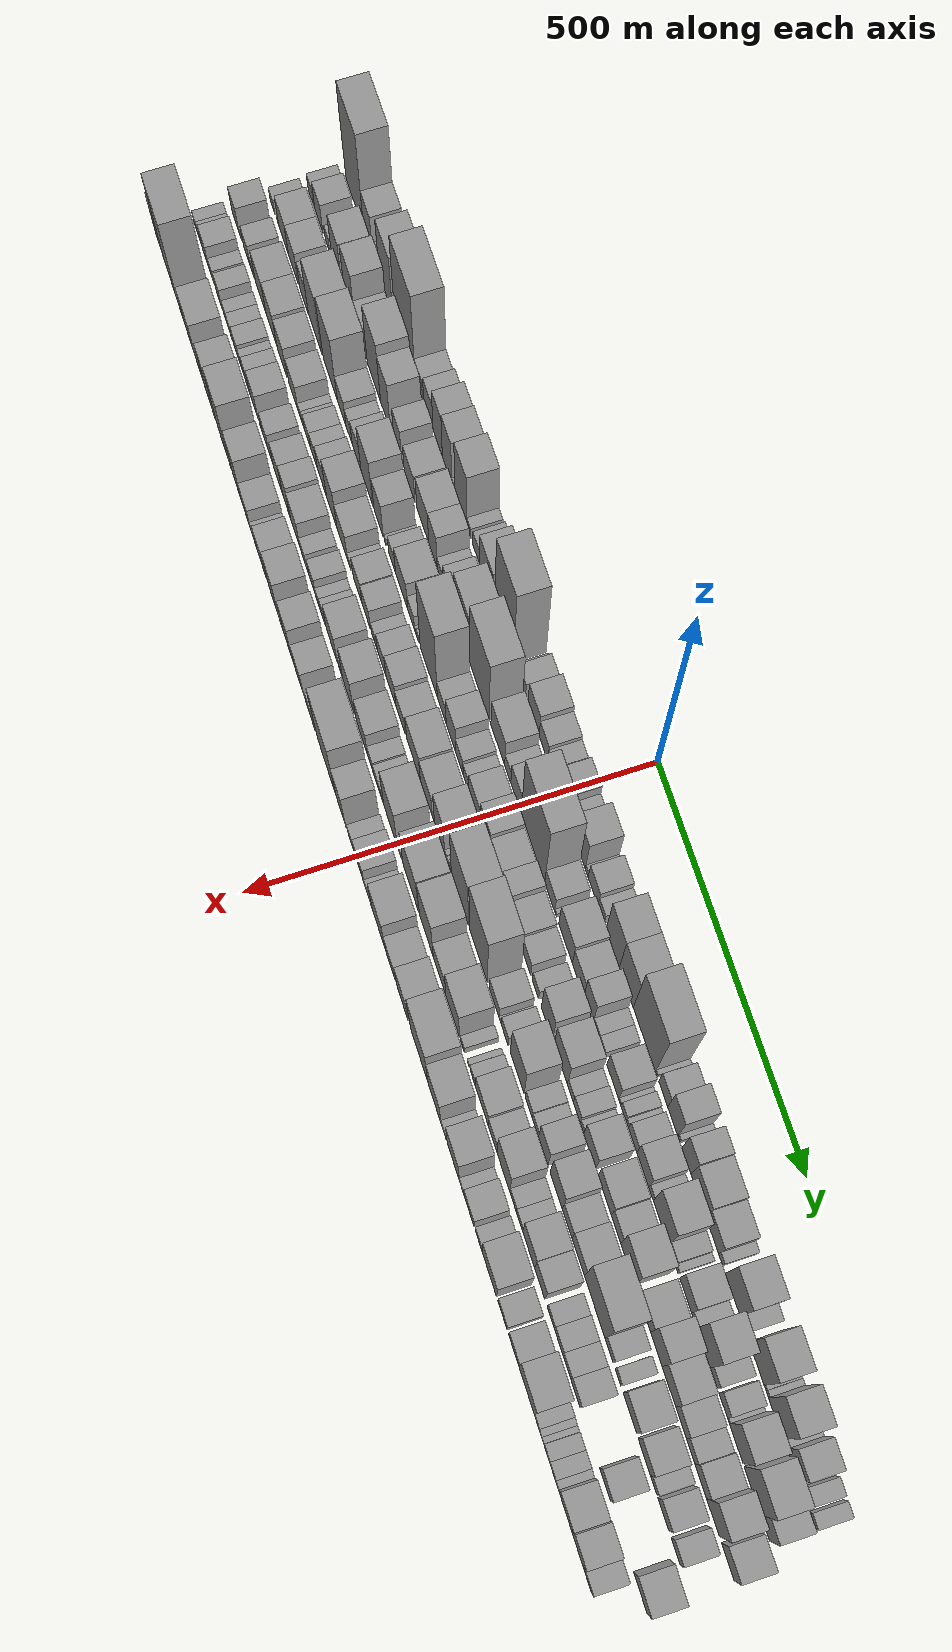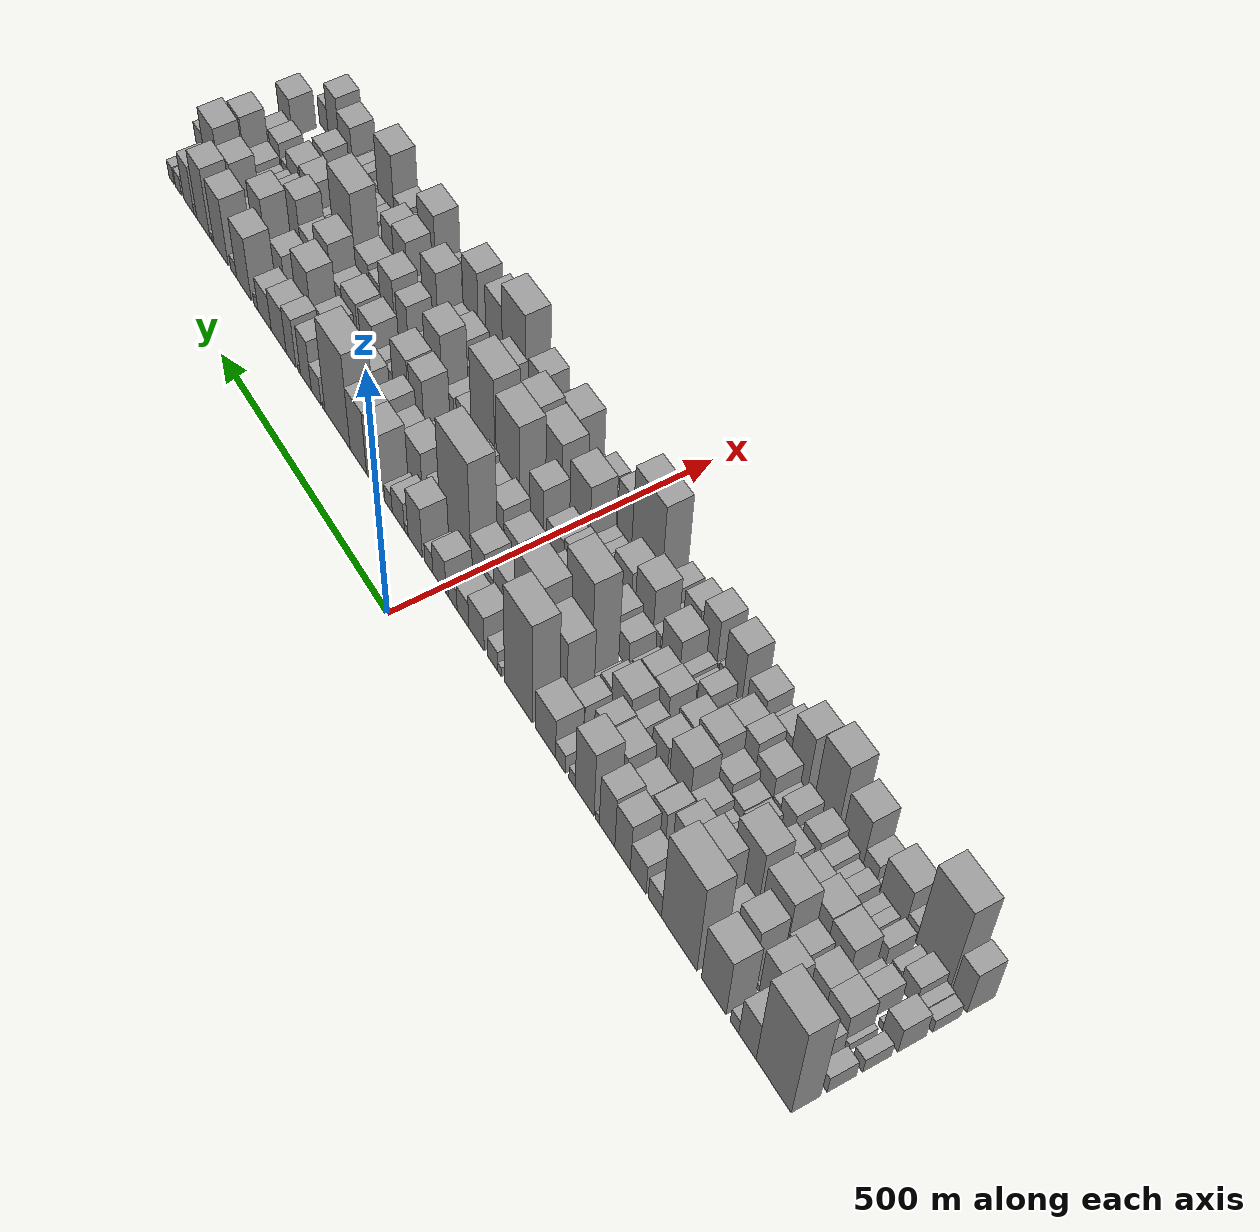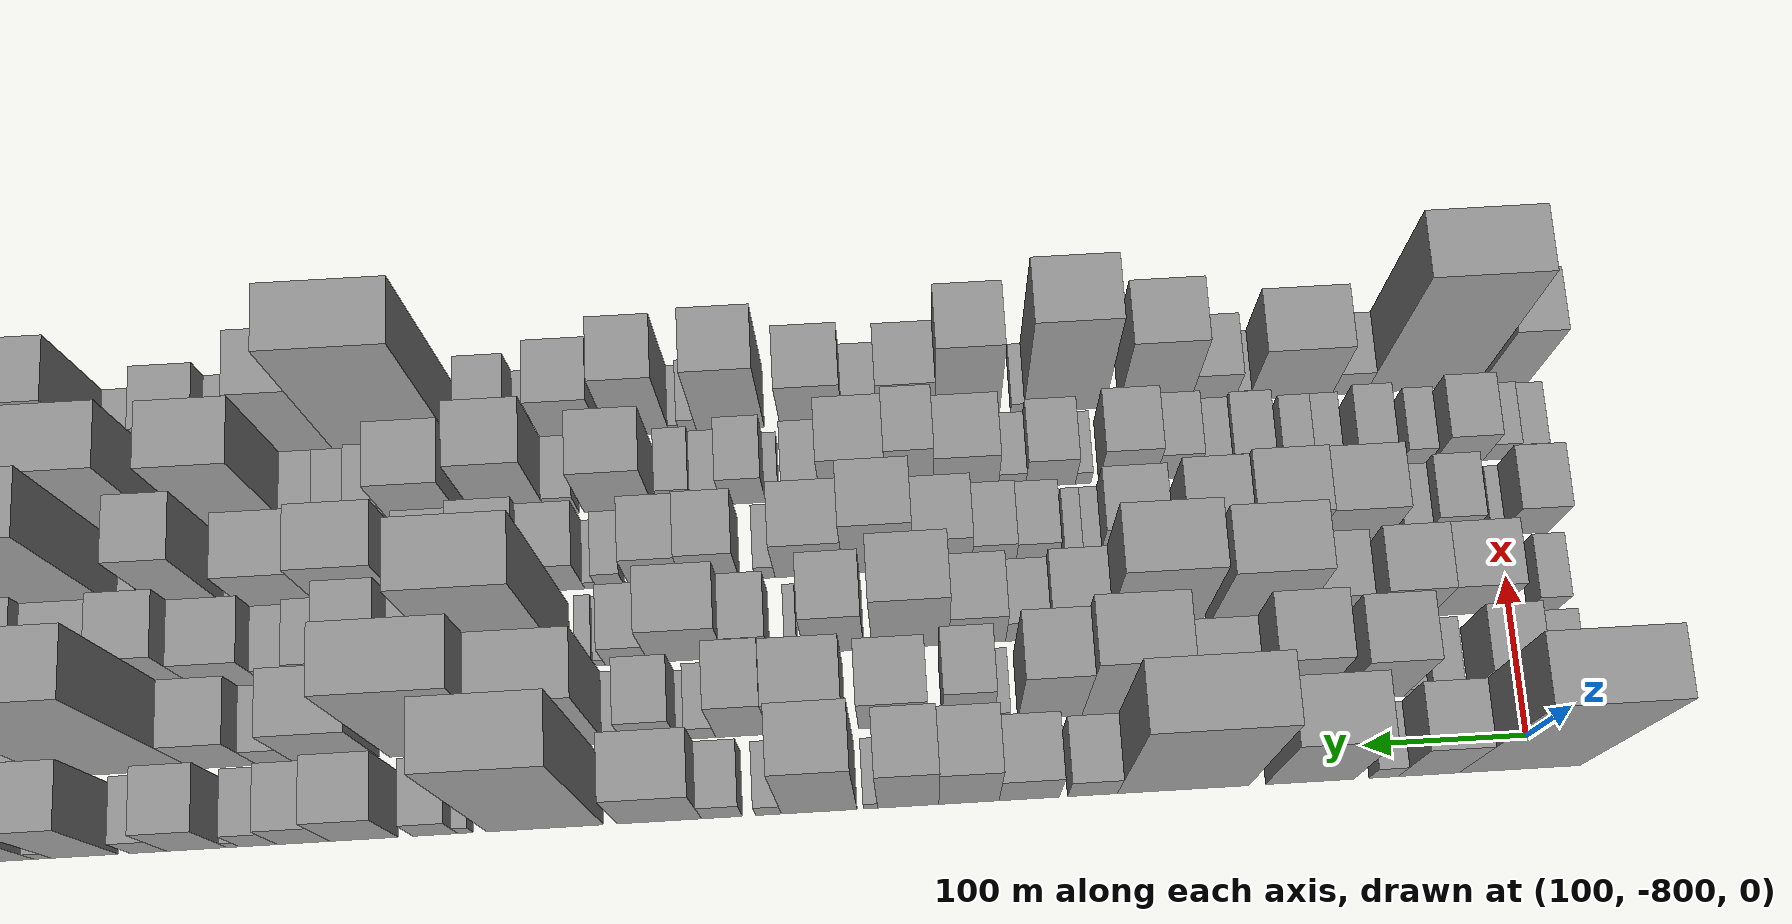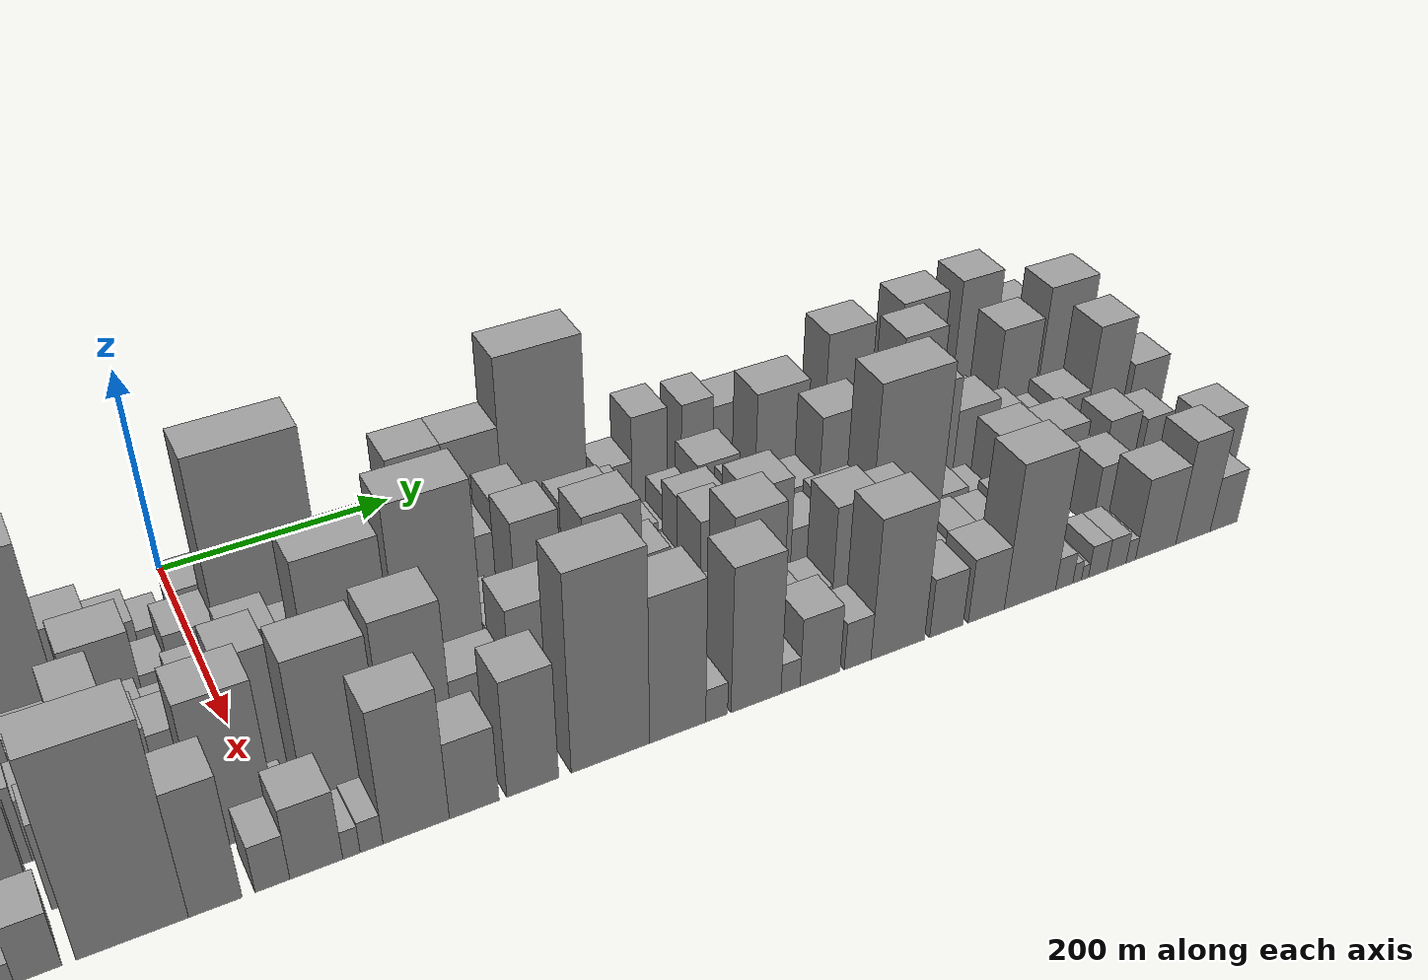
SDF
<sdf version="1.6">
 <world name="default">
  <scene>
   <sky><clouds><speed>12</speed></clouds></sky>
   <ambient>0.4 0.4 0.4 1</ambient>
   <background>0.7 0.7 0.7 1</background>
   <shadows>1</shadows>
  </scene>
  <gravity>0 0 -9.8066</gravity>
  <magnetic_field>6e-06 2.3e-05 -4.2e-05</magnetic_field>
  <physics default="0" name="default_physics" type="ode">
   <ode>
    <solver>
     <type>quick</type>
     <iters>10</iters>
     <sor>1.0</sor>
     <use_dynamic_moi_rescaling>0</use_dynamic_moi_rescaling>
    </solver>
    <constraints>
     <cfm>0</cfm>
     <erp>0.2</erp>
     <contact_max_correcting_vel>100</contact_max_correcting_vel>
     <contact_surface_layer>0.001</contact_surface_layer>
    </constraints>
   </ode>
   <max_step_size>0.004</max_step_size>
   <real_time_factor>1</real_time_factor>
   <real_time_update_rate>250</real_time_update_rate>
  </physics>
  <light name="sun" type="directional">
   <pose>0 0 10 0 0 0</pose>
   <diffuse>0.8 0.8 0.8 1</diffuse>
   <specular>0.2 0.2 0.2 1</specular>
   <attenuation>
    <range>1000</range>
    <constant>0.9</constant>
    <linear>0.01</linear>
    <quadratic>0.001</quadratic>
   </attenuation>
   <direction>-0.5 0.1 -0.9</direction>
  </light>
  <model name="building_1">
   <static>1</static>
   <pose>100.0000 -793.1212 0 0.000000 0.000000 0.000000</pose>
   <link name="link">
    <pose>0 0 108.00 0 0 0</pose>
    <collision name="collision"><geometry><box><size>40.0000 73.7576 216.0000</size></box></geometry></collision>
    <visual name="visual">
     <cast_shadows>0</cast_shadows>
     <geometry><box><size>40.0000 73.7576 216.0000</size></box></geometry>
     <material>
      <script>
       <uri>model://grey_wall/materials/scripts</uri>
       <uri>model://grey_wall/materials/textures</uri>
       <name>vrc/grey_wall</name>
      </script>
     </material>
    </visual>
   </link>
  </model>
  <model name="building_2">
   <static>1</static>
   <pose>100.0000 -737.7081 0 0.000000 0.000000 0.000000</pose>
   <link name="link">
    <pose>0 0 46.50 0 0 0</pose>
    <collision name="collision"><geometry><box><size>40.0000 37.0684 93.0000</size></box></geometry></collision>
    <visual name="visual">
     <cast_shadows>0</cast_shadows>
     <geometry><box><size>40.0000 37.0684 93.0000</size></box></geometry>
     <material>
      <script>
       <uri>model://grey_wall/materials/scripts</uri>
       <uri>model://grey_wall/materials/textures</uri>
       <name>vrc/grey_wall</name>
      </script>
     </material>
    </visual>
   </link>
  </model>
  <model name="building_3">
   <static>1</static>
   <pose>100.0000 -710.1865 0 0.000000 0.000000 0.000000</pose>
   <link name="link">
    <pose>0 0 16.50 0 0 0</pose>
    <collision name="collision"><geometry><box><size>40.0000 17.9748 33.0000</size></box></geometry></collision>
    <visual name="visual">
     <cast_shadows>0</cast_shadows>
     <geometry><box><size>40.0000 17.9748 33.0000</size></box></geometry>
     <material>
      <script>
       <uri>model://grey_wall/materials/scripts</uri>
       <uri>model://grey_wall/materials/textures</uri>
       <name>vrc/grey_wall</name>
      </script>
     </material>
    </visual>
   </link>
  </model>
  <model name="building_4">
   <static>1</static>
   <pose>100.0000 -665.2125 0 0.000000 0.000000 0.000000</pose>
   <link name="link">
    <pose>0 0 67.50 0 0 0</pose>
    <collision name="collision"><geometry><box><size>40.0000 53.9733 135.0000</size></box></geometry></collision>
    <visual name="visual">
     <cast_shadows>0</cast_shadows>
     <geometry><box><size>40.0000 53.9733 135.0000</size></box></geometry>
     <material>
      <script>
       <uri>model://grey_wall/materials/scripts</uri>
       <uri>model://grey_wall/materials/textures</uri>
       <name>vrc/grey_wall</name>
      </script>
     </material>
    </visual>
   </link>
  </model>
  <model name="building_5">
   <static>1</static>
   <pose>100.0000 -588.1963 0 0.000000 0.000000 0.000000</pose>
   <link name="link">
    <pose>0 0 103.50 0 0 0</pose>
    <collision name="collision"><geometry><box><size>40.0000 80.0591 207.0000</size></box></geometry></collision>
    <visual name="visual">
     <cast_shadows>0</cast_shadows>
     <geometry><box><size>40.0000 80.0591 207.0000</size></box></geometry>
     <material>
      <script>
       <uri>model://grey_wall/materials/scripts</uri>
       <uri>model://grey_wall/materials/textures</uri>
       <name>vrc/grey_wall</name>
      </script>
     </material>
    </visual>
   </link>
  </model>
  <model name="building_6">
   <static>1</static>
   <pose>100.0000 -533.0050 0 0.000000 0.000000 0.000000</pose>
   <link name="link">
    <pose>0 0 25.50 0 0 0</pose>
    <collision name="collision"><geometry><box><size>40.0000 30.3234 51.0000</size></box></geometry></collision>
    <visual name="visual">
     <cast_shadows>0</cast_shadows>
     <geometry><box><size>40.0000 30.3234 51.0000</size></box></geometry>
     <material>
      <script>
       <uri>model://grey_wall/materials/scripts</uri>
       <uri>model://grey_wall/materials/textures</uri>
       <name>vrc/grey_wall</name>
      </script>
     </material>
    </visual>
   </link>
  </model>
  <model name="building_7">
   <static>1</static>
   <pose>100.0000 -494.5652 0 0.000000 0.000000 0.000000</pose>
   <link name="link">
    <pose>0 0 34.50 0 0 0</pose>
    <collision name="collision"><geometry><box><size>40.0000 36.5564 69.0000</size></box></geometry></collision>
    <visual name="visual">
     <cast_shadows>0</cast_shadows>
     <geometry><box><size>40.0000 36.5564 69.0000</size></box></geometry>
     <material>
      <script>
       <uri>model://grey_wall/materials/scripts</uri>
       <uri>model://grey_wall/materials/textures</uri>
       <name>vrc/grey_wall</name>
      </script>
     </material>
    </visual>
   </link>
  </model>
  <model name="building_8">
   <static>1</static>
   <pose>100.0000 -458.0623 0 0.000000 0.000000 0.000000</pose>
   <link name="link">
    <pose>0 0 54.00 0 0 0</pose>
    <collision name="collision"><geometry><box><size>40.0000 36.4493 108.0000</size></box></geometry></collision>
    <visual name="visual">
     <cast_shadows>0</cast_shadows>
     <geometry><box><size>40.0000 36.4493 108.0000</size></box></geometry>
     <material>
      <script>
       <uri>model://grey_wall/materials/scripts</uri>
       <uri>model://grey_wall/materials/textures</uri>
       <name>vrc/grey_wall</name>
      </script>
     </material>
    </visual>
   </link>
  </model>
  <model name="building_9">
   <static>1</static>
   <pose>100.0000 -421.3438 0 0.000000 0.000000 0.000000</pose>
   <link name="link">
    <pose>0 0 58.50 0 0 0</pose>
    <collision name="collision"><geometry><box><size>40.0000 36.9877 117.0000</size></box></geometry></collision>
    <visual name="visual">
     <cast_shadows>0</cast_shadows>
     <geometry><box><size>40.0000 36.9877 117.0000</size></box></geometry>
     <material>
      <script>
       <uri>model://grey_wall/materials/scripts</uri>
       <uri>model://grey_wall/materials/textures</uri>
       <name>vrc/grey_wall</name>
      </script>
     </material>
    </visual>
   </link>
  </model>
  <model name="building_10">
   <static>1</static>
   <pose>100.0000 -398.6143 0 0.000000 0.000000 0.000000</pose>
   <link name="link">
    <pose>0 0 9.00 0 0 0</pose>
    <collision name="collision"><geometry><box><size>40.0000 8.4713 18.0000</size></box></geometry></collision>
    <visual name="visual">
     <cast_shadows>0</cast_shadows>
     <geometry><box><size>40.0000 8.4713 18.0000</size></box></geometry>
     <material>
      <script>
       <uri>model://grey_wall/materials/scripts</uri>
       <uri>model://grey_wall/materials/textures</uri>
       <name>vrc/grey_wall</name>
      </script>
     </material>
    </visual>
   </link>
  </model>
  <model name="building_11">
   <static>1</static>
   <pose>100.0000 -367.5345 0 0.000000 0.000000 0.000000</pose>
   <link name="link">
    <pose>0 0 73.50 0 0 0</pose>
    <collision name="collision"><geometry><box><size>40.0000 45.6884 147.0000</size></box></geometry></collision>
    <visual name="visual">
     <cast_shadows>0</cast_shadows>
     <geometry><box><size>40.0000 45.6884 147.0000</size></box></geometry>
     <material>
      <script>
       <uri>model://grey_wall/materials/scripts</uri>
       <uri>model://grey_wall/materials/textures</uri>
       <name>vrc/grey_wall</name>
      </script>
     </material>
    </visual>
   </link>
  </model>
  <model name="building_12">
   <static>1</static>
   <pose>100.0000 -336.9744 0 0.000000 0.000000 0.000000</pose>
   <link name="link">
    <pose>0 0 15.00 0 0 0</pose>
    <collision name="collision"><geometry><box><size>40.0000 15.4319 30.0000</size></box></geometry></collision>
    <visual name="visual">
     <cast_shadows>0</cast_shadows>
     <geometry><box><size>40.0000 15.4319 30.0000</size></box></geometry>
     <material>
      <script>
       <uri>model://grey_wall/materials/scripts</uri>
       <uri>model://grey_wall/materials/textures</uri>
       <name>vrc/grey_wall</name>
      </script>
     </material>
    </visual>
   </link>
  </model>
  <model name="building_13">
   <static>1</static>
   <pose>100.0000 -308.8902 0 0.000000 0.000000 0.000000</pose>
   <link name="link">
    <pose>0 0 21.00 0 0 0</pose>
    <collision name="collision"><geometry><box><size>40.0000 24.7364 42.0000</size></box></geometry></collision>
    <visual name="visual">
     <cast_shadows>0</cast_shadows>
     <geometry><box><size>40.0000 24.7364 42.0000</size></box></geometry>
     <material>
      <script>
       <uri>model://grey_wall/materials/scripts</uri>
       <uri>model://grey_wall/materials/textures</uri>
       <name>vrc/grey_wall</name>
      </script>
     </material>
    </visual>
   </link>
  </model>
  <model name="building_14">
   <static>1</static>
   <pose>100.0000 -271.0160 0 0.000000 0.000000 0.000000</pose>
   <link name="link">
    <pose>0 0 45.00 0 0 0</pose>
    <collision name="collision"><geometry><box><size>40.0000 51.0120 90.0000</size></box></geometry></collision>
    <visual name="visual">
     <cast_shadows>0</cast_shadows>
     <geometry><box><size>40.0000 51.0120 90.0000</size></box></geometry>
     <material>
      <script>
       <uri>model://grey_wall/materials/scripts</uri>
       <uri>model://grey_wall/materials/textures</uri>
       <name>vrc/grey_wall</name>
      </script>
     </material>
    </visual>
   </link>
  </model>
  <model name="building_15">
   <static>1</static>
   <pose>100.0000 -202.2346 0 0.000000 0.000000 0.000000</pose>
   <link name="link">
    <pose>0 0 111.00 0 0 0</pose>
    <collision name="collision"><geometry><box><size>40.0000 70.5507 222.0000</size></box></geometry></collision>
    <visual name="visual">
     <cast_shadows>0</cast_shadows>
     <geometry><box><size>40.0000 70.5507 222.0000</size></box></geometry>
     <material>
      <script>
       <uri>model://grey_wall/materials/scripts</uri>
       <uri>model://grey_wall/materials/textures</uri>
       <name>vrc/grey_wall</name>
      </script>
     </material>
    </visual>
   </link>
  </model>
  <model name="building_16">
   <static>1</static>
   <pose>100.0000 -154.2980 0 0.000000 0.000000 0.000000</pose>
   <link name="link">
    <pose>0 0 10.50 0 0 0</pose>
    <collision name="collision"><geometry><box><size>40.0000 9.3223 21.0000</size></box></geometry></collision>
    <visual name="visual">
     <cast_shadows>0</cast_shadows>
     <geometry><box><size>40.0000 9.3223 21.0000</size></box></geometry>
     <material>
      <script>
       <uri>model://grey_wall/materials/scripts</uri>
       <uri>model://grey_wall/materials/textures</uri>
       <name>vrc/grey_wall</name>
      </script>
     </material>
    </visual>
   </link>
  </model>
  <model name="building_17">
   <static>1</static>
   <pose>100.0000 -136.1564 0 0.000000 0.000000 0.000000</pose>
   <link name="link">
    <pose>0 0 22.50 0 0 0</pose>
    <collision name="collision"><geometry><box><size>40.0000 26.9609 45.0000</size></box></geometry></collision>
    <visual name="visual">
     <cast_shadows>0</cast_shadows>
     <geometry><box><size>40.0000 26.9609 45.0000</size></box></geometry>
     <material>
      <script>
       <uri>model://grey_wall/materials/scripts</uri>
       <uri>model://grey_wall/materials/textures</uri>
       <name>vrc/grey_wall</name>
      </script>
     </material>
    </visual>
   </link>
  </model>
  <model name="building_18">
   <static>1</static>
   <pose>100.0000 -93.2137 0 0.000000 0.000000 0.000000</pose>
   <link name="link">
    <pose>0 0 37.50 0 0 0</pose>
    <collision name="collision"><geometry><box><size>40.0000 40.9246 75.0000</size></box></geometry></collision>
    <visual name="visual">
     <cast_shadows>0</cast_shadows>
     <geometry><box><size>40.0000 40.9246 75.0000</size></box></geometry>
     <material>
      <script>
       <uri>model://grey_wall/materials/scripts</uri>
       <uri>model://grey_wall/materials/textures</uri>
       <name>vrc/grey_wall</name>
      </script>
     </material>
    </visual>
   </link>
  </model>
  <model name="building_19">
   <static>1</static>
   <pose>100.0000 -57.0168 0 0.000000 0.000000 0.000000</pose>
   <link name="link">
    <pose>0 0 28.50 0 0 0</pose>
    <collision name="collision"><geometry><box><size>40.0000 31.4691 57.0000</size></box></geometry></collision>
    <visual name="visual">
     <cast_shadows>0</cast_shadows>
     <geometry><box><size>40.0000 31.4691 57.0000</size></box></geometry>
     <material>
      <script>
       <uri>model://grey_wall/materials/scripts</uri>
       <uri>model://grey_wall/materials/textures</uri>
       <name>vrc/grey_wall</name>
      </script>
     </material>
    </visual>
   </link>
  </model>
  <model name="building_20">
   <static>1</static>
   <pose>100.0000 -29.9693 0 0.000000 0.000000 0.000000</pose>
   <link name="link">
    <pose>0 0 22.50 0 0 0</pose>
    <collision name="collision"><geometry><box><size>40.0000 22.6258 45.0000</size></box></geometry></collision>
    <visual name="visual">
     <cast_shadows>0</cast_shadows>
     <geometry><box><size>40.0000 22.6258 45.0000</size></box></geometry>
     <material>
      <script>
       <uri>model://grey_wall/materials/scripts</uri>
       <uri>model://grey_wall/materials/textures</uri>
       <name>vrc/grey_wall</name>
      </script>
     </material>
    </visual>
   </link>
  </model>
  <model name="building_21">
   <static>1</static>
   <pose>100.0000 -14.8287 0 0.000000 0.000000 0.000000</pose>
   <link name="link">
    <pose>0 0 9.00 0 0 0</pose>
    <collision name="collision"><geometry><box><size>40.0000 7.6554 18.0000</size></box></geometry></collision>
    <visual name="visual">
     <cast_shadows>0</cast_shadows>
     <geometry><box><size>40.0000 7.6554 18.0000</size></box></geometry>
     <material>
      <script>
       <uri>model://grey_wall/materials/scripts</uri>
       <uri>model://grey_wall/materials/textures</uri>
       <name>vrc/grey_wall</name>
      </script>
     </material>
    </visual>
   </link>
  </model>
  <model name="building_22">
   <static>1</static>
   <pose>100.0000 7.0305 0 0.000000 0.000000 0.000000</pose>
   <link name="link">
    <pose>0 0 36.00 0 0 0</pose>
    <collision name="collision"><geometry><box><size>40.0000 36.0629 72.0000</size></box></geometry></collision>
    <visual name="visual">
     <cast_shadows>0</cast_shadows>
     <geometry><box><size>40.0000 36.0629 72.0000</size></box></geometry>
     <material>
      <script>
       <uri>model://grey_wall/materials/scripts</uri>
       <uri>model://grey_wall/materials/textures</uri>
       <name>vrc/grey_wall</name>
      </script>
     </material>
    </visual>
   </link>
  </model>
  <model name="building_23">
   <static>1</static>
   <pose>100.0000 36.0467 0 0.000000 0.000000 0.000000</pose>
   <link name="link">
    <pose>0 0 21.00 0 0 0</pose>
    <collision name="collision"><geometry><box><size>40.0000 21.9696 42.0000</size></box></geometry></collision>
    <visual name="visual">
     <cast_shadows>0</cast_shadows>
     <geometry><box><size>40.0000 21.9696 42.0000</size></box></geometry>
     <material>
      <script>
       <uri>model://grey_wall/materials/scripts</uri>
       <uri>model://grey_wall/materials/textures</uri>
       <name>vrc/grey_wall</name>
      </script>
     </material>
    </visual>
   </link>
  </model>
  <model name="building_24">
   <static>1</static>
   <pose>100.0000 74.0486 0 0.000000 0.000000 0.000000</pose>
   <link name="link">
    <pose>0 0 54.00 0 0 0</pose>
    <collision name="collision"><geometry><box><size>40.0000 40.0341 108.0000</size></box></geometry></collision>
    <visual name="visual">
     <cast_shadows>0</cast_shadows>
     <geometry><box><size>40.0000 40.0341 108.0000</size></box></geometry>
     <material>
      <script>
       <uri>model://grey_wall/materials/scripts</uri>
       <uri>model://grey_wall/materials/textures</uri>
       <name>vrc/grey_wall</name>
      </script>
     </material>
    </visual>
   </link>
  </model>
  <model name="building_25">
   <static>1</static>
   <pose>100.0000 99.2579 0 0.000000 0.000000 0.000000</pose>
   <link name="link">
    <pose>0 0 10.50 0 0 0</pose>
    <collision name="collision"><geometry><box><size>40.0000 10.3845 21.0000</size></box></geometry></collision>
    <visual name="visual">
     <cast_shadows>0</cast_shadows>
     <geometry><box><size>40.0000 10.3845 21.0000</size></box></geometry>
     <material>
      <script>
       <uri>model://grey_wall/materials/scripts</uri>
       <uri>model://grey_wall/materials/textures</uri>
       <name>vrc/grey_wall</name>
      </script>
     </material>
    </visual>
   </link>
  </model>
  <model name="building_26">
   <static>1</static>
   <pose>100.0000 121.7577 0 0.000000 0.000000 0.000000</pose>
   <link name="link">
    <pose>0 0 30.00 0 0 0</pose>
    <collision name="collision"><geometry><box><size>40.0000 34.6151 60.0000</size></box></geometry></collision>
    <visual name="visual">
     <cast_shadows>0</cast_shadows>
     <geometry><box><size>40.0000 34.6151 60.0000</size></box></geometry>
     <material>
      <script>
       <uri>model://grey_wall/materials/scripts</uri>
       <uri>model://grey_wall/materials/textures</uri>
       <name>vrc/grey_wall</name>
      </script>
     </material>
    </visual>
   </link>
  </model>
  <model name="building_27">
   <static>1</static>
   <pose>100.0000 149.8607 0 0.000000 0.000000 0.000000</pose>
   <link name="link">
    <pose>0 0 19.50 0 0 0</pose>
    <collision name="collision"><geometry><box><size>40.0000 21.5908 39.0000</size></box></geometry></collision>
    <visual name="visual">
     <cast_shadows>0</cast_shadows>
     <geometry><box><size>40.0000 21.5908 39.0000</size></box></geometry>
     <material>
      <script>
       <uri>model://grey_wall/materials/scripts</uri>
       <uri>model://grey_wall/materials/textures</uri>
       <name>vrc/grey_wall</name>
      </script>
     </material>
    </visual>
   </link>
  </model>
  <model name="building_28">
   <static>1</static>
   <pose>100.0000 190.6589 0 0.000000 0.000000 0.000000</pose>
   <link name="link">
    <pose>0 0 67.50 0 0 0</pose>
    <collision name="collision"><geometry><box><size>40.0000 46.0056 135.0000</size></box></geometry></collision>
    <visual name="visual">
     <cast_shadows>0</cast_shadows>
     <geometry><box><size>40.0000 46.0056 135.0000</size></box></geometry>
     <material>
      <script>
       <uri>model://grey_wall/materials/scripts</uri>
       <uri>model://grey_wall/materials/textures</uri>
       <name>vrc/grey_wall</name>
      </script>
     </material>
    </visual>
   </link>
  </model>
  <model name="building_29">
   <static>1</static>
   <pose>100.0000 237.8732 0 0.000000 0.000000 0.000000</pose>
   <link name="link">
    <pose>0 0 67.50 0 0 0</pose>
    <collision name="collision"><geometry><box><size>40.0000 48.4229 135.0000</size></box></geometry></collision>
    <visual name="visual">
     <cast_shadows>0</cast_shadows>
     <geometry><box><size>40.0000 48.4229 135.0000</size></box></geometry>
     <material>
      <script>
       <uri>model://grey_wall/materials/scripts</uri>
       <uri>model://grey_wall/materials/textures</uri>
       <name>vrc/grey_wall</name>
      </script>
     </material>
    </visual>
   </link>
  </model>
  <model name="building_30">
   <static>1</static>
   <pose>100.0000 300.0080 0 0.000000 0.000000 0.000000</pose>
   <link name="link">
    <pose>0 0 100.50 0 0 0</pose>
    <collision name="collision"><geometry><box><size>40.0000 75.8467 201.0000</size></box></geometry></collision>
    <visual name="visual">
     <cast_shadows>0</cast_shadows>
     <geometry><box><size>40.0000 75.8467 201.0000</size></box></geometry>
     <material>
      <script>
       <uri>model://grey_wall/materials/scripts</uri>
       <uri>model://grey_wall/materials/textures</uri>
       <name>vrc/grey_wall</name>
      </script>
     </material>
    </visual>
   </link>
  </model>
  <model name="building_31">
   <static>1</static>
   <pose>100.0000 341.1318 0 0.000000 0.000000 0.000000</pose>
   <link name="link">
    <pose>0 0 7.50 0 0 0</pose>
    <collision name="collision"><geometry><box><size>40.0000 6.4011 15.0000</size></box></geometry></collision>
    <visual name="visual">
     <cast_shadows>0</cast_shadows>
     <geometry><box><size>40.0000 6.4011 15.0000</size></box></geometry>
     <material>
      <script>
       <uri>model://grey_wall/materials/scripts</uri>
       <uri>model://grey_wall/materials/textures</uri>
       <name>vrc/grey_wall</name>
      </script>
     </material>
    </visual>
   </link>
  </model>
  <model name="building_32">
   <static>1</static>
   <pose>100.0000 364.4983 0 0.000000 0.000000 0.000000</pose>
   <link name="link">
    <pose>0 0 30.00 0 0 0</pose>
    <collision name="collision"><geometry><box><size>40.0000 30.3318 60.0000</size></box></geometry></collision>
    <visual name="visual">
     <cast_shadows>0</cast_shadows>
     <geometry><box><size>40.0000 30.3318 60.0000</size></box></geometry>
     <material>
      <script>
       <uri>model://grey_wall/materials/scripts</uri>
       <uri>model://grey_wall/materials/textures</uri>
       <name>vrc/grey_wall</name>
      </script>
     </material>
    </visual>
   </link>
  </model>
  <model name="building_33">
   <static>1</static>
   <pose>100.0000 396.5555 0 0.000000 0.000000 0.000000</pose>
   <link name="link">
    <pose>0 0 52.50 0 0 0</pose>
    <collision name="collision"><geometry><box><size>40.0000 33.7827 105.0000</size></box></geometry></collision>
    <visual name="visual">
     <cast_shadows>0</cast_shadows>
     <geometry><box><size>40.0000 33.7827 105.0000</size></box></geometry>
     <material>
      <script>
       <uri>model://grey_wall/materials/scripts</uri>
       <uri>model://grey_wall/materials/textures</uri>
       <name>vrc/grey_wall</name>
      </script>
     </material>
    </visual>
   </link>
  </model>
  <model name="building_34">
   <static>1</static>
   <pose>100.0000 417.2055 0 0.000000 0.000000 0.000000</pose>
   <link name="link">
    <pose>0 0 9.00 0 0 0</pose>
    <collision name="collision"><geometry><box><size>40.0000 7.5172 18.0000</size></box></geometry></collision>
    <visual name="visual">
     <cast_shadows>0</cast_shadows>
     <geometry><box><size>40.0000 7.5172 18.0000</size></box></geometry>
     <material>
      <script>
       <uri>model://grey_wall/materials/scripts</uri>
       <uri>model://grey_wall/materials/textures</uri>
       <name>vrc/grey_wall</name>
      </script>
     </material>
    </visual>
   </link>
  </model>
  <model name="building_35">
   <static>1</static>
   <pose>100.0000 442.3618 0 0.000000 0.000000 0.000000</pose>
   <link name="link">
    <pose>0 0 51.00 0 0 0</pose>
    <collision name="collision"><geometry><box><size>40.0000 30.7955 102.0000</size></box></geometry></collision>
    <visual name="visual">
     <cast_shadows>0</cast_shadows>
     <geometry><box><size>40.0000 30.7955 102.0000</size></box></geometry>
     <material>
      <script>
       <uri>model://grey_wall/materials/scripts</uri>
       <uri>model://grey_wall/materials/textures</uri>
       <name>vrc/grey_wall</name>
      </script>
     </material>
    </visual>
   </link>
  </model>
  <model name="building_36">
   <static>1</static>
   <pose>100.0000 481.5599 0 0.000000 0.000000 0.000000</pose>
   <link name="link">
    <pose>0 0 45.00 0 0 0</pose>
    <collision name="collision"><geometry><box><size>40.0000 47.6008 90.0000</size></box></geometry></collision>
    <visual name="visual">
     <cast_shadows>0</cast_shadows>
     <geometry><box><size>40.0000 47.6008 90.0000</size></box></geometry>
     <material>
      <script>
       <uri>model://grey_wall/materials/scripts</uri>
       <uri>model://grey_wall/materials/textures</uri>
       <name>vrc/grey_wall</name>
      </script>
     </material>
    </visual>
   </link>
  </model>
  <model name="building_37">
   <static>1</static>
   <pose>100.0000 526.7588 0 0.000000 0.000000 0.000000</pose>
   <link name="link">
    <pose>0 0 36.00 0 0 0</pose>
    <collision name="collision"><geometry><box><size>40.0000 42.7969 72.0000</size></box></geometry></collision>
    <visual name="visual">
     <cast_shadows>0</cast_shadows>
     <geometry><box><size>40.0000 42.7969 72.0000</size></box></geometry>
     <material>
      <script>
       <uri>model://grey_wall/materials/scripts</uri>
       <uri>model://grey_wall/materials/textures</uri>
       <name>vrc/grey_wall</name>
      </script>
     </material>
    </visual>
   </link>
  </model>
  <model name="building_38">
   <static>1</static>
   <pose>100.0000 554.7449 0 0.000000 0.000000 0.000000</pose>
   <link name="link">
    <pose>0 0 13.50 0 0 0</pose>
    <collision name="collision"><geometry><box><size>40.0000 13.1755 27.0000</size></box></geometry></collision>
    <visual name="visual">
     <cast_shadows>0</cast_shadows>
     <geometry><box><size>40.0000 13.1755 27.0000</size></box></geometry>
     <material>
      <script>
       <uri>model://grey_wall/materials/scripts</uri>
       <uri>model://grey_wall/materials/textures</uri>
       <name>vrc/grey_wall</name>
      </script>
     </material>
    </visual>
   </link>
  </model>
  <model name="building_39">
   <static>1</static>
   <pose>100.0000 594.0630 0 0.000000 0.000000 0.000000</pose>
   <link name="link">
    <pose>0 0 64.50 0 0 0</pose>
    <collision name="collision"><geometry><box><size>40.0000 47.4605 129.0000</size></box></geometry></collision>
    <visual name="visual">
     <cast_shadows>0</cast_shadows>
     <geometry><box><size>40.0000 47.4605 129.0000</size></box></geometry>
     <material>
      <script>
       <uri>model://grey_wall/materials/scripts</uri>
       <uri>model://grey_wall/materials/textures</uri>
       <name>vrc/grey_wall</name>
      </script>
     </material>
    </visual>
   </link>
  </model>
  <model name="building_40">
   <static>1</static>
   <pose>100.0000 627.4713 0 0.000000 0.000000 0.000000</pose>
   <link name="link">
    <pose>0 0 16.50 0 0 0</pose>
    <collision name="collision"><geometry><box><size>40.0000 19.3562 33.0000</size></box></geometry></collision>
    <visual name="visual">
     <cast_shadows>0</cast_shadows>
     <geometry><box><size>40.0000 19.3562 33.0000</size></box></geometry>
     <material>
      <script>
       <uri>model://grey_wall/materials/scripts</uri>
       <uri>model://grey_wall/materials/textures</uri>
       <name>vrc/grey_wall</name>
      </script>
     </material>
    </visual>
   </link>
  </model>
  <model name="building_41">
   <static>1</static>
   <pose>100.0000 669.9768 0 0.000000 0.000000 0.000000</pose>
   <link name="link">
    <pose>0 0 69.00 0 0 0</pose>
    <collision name="collision"><geometry><box><size>40.0000 47.6547 138.0000</size></box></geometry></collision>
    <visual name="visual">
     <cast_shadows>0</cast_shadows>
     <geometry><box><size>40.0000 47.6547 138.0000</size></box></geometry>
     <material>
      <script>
       <uri>model://grey_wall/materials/scripts</uri>
       <uri>model://grey_wall/materials/textures</uri>
       <name>vrc/grey_wall</name>
      </script>
     </material>
    </visual>
   </link>
  </model>
  <model name="building_42">
   <static>1</static>
   <pose>100.0000 696.9047 0 0.000000 0.000000 0.000000</pose>
   <link name="link">
    <pose>0 0 7.50 0 0 0</pose>
    <collision name="collision"><geometry><box><size>40.0000 6.2011 15.0000</size></box></geometry></collision>
    <visual name="visual">
     <cast_shadows>0</cast_shadows>
     <geometry><box><size>40.0000 6.2011 15.0000</size></box></geometry>
     <material>
      <script>
       <uri>model://grey_wall/materials/scripts</uri>
       <uri>model://grey_wall/materials/textures</uri>
       <name>vrc/grey_wall</name>
      </script>
     </material>
    </visual>
   </link>
  </model>
  <model name="building_43">
   <static>1</static>
   <pose>100.0000 703.7398 0 0.000000 0.000000 0.000000</pose>
   <link name="link">
    <pose>0 0 9.00 0 0 0</pose>
    <collision name="collision"><geometry><box><size>40.0000 7.4693 18.0000</size></box></geometry></collision>
    <visual name="visual">
     <cast_shadows>0</cast_shadows>
     <geometry><box><size>40.0000 7.4693 18.0000</size></box></geometry>
     <material>
      <script>
       <uri>model://grey_wall/materials/scripts</uri>
       <uri>model://grey_wall/materials/textures</uri>
       <name>vrc/grey_wall</name>
      </script>
     </material>
    </visual>
   </link>
  </model>
  <model name="building_44">
   <static>1</static>
   <pose>100.0000 729.4674 0 0.000000 0.000000 0.000000</pose>
   <link name="link">
    <pose>0 0 72.00 0 0 0</pose>
    <collision name="collision"><geometry><box><size>40.0000 43.9859 144.0000</size></box></geometry></collision>
    <visual name="visual">
     <cast_shadows>0</cast_shadows>
     <geometry><box><size>40.0000 43.9859 144.0000</size></box></geometry>
     <material>
      <script>
       <uri>model://grey_wall/materials/scripts</uri>
       <uri>model://grey_wall/materials/textures</uri>
       <name>vrc/grey_wall</name>
      </script>
     </material>
    </visual>
   </link>
  </model>
  <model name="building_45">
   <static>1</static>
   <pose>100.0000 757.0156 0 0.000000 0.000000 0.000000</pose>
   <link name="link">
    <pose>0 0 13.50 0 0 0</pose>
    <collision name="collision"><geometry><box><size>40.0000 11.1105 27.0000</size></box></geometry></collision>
    <visual name="visual">
     <cast_shadows>0</cast_shadows>
     <geometry><box><size>40.0000 11.1105 27.0000</size></box></geometry>
     <material>
      <script>
       <uri>model://grey_wall/materials/scripts</uri>
       <uri>model://grey_wall/materials/textures</uri>
       <name>vrc/grey_wall</name>
      </script>
     </material>
    </visual>
   </link>
  </model>
  <model name="building_46">
   <static>1</static>
   <pose>100.0000 780.0352 0 0.000000 0.000000 0.000000</pose>
   <link name="link">
    <pose>0 0 49.50 0 0 0</pose>
    <collision name="collision"><geometry><box><size>40.0000 34.9288 99.0000</size></box></geometry></collision>
    <visual name="visual">
     <cast_shadows>0</cast_shadows>
     <geometry><box><size>40.0000 34.9288 99.0000</size></box></geometry>
     <material>
      <script>
       <uri>model://grey_wall/materials/scripts</uri>
       <uri>model://grey_wall/materials/textures</uri>
       <name>vrc/grey_wall</name>
      </script>
     </material>
    </visual>
   </link>
  </model>
  <model name="building_47">
   <static>1</static>
   <pose>100.0000 815.9037 0 0.000000 0.000000 0.000000</pose>
   <link name="link">
    <pose>0 0 19.50 0 0 0</pose>
    <collision name="collision"><geometry><box><size>40.0000 20.8082 39.0000</size></box></geometry></collision>
    <visual name="visual">
     <cast_shadows>0</cast_shadows>
     <geometry><box><size>40.0000 20.8082 39.0000</size></box></geometry>
     <material>
      <script>
       <uri>model://grey_wall/materials/scripts</uri>
       <uri>model://grey_wall/materials/textures</uri>
       <name>vrc/grey_wall</name>
      </script>
     </material>
    </visual>
   </link>
  </model>
  <model name="building_48">
   <static>1</static>
   <pose>100.0000 840.4531 0 0.000000 0.000000 0.000000</pose>
   <link name="link">
    <pose>0 0 18.00 0 0 0</pose>
    <collision name="collision"><geometry><box><size>40.0000 18.2907 36.0000</size></box></geometry></collision>
    <visual name="visual">
     <cast_shadows>0</cast_shadows>
     <geometry><box><size>40.0000 18.2907 36.0000</size></box></geometry>
     <material>
      <script>
       <uri>model://grey_wall/materials/scripts</uri>
       <uri>model://grey_wall/materials/textures</uri>
       <name>vrc/grey_wall</name>
      </script>
     </material>
    </visual>
   </link>
  </model>
  <model name="building_49">
   <static>1</static>
   <pose>149.0000 -818.3011 0 0.000000 0.000000 0.000000</pose>
   <link name="link">
    <pose>0 0 19.50 0 0 0</pose>
    <collision name="collision"><geometry><box><size>40.0000 23.3978 39.0000</size></box></geometry></collision>
    <visual name="visual">
     <cast_shadows>0</cast_shadows>
     <geometry><box><size>40.0000 23.3978 39.0000</size></box></geometry>
     <material>
      <script>
       <uri>model://grey_wall/materials/scripts</uri>
       <uri>model://grey_wall/materials/textures</uri>
       <name>vrc/grey_wall</name>
      </script>
     </material>
    </visual>
   </link>
  </model>
  <model name="building_50">
   <static>1</static>
   <pose>149.0000 -784.6817 0 0.000000 0.000000 0.000000</pose>
   <link name="link">
    <pose>0 0 33.00 0 0 0</pose>
    <collision name="collision"><geometry><box><size>40.0000 33.8410 66.0000</size></box></geometry></collision>
    <visual name="visual">
     <cast_shadows>0</cast_shadows>
     <geometry><box><size>40.0000 33.8410 66.0000</size></box></geometry>
     <material>
      <script>
       <uri>model://grey_wall/materials/scripts</uri>
       <uri>model://grey_wall/materials/textures</uri>
       <name>vrc/grey_wall</name>
      </script>
     </material>
    </visual>
   </link>
  </model>
  <model name="building_51">
   <static>1</static>
   <pose>149.0000 -748.1782 0 0.000000 0.000000 0.000000</pose>
   <link name="link">
    <pose>0 0 18.00 0 0 0</pose>
    <collision name="collision"><geometry><box><size>40.0000 19.1659 36.0000</size></box></geometry></collision>
    <visual name="visual">
     <cast_shadows>0</cast_shadows>
     <geometry><box><size>40.0000 19.1659 36.0000</size></box></geometry>
     <material>
      <script>
       <uri>model://grey_wall/materials/scripts</uri>
       <uri>model://grey_wall/materials/textures</uri>
       <name>vrc/grey_wall</name>
      </script>
     </material>
    </visual>
   </link>
  </model>
  <model name="building_52">
   <static>1</static>
   <pose>149.0000 -733.3904 0 0.000000 0.000000 0.000000</pose>
   <link name="link">
    <pose>0 0 10.50 0 0 0</pose>
    <collision name="collision"><geometry><box><size>40.0000 10.4098 21.0000</size></box></geometry></collision>
    <visual name="visual">
     <cast_shadows>0</cast_shadows>
     <geometry><box><size>40.0000 10.4098 21.0000</size></box></geometry>
     <material>
      <script>
       <uri>model://grey_wall/materials/scripts</uri>
       <uri>model://grey_wall/materials/textures</uri>
       <name>vrc/grey_wall</name>
      </script>
     </material>
    </visual>
   </link>
  </model>
  <model name="building_53">
   <static>1</static>
   <pose>149.0000 -707.5355 0 0.000000 0.000000 0.000000</pose>
   <link name="link">
    <pose>0 0 55.50 0 0 0</pose>
    <collision name="collision"><geometry><box><size>40.0000 41.3000 111.0000</size></box></geometry></collision>
    <visual name="visual">
     <cast_shadows>0</cast_shadows>
     <geometry><box><size>40.0000 41.3000 111.0000</size></box></geometry>
     <material>
      <script>
       <uri>model://grey_wall/materials/scripts</uri>
       <uri>model://grey_wall/materials/textures</uri>
       <name>vrc/grey_wall</name>
      </script>
     </material>
    </visual>
   </link>
  </model>
  <model name="building_54">
   <static>1</static>
   <pose>149.0000 -683.5257 0 0.000000 0.000000 0.000000</pose>
   <link name="link">
    <pose>0 0 7.50 0 0 0</pose>
    <collision name="collision"><geometry><box><size>40.0000 6.7196 15.0000</size></box></geometry></collision>
    <visual name="visual">
     <cast_shadows>0</cast_shadows>
     <geometry><box><size>40.0000 6.7196 15.0000</size></box></geometry>
     <material>
      <script>
       <uri>model://grey_wall/materials/scripts</uri>
       <uri>model://grey_wall/materials/textures</uri>
       <name>vrc/grey_wall</name>
      </script>
     </material>
    </visual>
   </link>
  </model>
  <model name="building_55">
   <static>1</static>
   <pose>149.0000 -653.6527 0 0.000000 0.000000 0.000000</pose>
   <link name="link">
    <pose>0 0 66.00 0 0 0</pose>
    <collision name="collision"><geometry><box><size>40.0000 43.0264 132.0000</size></box></geometry></collision>
    <visual name="visual">
     <cast_shadows>0</cast_shadows>
     <geometry><box><size>40.0000 43.0264 132.0000</size></box></geometry>
     <material>
      <script>
       <uri>model://grey_wall/materials/scripts</uri>
       <uri>model://grey_wall/materials/textures</uri>
       <name>vrc/grey_wall</name>
      </script>
     </material>
    </visual>
   </link>
  </model>
  <model name="building_56">
   <static>1</static>
   <pose>149.0000 -610.6642 0 0.000000 0.000000 0.000000</pose>
   <link name="link">
    <pose>0 0 36.00 0 0 0</pose>
    <collision name="collision"><geometry><box><size>40.0000 42.9506 72.0000</size></box></geometry></collision>
    <visual name="visual">
     <cast_shadows>0</cast_shadows>
     <geometry><box><size>40.0000 42.9506 72.0000</size></box></geometry>
     <material>
      <script>
       <uri>model://grey_wall/materials/scripts</uri>
       <uri>model://grey_wall/materials/textures</uri>
       <name>vrc/grey_wall</name>
      </script>
     </material>
    </visual>
   </link>
  </model>
  <model name="building_57">
   <static>1</static>
   <pose>149.0000 -557.3041 0 0.000000 0.000000 0.000000</pose>
   <link name="link">
    <pose>0 0 75.00 0 0 0</pose>
    <collision name="collision"><geometry><box><size>40.0000 53.7697 150.0000</size></box></geometry></collision>
    <visual name="visual">
     <cast_shadows>0</cast_shadows>
     <geometry><box><size>40.0000 53.7697 150.0000</size></box></geometry>
     <material>
      <script>
       <uri>model://grey_wall/materials/scripts</uri>
       <uri>model://grey_wall/materials/textures</uri>
       <name>vrc/grey_wall</name>
      </script>
     </material>
    </visual>
   </link>
  </model>
  <model name="building_58">
   <static>1</static>
   <pose>149.0000 -510.7798 0 0.000000 0.000000 0.000000</pose>
   <link name="link">
    <pose>0 0 61.50 0 0 0</pose>
    <collision name="collision"><geometry><box><size>40.0000 39.2789 123.0000</size></box></geometry></collision>
    <visual name="visual">
     <cast_shadows>0</cast_shadows>
     <geometry><box><size>40.0000 39.2789 123.0000</size></box></geometry>
     <material>
      <script>
       <uri>model://grey_wall/materials/scripts</uri>
       <uri>model://grey_wall/materials/textures</uri>
       <name>vrc/grey_wall</name>
      </script>
     </material>
    </visual>
   </link>
  </model>
  <model name="building_59">
   <static>1</static>
   <pose>149.0000 -481.1371 0 0.000000 0.000000 0.000000</pose>
   <link name="link">
    <pose>0 0 12.00 0 0 0</pose>
    <collision name="collision"><geometry><box><size>40.0000 10.0063 24.0000</size></box></geometry></collision>
    <visual name="visual">
     <cast_shadows>0</cast_shadows>
     <geometry><box><size>40.0000 10.0063 24.0000</size></box></geometry>
     <material>
      <script>
       <uri>model://grey_wall/materials/scripts</uri>
       <uri>model://grey_wall/materials/textures</uri>
       <name>vrc/grey_wall</name>
      </script>
     </material>
    </visual>
   </link>
  </model>
  <model name="building_60">
   <static>1</static>
   <pose>149.0000 -460.5494 0 0.000000 0.000000 0.000000</pose>
   <link name="link">
    <pose>0 0 46.50 0 0 0</pose>
    <collision name="collision"><geometry><box><size>40.0000 31.1691 93.0000</size></box></geometry></collision>
    <visual name="visual">
     <cast_shadows>0</cast_shadows>
     <geometry><box><size>40.0000 31.1691 93.0000</size></box></geometry>
     <material>
      <script>
       <uri>model://grey_wall/materials/scripts</uri>
       <uri>model://grey_wall/materials/textures</uri>
       <name>vrc/grey_wall</name>
      </script>
     </material>
    </visual>
   </link>
  </model>
  <model name="building_61">
   <static>1</static>
   <pose>149.0000 -414.9760 0 0.000000 0.000000 0.000000</pose>
   <link name="link">
    <pose>0 0 37.50 0 0 0</pose>
    <collision name="collision"><geometry><box><size>40.0000 41.9776 75.0000</size></box></geometry></collision>
    <visual name="visual">
     <cast_shadows>0</cast_shadows>
     <geometry><box><size>40.0000 41.9776 75.0000</size></box></geometry>
     <material>
      <script>
       <uri>model://grey_wall/materials/scripts</uri>
       <uri>model://grey_wall/materials/textures</uri>
       <name>vrc/grey_wall</name>
      </script>
     </material>
    </visual>
   </link>
  </model>
  <model name="building_62">
   <static>1</static>
   <pose>149.0000 -362.7636 0 0.000000 0.000000 0.000000</pose>
   <link name="link">
    <pose>0 0 45.00 0 0 0</pose>
    <collision name="collision"><geometry><box><size>40.0000 46.4473 90.0000</size></box></geometry></collision>
    <visual name="visual">
     <cast_shadows>0</cast_shadows>
     <geometry><box><size>40.0000 46.4473 90.0000</size></box></geometry>
     <material>
      <script>
       <uri>model://grey_wall/materials/scripts</uri>
       <uri>model://grey_wall/materials/textures</uri>
       <name>vrc/grey_wall</name>
      </script>
     </material>
    </visual>
   </link>
  </model>
  <model name="building_63">
   <static>1</static>
   <pose>149.0000 -323.2786 0 0.000000 0.000000 0.000000</pose>
   <link name="link">
    <pose>0 0 46.50 0 0 0</pose>
    <collision name="collision"><geometry><box><size>40.0000 32.5226 93.0000</size></box></geometry></collision>
    <visual name="visual">
     <cast_shadows>0</cast_shadows>
     <geometry><box><size>40.0000 32.5226 93.0000</size></box></geometry>
     <material>
      <script>
       <uri>model://grey_wall/materials/scripts</uri>
       <uri>model://grey_wall/materials/textures</uri>
       <name>vrc/grey_wall</name>
      </script>
     </material>
    </visual>
   </link>
  </model>
  <model name="building_64">
   <static>1</static>
   <pose>149.0000 -298.6372 0 0.000000 0.000000 0.000000</pose>
   <link name="link">
    <pose>0 0 16.50 0 0 0</pose>
    <collision name="collision"><geometry><box><size>40.0000 16.7602 33.0000</size></box></geometry></collision>
    <visual name="visual">
     <cast_shadows>0</cast_shadows>
     <geometry><box><size>40.0000 16.7602 33.0000</size></box></geometry>
     <material>
      <script>
       <uri>model://grey_wall/materials/scripts</uri>
       <uri>model://grey_wall/materials/textures</uri>
       <name>vrc/grey_wall</name>
      </script>
     </material>
    </visual>
   </link>
  </model>
  <model name="building_65">
   <static>1</static>
   <pose>149.0000 -287.0875 0 0.000000 0.000000 0.000000</pose>
   <link name="link">
    <pose>0 0 7.50 0 0 0</pose>
    <collision name="collision"><geometry><box><size>40.0000 6.3392 15.0000</size></box></geometry></collision>
    <visual name="visual">
     <cast_shadows>0</cast_shadows>
     <geometry><box><size>40.0000 6.3392 15.0000</size></box></geometry>
     <material>
      <script>
       <uri>model://grey_wall/materials/scripts</uri>
       <uri>model://grey_wall/materials/textures</uri>
       <name>vrc/grey_wall</name>
      </script>
     </material>
    </visual>
   </link>
  </model>
  <model name="building_66">
   <static>1</static>
   <pose>149.0000 -267.8154 0 0.000000 0.000000 0.000000</pose>
   <link name="link">
    <pose>0 0 31.50 0 0 0</pose>
    <collision name="collision"><geometry><box><size>40.0000 32.2050 63.0000</size></box></geometry></collision>
    <visual name="visual">
     <cast_shadows>0</cast_shadows>
     <geometry><box><size>40.0000 32.2050 63.0000</size></box></geometry>
     <material>
      <script>
       <uri>model://grey_wall/materials/scripts</uri>
       <uri>model://grey_wall/materials/textures</uri>
       <name>vrc/grey_wall</name>
      </script>
     </material>
    </visual>
   </link>
  </model>
  <model name="building_67">
   <static>1</static>
   <pose>149.0000 -246.0578 0 0.000000 0.000000 0.000000</pose>
   <link name="link">
    <pose>0 0 12.00 0 0 0</pose>
    <collision name="collision"><geometry><box><size>40.0000 11.3102 24.0000</size></box></geometry></collision>
    <visual name="visual">
     <cast_shadows>0</cast_shadows>
     <geometry><box><size>40.0000 11.3102 24.0000</size></box></geometry>
     <material>
      <script>
       <uri>model://grey_wall/materials/scripts</uri>
       <uri>model://grey_wall/materials/textures</uri>
       <name>vrc/grey_wall</name>
      </script>
     </material>
    </visual>
   </link>
  </model>
  <model name="building_68">
   <static>1</static>
   <pose>149.0000 -211.2304 0 0.000000 0.000000 0.000000</pose>
   <link name="link">
    <pose>0 0 75.00 0 0 0</pose>
    <collision name="collision"><geometry><box><size>40.0000 58.3446 150.0000</size></box></geometry></collision>
    <visual name="visual">
     <cast_shadows>0</cast_shadows>
     <geometry><box><size>40.0000 58.3446 150.0000</size></box></geometry>
     <material>
      <script>
       <uri>model://grey_wall/materials/scripts</uri>
       <uri>model://grey_wall/materials/textures</uri>
       <name>vrc/grey_wall</name>
      </script>
     </material>
    </visual>
   </link>
  </model>
  <model name="building_69">
   <static>1</static>
   <pose>149.0000 -145.3100 0 0.000000 0.000000 0.000000</pose>
   <link name="link">
    <pose>0 0 97.50 0 0 0</pose>
    <collision name="collision"><geometry><box><size>40.0000 73.4961 195.0000</size></box></geometry></collision>
    <visual name="visual">
     <cast_shadows>0</cast_shadows>
     <geometry><box><size>40.0000 73.4961 195.0000</size></box></geometry>
     <material>
      <script>
       <uri>model://grey_wall/materials/scripts</uri>
       <uri>model://grey_wall/materials/textures</uri>
       <name>vrc/grey_wall</name>
      </script>
     </material>
    </visual>
   </link>
  </model>
  <model name="building_70">
   <static>1</static>
   <pose>149.0000 -76.8766 0 0.000000 0.000000 0.000000</pose>
   <link name="link">
    <pose>0 0 45.00 0 0 0</pose>
    <collision name="collision"><geometry><box><size>40.0000 51.3707 90.0000</size></box></geometry></collision>
    <visual name="visual">
     <cast_shadows>0</cast_shadows>
     <geometry><box><size>40.0000 51.3707 90.0000</size></box></geometry>
     <material>
      <script>
       <uri>model://grey_wall/materials/scripts</uri>
       <uri>model://grey_wall/materials/textures</uri>
       <name>vrc/grey_wall</name>
      </script>
     </material>
    </visual>
   </link>
  </model>
  <model name="building_71">
   <static>1</static>
   <pose>149.0000 -39.9326 0 0.000000 0.000000 0.000000</pose>
   <link name="link">
    <pose>0 0 22.50 0 0 0</pose>
    <collision name="collision"><geometry><box><size>40.0000 22.5172 45.0000</size></box></geometry></collision>
    <visual name="visual">
     <cast_shadows>0</cast_shadows>
     <geometry><box><size>40.0000 22.5172 45.0000</size></box></geometry>
     <material>
      <script>
       <uri>model://grey_wall/materials/scripts</uri>
       <uri>model://grey_wall/materials/textures</uri>
       <name>vrc/grey_wall</name>
      </script>
     </material>
    </visual>
   </link>
  </model>
  <model name="building_72">
   <static>1</static>
   <pose>149.0000 -9.3405 0 0.000000 0.000000 0.000000</pose>
   <link name="link">
    <pose>0 0 37.50 0 0 0</pose>
    <collision name="collision"><geometry><box><size>40.0000 38.6669 75.0000</size></box></geometry></collision>
    <visual name="visual">
     <cast_shadows>0</cast_shadows>
     <geometry><box><size>40.0000 38.6669 75.0000</size></box></geometry>
     <material>
      <script>
       <uri>model://grey_wall/materials/scripts</uri>
       <uri>model://grey_wall/materials/textures</uri>
       <name>vrc/grey_wall</name>
      </script>
     </material>
    </visual>
   </link>
  </model>
  <model name="building_73">
   <static>1</static>
   <pose>149.0000 52.2994 0 0.000000 0.000000 0.000000</pose>
   <link name="link">
    <pose>0 0 112.50 0 0 0</pose>
    <collision name="collision"><geometry><box><size>40.0000 84.6129 225.0000</size></box></geometry></collision>
    <visual name="visual">
     <cast_shadows>0</cast_shadows>
     <geometry><box><size>40.0000 84.6129 225.0000</size></box></geometry>
     <material>
      <script>
       <uri>model://grey_wall/materials/scripts</uri>
       <uri>model://grey_wall/materials/textures</uri>
       <name>vrc/grey_wall</name>
      </script>
     </material>
    </visual>
   </link>
  </model>
  <model name="building_74">
   <static>1</static>
   <pose>149.0000 112.5580 0 0.000000 0.000000 0.000000</pose>
   <link name="link">
    <pose>0 0 30.00 0 0 0</pose>
    <collision name="collision"><geometry><box><size>40.0000 35.9042 60.0000</size></box></geometry></collision>
    <visual name="visual">
     <cast_shadows>0</cast_shadows>
     <geometry><box><size>40.0000 35.9042 60.0000</size></box></geometry>
     <material>
      <script>
       <uri>model://grey_wall/materials/scripts</uri>
       <uri>model://grey_wall/materials/textures</uri>
       <name>vrc/grey_wall</name>
      </script>
     </material>
    </visual>
   </link>
  </model>
  <model name="building_75">
   <static>1</static>
   <pose>149.0000 133.7605 0 0.000000 0.000000 0.000000</pose>
   <link name="link">
    <pose>0 0 7.50 0 0 0</pose>
    <collision name="collision"><geometry><box><size>40.0000 6.5008 15.0000</size></box></geometry></collision>
    <visual name="visual">
     <cast_shadows>0</cast_shadows>
     <geometry><box><size>40.0000 6.5008 15.0000</size></box></geometry>
     <material>
      <script>
       <uri>model://grey_wall/materials/scripts</uri>
       <uri>model://grey_wall/materials/textures</uri>
       <name>vrc/grey_wall</name>
      </script>
     </material>
    </visual>
   </link>
  </model>
  <model name="building_76">
   <static>1</static>
   <pose>149.0000 169.1198 0 0.000000 0.000000 0.000000</pose>
   <link name="link">
    <pose>0 0 45.00 0 0 0</pose>
    <collision name="collision"><geometry><box><size>40.0000 48.2178 90.0000</size></box></geometry></collision>
    <visual name="visual">
     <cast_shadows>0</cast_shadows>
     <geometry><box><size>40.0000 48.2178 90.0000</size></box></geometry>
     <material>
      <script>
       <uri>model://grey_wall/materials/scripts</uri>
       <uri>model://grey_wall/materials/textures</uri>
       <name>vrc/grey_wall</name>
      </script>
     </material>
    </visual>
   </link>
  </model>
  <model name="building_77">
   <static>1</static>
   <pose>149.0000 213.2837 0 0.000000 0.000000 0.000000</pose>
   <link name="link">
    <pose>0 0 37.50 0 0 0</pose>
    <collision name="collision"><geometry><box><size>40.0000 40.1100 75.0000</size></box></geometry></collision>
    <visual name="visual">
     <cast_shadows>0</cast_shadows>
     <geometry><box><size>40.0000 40.1100 75.0000</size></box></geometry>
     <material>
      <script>
       <uri>model://grey_wall/materials/scripts</uri>
       <uri>model://grey_wall/materials/textures</uri>
       <name>vrc/grey_wall</name>
      </script>
     </material>
    </visual>
   </link>
  </model>
  <model name="building_78">
   <static>1</static>
   <pose>149.0000 249.1378 0 0.000000 0.000000 0.000000</pose>
   <link name="link">
    <pose>0 0 52.50 0 0 0</pose>
    <collision name="collision"><geometry><box><size>40.0000 31.5982 105.0000</size></box></geometry></collision>
    <visual name="visual">
     <cast_shadows>0</cast_shadows>
     <geometry><box><size>40.0000 31.5982 105.0000</size></box></geometry>
     <material>
      <script>
       <uri>model://grey_wall/materials/scripts</uri>
       <uri>model://grey_wall/materials/textures</uri>
       <name>vrc/grey_wall</name>
      </script>
     </material>
    </visual>
   </link>
  </model>
  <model name="building_79">
   <static>1</static>
   <pose>149.0000 275.2438 0 0.000000 0.000000 0.000000</pose>
   <link name="link">
    <pose>0 0 18.00 0 0 0</pose>
    <collision name="collision"><geometry><box><size>40.0000 20.6138 36.0000</size></box></geometry></collision>
    <visual name="visual">
     <cast_shadows>0</cast_shadows>
     <geometry><box><size>40.0000 20.6138 36.0000</size></box></geometry>
     <material>
      <script>
       <uri>model://grey_wall/materials/scripts</uri>
       <uri>model://grey_wall/materials/textures</uri>
       <name>vrc/grey_wall</name>
      </script>
     </material>
    </visual>
   </link>
  </model>
  <model name="building_80">
   <static>1</static>
   <pose>149.0000 295.6123 0 0.000000 0.000000 0.000000</pose>
   <link name="link">
    <pose>0 0 18.00 0 0 0</pose>
    <collision name="collision"><geometry><box><size>40.0000 20.1232 36.0000</size></box></geometry></collision>
    <visual name="visual">
     <cast_shadows>0</cast_shadows>
     <geometry><box><size>40.0000 20.1232 36.0000</size></box></geometry>
     <material>
      <script>
       <uri>model://grey_wall/materials/scripts</uri>
       <uri>model://grey_wall/materials/textures</uri>
       <name>vrc/grey_wall</name>
      </script>
     </material>
    </visual>
   </link>
  </model>
  <model name="building_81">
   <static>1</static>
   <pose>149.0000 334.1449 0 0.000000 0.000000 0.000000</pose>
   <link name="link">
    <pose>0 0 36.00 0 0 0</pose>
    <collision name="collision"><geometry><box><size>40.0000 40.9420 72.0000</size></box></geometry></collision>
    <visual name="visual">
     <cast_shadows>0</cast_shadows>
     <geometry><box><size>40.0000 40.9420 72.0000</size></box></geometry>
     <material>
      <script>
       <uri>model://grey_wall/materials/scripts</uri>
       <uri>model://grey_wall/materials/textures</uri>
       <name>vrc/grey_wall</name>
      </script>
     </material>
    </visual>
   </link>
  </model>
  <model name="building_82">
   <static>1</static>
   <pose>149.0000 358.3603 0 0.000000 0.000000 0.000000</pose>
   <link name="link">
    <pose>0 0 7.50 0 0 0</pose>
    <collision name="collision"><geometry><box><size>40.0000 7.4889 15.0000</size></box></geometry></collision>
    <visual name="visual">
     <cast_shadows>0</cast_shadows>
     <geometry><box><size>40.0000 7.4889 15.0000</size></box></geometry>
     <material>
      <script>
       <uri>model://grey_wall/materials/scripts</uri>
       <uri>model://grey_wall/materials/textures</uri>
       <name>vrc/grey_wall</name>
      </script>
     </material>
    </visual>
   </link>
  </model>
  <model name="building_83">
   <static>1</static>
   <pose>149.0000 370.8016 0 0.000000 0.000000 0.000000</pose>
   <link name="link">
    <pose>0 0 15.00 0 0 0</pose>
    <collision name="collision"><geometry><box><size>40.0000 17.3936 30.0000</size></box></geometry></collision>
    <visual name="visual">
     <cast_shadows>0</cast_shadows>
     <geometry><box><size>40.0000 17.3936 30.0000</size></box></geometry>
     <material>
      <script>
       <uri>model://grey_wall/materials/scripts</uri>
       <uri>model://grey_wall/materials/textures</uri>
       <name>vrc/grey_wall</name>
      </script>
     </material>
    </visual>
   </link>
  </model>
  <model name="building_84">
   <static>1</static>
   <pose>149.0000 383.8453 0 0.000000 0.000000 0.000000</pose>
   <link name="link">
    <pose>0 0 10.50 0 0 0</pose>
    <collision name="collision"><geometry><box><size>40.0000 8.6939 21.0000</size></box></geometry></collision>
    <visual name="visual">
     <cast_shadows>0</cast_shadows>
     <geometry><box><size>40.0000 8.6939 21.0000</size></box></geometry>
     <material>
      <script>
       <uri>model://grey_wall/materials/scripts</uri>
       <uri>model://grey_wall/materials/textures</uri>
       <name>vrc/grey_wall</name>
      </script>
     </material>
    </visual>
   </link>
  </model>
  <model name="building_85">
   <static>1</static>
   <pose>149.0000 402.3575 0 0.000000 0.000000 0.000000</pose>
   <link name="link">
    <pose>0 0 24.00 0 0 0</pose>
    <collision name="collision"><geometry><box><size>40.0000 28.3305 48.0000</size></box></geometry></collision>
    <visual name="visual">
     <cast_shadows>0</cast_shadows>
     <geometry><box><size>40.0000 28.3305 48.0000</size></box></geometry>
     <material>
      <script>
       <uri>model://grey_wall/materials/scripts</uri>
       <uri>model://grey_wall/materials/textures</uri>
       <name>vrc/grey_wall</name>
      </script>
     </material>
    </visual>
   </link>
  </model>
  <model name="building_86">
   <static>1</static>
   <pose>149.0000 436.6091 0 0.000000 0.000000 0.000000</pose>
   <link name="link">
    <pose>0 0 37.50 0 0 0</pose>
    <collision name="collision"><geometry><box><size>40.0000 40.1727 75.0000</size></box></geometry></collision>
    <visual name="visual">
     <cast_shadows>0</cast_shadows>
     <geometry><box><size>40.0000 40.1727 75.0000</size></box></geometry>
     <material>
      <script>
       <uri>model://grey_wall/materials/scripts</uri>
       <uri>model://grey_wall/materials/textures</uri>
       <name>vrc/grey_wall</name>
      </script>
     </material>
    </visual>
   </link>
  </model>
  <model name="building_87">
   <static>1</static>
   <pose>149.0000 464.2760 0 0.000000 0.000000 0.000000</pose>
   <link name="link">
    <pose>0 0 15.00 0 0 0</pose>
    <collision name="collision"><geometry><box><size>40.0000 15.1610 30.0000</size></box></geometry></collision>
    <visual name="visual">
     <cast_shadows>0</cast_shadows>
     <geometry><box><size>40.0000 15.1610 30.0000</size></box></geometry>
     <material>
      <script>
       <uri>model://grey_wall/materials/scripts</uri>
       <uri>model://grey_wall/materials/textures</uri>
       <name>vrc/grey_wall</name>
      </script>
     </material>
    </visual>
   </link>
  </model>
  <model name="building_88">
   <static>1</static>
   <pose>149.0000 496.9152 0 0.000000 0.000000 0.000000</pose>
   <link name="link">
    <pose>0 0 64.50 0 0 0</pose>
    <collision name="collision"><geometry><box><size>40.0000 50.1175 129.0000</size></box></geometry></collision>
    <visual name="visual">
     <cast_shadows>0</cast_shadows>
     <geometry><box><size>40.0000 50.1175 129.0000</size></box></geometry>
     <material>
      <script>
       <uri>model://grey_wall/materials/scripts</uri>
       <uri>model://grey_wall/materials/textures</uri>
       <name>vrc/grey_wall</name>
      </script>
     </material>
    </visual>
   </link>
  </model>
  <model name="building_89">
   <static>1</static>
   <pose>149.0000 533.3985 0 0.000000 0.000000 0.000000</pose>
   <link name="link">
    <pose>0 0 21.00 0 0 0</pose>
    <collision name="collision"><geometry><box><size>40.0000 22.8492 42.0000</size></box></geometry></collision>
    <visual name="visual">
     <cast_shadows>0</cast_shadows>
     <geometry><box><size>40.0000 22.8492 42.0000</size></box></geometry>
     <material>
      <script>
       <uri>model://grey_wall/materials/scripts</uri>
       <uri>model://grey_wall/materials/textures</uri>
       <name>vrc/grey_wall</name>
      </script>
     </material>
    </visual>
   </link>
  </model>
  <model name="building_90">
   <static>1</static>
   <pose>149.0000 549.6936 0 0.000000 0.000000 0.000000</pose>
   <link name="link">
    <pose>0 0 12.00 0 0 0</pose>
    <collision name="collision"><geometry><box><size>40.0000 9.7409 24.0000</size></box></geometry></collision>
    <visual name="visual">
     <cast_shadows>0</cast_shadows>
     <geometry><box><size>40.0000 9.7409 24.0000</size></box></geometry>
     <material>
      <script>
       <uri>model://grey_wall/materials/scripts</uri>
       <uri>model://grey_wall/materials/textures</uri>
       <name>vrc/grey_wall</name>
      </script>
     </material>
    </visual>
   </link>
  </model>
  <model name="building_91">
   <static>1</static>
   <pose>149.0000 579.0692 0 0.000000 0.000000 0.000000</pose>
   <link name="link">
    <pose>0 0 37.50 0 0 0</pose>
    <collision name="collision"><geometry><box><size>40.0000 39.0102 75.0000</size></box></geometry></collision>
    <visual name="visual">
     <cast_shadows>0</cast_shadows>
     <geometry><box><size>40.0000 39.0102 75.0000</size></box></geometry>
     <material>
      <script>
       <uri>model://grey_wall/materials/scripts</uri>
       <uri>model://grey_wall/materials/textures</uri>
       <name>vrc/grey_wall</name>
      </script>
     </material>
    </visual>
   </link>
  </model>
  <model name="building_92">
   <static>1</static>
   <pose>149.0000 606.8442 0 0.000000 0.000000 0.000000</pose>
   <link name="link">
    <pose>0 0 15.00 0 0 0</pose>
    <collision name="collision"><geometry><box><size>40.0000 16.5398 30.0000</size></box></geometry></collision>
    <visual name="visual">
     <cast_shadows>0</cast_shadows>
     <geometry><box><size>40.0000 16.5398 30.0000</size></box></geometry>
     <material>
      <script>
       <uri>model://grey_wall/materials/scripts</uri>
       <uri>model://grey_wall/materials/textures</uri>
       <name>vrc/grey_wall</name>
      </script>
     </material>
    </visual>
   </link>
  </model>
  <model name="building_93">
   <static>1</static>
   <pose>149.0000 637.0283 0 0.000000 0.000000 0.000000</pose>
   <link name="link">
    <pose>0 0 70.50 0 0 0</pose>
    <collision name="collision"><geometry><box><size>40.0000 43.8283 141.0000</size></box></geometry></collision>
    <visual name="visual">
     <cast_shadows>0</cast_shadows>
     <geometry><box><size>40.0000 43.8283 141.0000</size></box></geometry>
     <material>
      <script>
       <uri>model://grey_wall/materials/scripts</uri>
       <uri>model://grey_wall/materials/textures</uri>
       <name>vrc/grey_wall</name>
      </script>
     </material>
    </visual>
   </link>
  </model>
  <model name="building_94">
   <static>1</static>
   <pose>149.0000 670.3861 0 0.000000 0.000000 0.000000</pose>
   <link name="link">
    <pose>0 0 21.00 0 0 0</pose>
    <collision name="collision"><geometry><box><size>40.0000 22.8873 42.0000</size></box></geometry></collision>
    <visual name="visual">
     <cast_shadows>0</cast_shadows>
     <geometry><box><size>40.0000 22.8873 42.0000</size></box></geometry>
     <material>
      <script>
       <uri>model://grey_wall/materials/scripts</uri>
       <uri>model://grey_wall/materials/textures</uri>
       <name>vrc/grey_wall</name>
      </script>
     </material>
    </visual>
   </link>
  </model>
  <model name="building_95">
   <static>1</static>
   <pose>149.0000 700.3222 0 0.000000 0.000000 0.000000</pose>
   <link name="link">
    <pose>0 0 24.00 0 0 0</pose>
    <collision name="collision"><geometry><box><size>40.0000 26.9847 48.0000</size></box></geometry></collision>
    <visual name="visual">
     <cast_shadows>0</cast_shadows>
     <geometry><box><size>40.0000 26.9847 48.0000</size></box></geometry>
     <material>
      <script>
       <uri>model://grey_wall/materials/scripts</uri>
       <uri>model://grey_wall/materials/textures</uri>
       <name>vrc/grey_wall</name>
      </script>
     </material>
    </visual>
   </link>
  </model>
  <model name="building_96">
   <static>1</static>
   <pose>149.0000 716.9874 0 0.000000 0.000000 0.000000</pose>
   <link name="link">
    <pose>0 0 7.50 0 0 0</pose>
    <collision name="collision"><geometry><box><size>40.0000 6.3458 15.0000</size></box></geometry></collision>
    <visual name="visual">
     <cast_shadows>0</cast_shadows>
     <geometry><box><size>40.0000 6.3458 15.0000</size></box></geometry>
     <material>
      <script>
       <uri>model://grey_wall/materials/scripts</uri>
       <uri>model://grey_wall/materials/textures</uri>
       <name>vrc/grey_wall</name>
      </script>
     </material>
    </visual>
   </link>
  </model>
  <model name="building_97">
   <static>1</static>
   <pose>149.0000 741.8357 0 0.000000 0.000000 0.000000</pose>
   <link name="link">
    <pose>0 0 58.50 0 0 0</pose>
    <collision name="collision"><geometry><box><size>40.0000 43.3508 117.0000</size></box></geometry></collision>
    <visual name="visual">
     <cast_shadows>0</cast_shadows>
     <geometry><box><size>40.0000 43.3508 117.0000</size></box></geometry>
     <material>
      <script>
       <uri>model://grey_wall/materials/scripts</uri>
       <uri>model://grey_wall/materials/textures</uri>
       <name>vrc/grey_wall</name>
      </script>
     </material>
    </visual>
   </link>
  </model>
  <model name="building_98">
   <static>1</static>
   <pose>149.0000 792.3505 0 0.000000 0.000000 0.000000</pose>
   <link name="link">
    <pose>0 0 73.50 0 0 0</pose>
    <collision name="collision"><geometry><box><size>40.0000 51.6787 147.0000</size></box></geometry></collision>
    <visual name="visual">
     <cast_shadows>0</cast_shadows>
     <geometry><box><size>40.0000 51.6787 147.0000</size></box></geometry>
     <material>
      <script>
       <uri>model://grey_wall/materials/scripts</uri>
       <uri>model://grey_wall/materials/textures</uri>
       <name>vrc/grey_wall</name>
      </script>
     </material>
    </visual>
   </link>
  </model>
  <model name="building_99">
   <static>1</static>
   <pose>149.0000 832.3659 0 0.000000 0.000000 0.000000</pose>
   <link name="link">
    <pose>0 0 46.50 0 0 0</pose>
    <collision name="collision"><geometry><box><size>40.0000 28.3522 93.0000</size></box></geometry></collision>
    <visual name="visual">
     <cast_shadows>0</cast_shadows>
     <geometry><box><size>40.0000 28.3522 93.0000</size></box></geometry>
     <material>
      <script>
       <uri>model://grey_wall/materials/scripts</uri>
       <uri>model://grey_wall/materials/textures</uri>
       <name>vrc/grey_wall</name>
      </script>
     </material>
    </visual>
   </link>
  </model>
  <model name="building_100">
   <static>1</static>
   <pose>198.0000 -820.1991 0 0.000000 0.000000 0.000000</pose>
   <link name="link">
    <pose>0 0 16.50 0 0 0</pose>
    <collision name="collision"><geometry><box><size>40.0000 19.6018 33.0000</size></box></geometry></collision>
    <visual name="visual">
     <cast_shadows>0</cast_shadows>
     <geometry><box><size>40.0000 19.6018 33.0000</size></box></geometry>
     <material>
      <script>
       <uri>model://grey_wall/materials/scripts</uri>
       <uri>model://grey_wall/materials/textures</uri>
       <name>vrc/grey_wall</name>
      </script>
     </material>
    </visual>
   </link>
  </model>
  <model name="building_101">
   <static>1</static>
   <pose>198.0000 -796.3309 0 0.000000 0.000000 0.000000</pose>
   <link name="link">
    <pose>0 0 9.00 0 0 0</pose>
    <collision name="collision"><geometry><box><size>40.0000 8.1346 18.0000</size></box></geometry></collision>
    <visual name="visual">
     <cast_shadows>0</cast_shadows>
     <geometry><box><size>40.0000 8.1346 18.0000</size></box></geometry>
     <material>
      <script>
       <uri>model://grey_wall/materials/scripts</uri>
       <uri>model://grey_wall/materials/textures</uri>
       <name>vrc/grey_wall</name>
      </script>
     </material>
    </visual>
   </link>
  </model>
  <model name="building_102">
   <static>1</static>
   <pose>198.0000 -771.5007 0 0.000000 0.000000 0.000000</pose>
   <link name="link">
    <pose>0 0 37.50 0 0 0</pose>
    <collision name="collision"><geometry><box><size>40.0000 41.5259 75.0000</size></box></geometry></collision>
    <visual name="visual">
     <cast_shadows>0</cast_shadows>
     <geometry><box><size>40.0000 41.5259 75.0000</size></box></geometry>
     <material>
      <script>
       <uri>model://grey_wall/materials/scripts</uri>
       <uri>model://grey_wall/materials/textures</uri>
       <name>vrc/grey_wall</name>
      </script>
     </material>
    </visual>
   </link>
  </model>
  <model name="building_103">
   <static>1</static>
   <pose>198.0000 -730.6020 0 0.000000 0.000000 0.000000</pose>
   <link name="link">
    <pose>0 0 37.50 0 0 0</pose>
    <collision name="collision"><geometry><box><size>40.0000 40.2714 75.0000</size></box></geometry></collision>
    <visual name="visual">
     <cast_shadows>0</cast_shadows>
     <geometry><box><size>40.0000 40.2714 75.0000</size></box></geometry>
     <material>
      <script>
       <uri>model://grey_wall/materials/scripts</uri>
       <uri>model://grey_wall/materials/textures</uri>
       <name>vrc/grey_wall</name>
      </script>
     </material>
    </visual>
   </link>
  </model>
  <model name="building_104">
   <static>1</static>
   <pose>198.0000 -685.4921 0 0.000000 0.000000 0.000000</pose>
   <link name="link">
    <pose>0 0 34.50 0 0 0</pose>
    <collision name="collision"><geometry><box><size>40.0000 35.9484 69.0000</size></box></geometry></collision>
    <visual name="visual">
     <cast_shadows>0</cast_shadows>
     <geometry><box><size>40.0000 35.9484 69.0000</size></box></geometry>
     <material>
      <script>
       <uri>model://grey_wall/materials/scripts</uri>
       <uri>model://grey_wall/materials/textures</uri>
       <name>vrc/grey_wall</name>
      </script>
     </material>
    </visual>
   </link>
  </model>
  <model name="building_105">
   <static>1</static>
   <pose>198.0000 -639.5523 0 0.000000 0.000000 0.000000</pose>
   <link name="link">
    <pose>0 0 70.50 0 0 0</pose>
    <collision name="collision"><geometry><box><size>40.0000 55.9314 141.0000</size></box></geometry></collision>
    <visual name="visual">
     <cast_shadows>0</cast_shadows>
     <geometry><box><size>40.0000 55.9314 141.0000</size></box></geometry>
     <material>
      <script>
       <uri>model://grey_wall/materials/scripts</uri>
       <uri>model://grey_wall/materials/textures</uri>
       <name>vrc/grey_wall</name>
      </script>
     </material>
    </visual>
   </link>
  </model>
  <model name="building_106">
   <static>1</static>
   <pose>198.0000 -576.8396 0 0.000000 0.000000 0.000000</pose>
   <link name="link">
    <pose>0 0 79.50 0 0 0</pose>
    <collision name="collision"><geometry><box><size>40.0000 57.4940 159.0000</size></box></geometry></collision>
    <visual name="visual">
     <cast_shadows>0</cast_shadows>
     <geometry><box><size>40.0000 57.4940 159.0000</size></box></geometry>
     <material>
      <script>
       <uri>model://grey_wall/materials/scripts</uri>
       <uri>model://grey_wall/materials/textures</uri>
       <name>vrc/grey_wall</name>
      </script>
     </material>
    </visual>
   </link>
  </model>
  <model name="building_107">
   <static>1</static>
   <pose>198.0000 -530.4888 0 0.000000 0.000000 0.000000</pose>
   <link name="link">
    <pose>0 0 33.00 0 0 0</pose>
    <collision name="collision"><geometry><box><size>40.0000 35.2077 66.0000</size></box></geometry></collision>
    <visual name="visual">
     <cast_shadows>0</cast_shadows>
     <geometry><box><size>40.0000 35.2077 66.0000</size></box></geometry>
     <material>
      <script>
       <uri>model://grey_wall/materials/scripts</uri>
       <uri>model://grey_wall/materials/textures</uri>
       <name>vrc/grey_wall</name>
      </script>
     </material>
    </visual>
   </link>
  </model>
  <model name="building_108">
   <static>1</static>
   <pose>198.0000 -500.0040 0 0.000000 0.000000 0.000000</pose>
   <link name="link">
    <pose>0 0 24.00 0 0 0</pose>
    <collision name="collision"><geometry><box><size>40.0000 25.7620 48.0000</size></box></geometry></collision>
    <visual name="visual">
     <cast_shadows>0</cast_shadows>
     <geometry><box><size>40.0000 25.7620 48.0000</size></box></geometry>
     <material>
      <script>
       <uri>model://grey_wall/materials/scripts</uri>
       <uri>model://grey_wall/materials/textures</uri>
       <name>vrc/grey_wall</name>
      </script>
     </material>
    </visual>
   </link>
  </model>
  <model name="building_109">
   <static>1</static>
   <pose>198.0000 -469.6679 0 0.000000 0.000000 0.000000</pose>
   <link name="link">
    <pose>0 0 34.50 0 0 0</pose>
    <collision name="collision"><geometry><box><size>40.0000 34.9102 69.0000</size></box></geometry></collision>
    <visual name="visual">
     <cast_shadows>0</cast_shadows>
     <geometry><box><size>40.0000 34.9102 69.0000</size></box></geometry>
     <material>
      <script>
       <uri>model://grey_wall/materials/scripts</uri>
       <uri>model://grey_wall/materials/textures</uri>
       <name>vrc/grey_wall</name>
      </script>
     </material>
    </visual>
   </link>
  </model>
  <model name="building_110">
   <static>1</static>
   <pose>198.0000 -428.5740 0 0.000000 0.000000 0.000000</pose>
   <link name="link">
    <pose>0 0 63.00 0 0 0</pose>
    <collision name="collision"><geometry><box><size>40.0000 47.2775 126.0000</size></box></geometry></collision>
    <visual name="visual">
     <cast_shadows>0</cast_shadows>
     <geometry><box><size>40.0000 47.2775 126.0000</size></box></geometry>
     <material>
      <script>
       <uri>model://grey_wall/materials/scripts</uri>
       <uri>model://grey_wall/materials/textures</uri>
       <name>vrc/grey_wall</name>
      </script>
     </material>
    </visual>
   </link>
  </model>
  <model name="building_111">
   <static>1</static>
   <pose>198.0000 -381.6067 0 0.000000 0.000000 0.000000</pose>
   <link name="link">
    <pose>0 0 46.50 0 0 0</pose>
    <collision name="collision"><geometry><box><size>40.0000 36.6570 93.0000</size></box></geometry></collision>
    <visual name="visual">
     <cast_shadows>0</cast_shadows>
     <geometry><box><size>40.0000 36.6570 93.0000</size></box></geometry>
     <material>
      <script>
       <uri>model://grey_wall/materials/scripts</uri>
       <uri>model://grey_wall/materials/textures</uri>
       <name>vrc/grey_wall</name>
      </script>
     </material>
    </visual>
   </link>
  </model>
  <model name="building_112">
   <static>1</static>
   <pose>198.0000 -355.5937 0 0.000000 0.000000 0.000000</pose>
   <link name="link">
    <pose>0 0 9.00 0 0 0</pose>
    <collision name="collision"><geometry><box><size>40.0000 7.3691 18.0000</size></box></geometry></collision>
    <visual name="visual">
     <cast_shadows>0</cast_shadows>
     <geometry><box><size>40.0000 7.3691 18.0000</size></box></geometry>
     <material>
      <script>
       <uri>model://grey_wall/materials/scripts</uri>
       <uri>model://grey_wall/materials/textures</uri>
       <name>vrc/grey_wall</name>
      </script>
     </material>
    </visual>
   </link>
  </model>
  <model name="building_113">
   <static>1</static>
   <pose>198.0000 -328.1384 0 0.000000 0.000000 0.000000</pose>
   <link name="link">
    <pose>0 0 27.00 0 0 0</pose>
    <collision name="collision"><geometry><box><size>40.0000 27.5415 54.0000</size></box></geometry></collision>
    <visual name="visual">
     <cast_shadows>0</cast_shadows>
     <geometry><box><size>40.0000 27.5415 54.0000</size></box></geometry>
     <material>
      <script>
       <uri>model://grey_wall/materials/scripts</uri>
       <uri>model://grey_wall/materials/textures</uri>
       <name>vrc/grey_wall</name>
      </script>
     </material>
    </visual>
   </link>
  </model>
  <model name="building_114">
   <static>1</static>
   <pose>198.0000 -291.0183 0 0.000000 0.000000 0.000000</pose>
   <link name="link">
    <pose>0 0 42.00 0 0 0</pose>
    <collision name="collision"><geometry><box><size>40.0000 46.6987 84.0000</size></box></geometry></collision>
    <visual name="visual">
     <cast_shadows>0</cast_shadows>
     <geometry><box><size>40.0000 46.6987 84.0000</size></box></geometry>
     <material>
      <script>
       <uri>model://grey_wall/materials/scripts</uri>
       <uri>model://grey_wall/materials/textures</uri>
       <name>vrc/grey_wall</name>
      </script>
     </material>
    </visual>
   </link>
  </model>
  <model name="building_115">
   <static>1</static>
   <pose>198.0000 -254.2331 0 0.000000 0.000000 0.000000</pose>
   <link name="link">
    <pose>0 0 22.50 0 0 0</pose>
    <collision name="collision"><geometry><box><size>40.0000 26.8717 45.0000</size></box></geometry></collision>
    <visual name="visual">
     <cast_shadows>0</cast_shadows>
     <geometry><box><size>40.0000 26.8717 45.0000</size></box></geometry>
     <material>
      <script>
       <uri>model://grey_wall/materials/scripts</uri>
       <uri>model://grey_wall/materials/textures</uri>
       <name>vrc/grey_wall</name>
      </script>
     </material>
    </visual>
   </link>
  </model>
  <model name="building_116">
   <static>1</static>
   <pose>198.0000 -237.7605 0 0.000000 0.000000 0.000000</pose>
   <link name="link">
    <pose>0 0 7.50 0 0 0</pose>
    <collision name="collision"><geometry><box><size>40.0000 6.0735 15.0000</size></box></geometry></collision>
    <visual name="visual">
     <cast_shadows>0</cast_shadows>
     <geometry><box><size>40.0000 6.0735 15.0000</size></box></geometry>
     <material>
      <script>
       <uri>model://grey_wall/materials/scripts</uri>
       <uri>model://grey_wall/materials/textures</uri>
       <name>vrc/grey_wall</name>
      </script>
     </material>
    </visual>
   </link>
  </model>
  <model name="building_117">
   <static>1</static>
   <pose>198.0000 -229.8115 0 0.000000 0.000000 0.000000</pose>
   <link name="link">
    <pose>0 0 10.50 0 0 0</pose>
    <collision name="collision"><geometry><box><size>40.0000 9.8244 21.0000</size></box></geometry></collision>
    <visual name="visual">
     <cast_shadows>0</cast_shadows>
     <geometry><box><size>40.0000 9.8244 21.0000</size></box></geometry>
     <material>
      <script>
       <uri>model://grey_wall/materials/scripts</uri>
       <uri>model://grey_wall/materials/textures</uri>
       <name>vrc/grey_wall</name>
      </script>
     </material>
    </visual>
   </link>
  </model>
  <model name="building_118">
   <static>1</static>
   <pose>198.0000 -186.0014 0 0.000000 0.000000 0.000000</pose>
   <link name="link">
    <pose>0 0 108.00 0 0 0</pose>
    <collision name="collision"><geometry><box><size>40.0000 65.7957 216.0000</size></box></geometry></collision>
    <visual name="visual">
     <cast_shadows>0</cast_shadows>
     <geometry><box><size>40.0000 65.7957 216.0000</size></box></geometry>
     <material>
      <script>
       <uri>model://grey_wall/materials/scripts</uri>
       <uri>model://grey_wall/materials/textures</uri>
       <name>vrc/grey_wall</name>
      </script>
     </material>
    </visual>
   </link>
  </model>
  <model name="building_119">
   <static>1</static>
   <pose>198.0000 -136.3098 0 0.000000 0.000000 0.000000</pose>
   <link name="link">
    <pose>0 0 30.00 0 0 0</pose>
    <collision name="collision"><geometry><box><size>40.0000 33.5875 60.0000</size></box></geometry></collision>
    <visual name="visual">
     <cast_shadows>0</cast_shadows>
     <geometry><box><size>40.0000 33.5875 60.0000</size></box></geometry>
     <material>
      <script>
       <uri>model://grey_wall/materials/scripts</uri>
       <uri>model://grey_wall/materials/textures</uri>
       <name>vrc/grey_wall</name>
      </script>
     </material>
    </visual>
   </link>
  </model>
  <model name="building_120">
   <static>1</static>
   <pose>198.0000 -101.5155 0 0.000000 0.000000 0.000000</pose>
   <link name="link">
    <pose>0 0 46.50 0 0 0</pose>
    <collision name="collision"><geometry><box><size>40.0000 36.0011 93.0000</size></box></geometry></collision>
    <visual name="visual">
     <cast_shadows>0</cast_shadows>
     <geometry><box><size>40.0000 36.0011 93.0000</size></box></geometry>
     <material>
      <script>
       <uri>model://grey_wall/materials/scripts</uri>
       <uri>model://grey_wall/materials/textures</uri>
       <name>vrc/grey_wall</name>
      </script>
     </material>
    </visual>
   </link>
  </model>
  <model name="building_121">
   <static>1</static>
   <pose>198.0000 -69.7007 0 0.000000 0.000000 0.000000</pose>
   <link name="link">
    <pose>0 0 27.00 0 0 0</pose>
    <collision name="collision"><geometry><box><size>40.0000 27.6285 54.0000</size></box></geometry></collision>
    <visual name="visual">
     <cast_shadows>0</cast_shadows>
     <geometry><box><size>40.0000 27.6285 54.0000</size></box></geometry>
     <material>
      <script>
       <uri>model://grey_wall/materials/scripts</uri>
       <uri>model://grey_wall/materials/textures</uri>
       <name>vrc/grey_wall</name>
      </script>
     </material>
    </visual>
   </link>
  </model>
  <model name="building_122">
   <static>1</static>
   <pose>198.0000 -44.9425 0 0.000000 0.000000 0.000000</pose>
   <link name="link">
    <pose>0 0 21.00 0 0 0</pose>
    <collision name="collision"><geometry><box><size>40.0000 21.8879 42.0000</size></box></geometry></collision>
    <visual name="visual">
     <cast_shadows>0</cast_shadows>
     <geometry><box><size>40.0000 21.8879 42.0000</size></box></geometry>
     <material>
      <script>
       <uri>model://grey_wall/materials/scripts</uri>
       <uri>model://grey_wall/materials/textures</uri>
       <name>vrc/grey_wall</name>
      </script>
     </material>
    </visual>
   </link>
  </model>
  <model name="building_123">
   <static>1</static>
   <pose>198.0000 -13.3625 0 0.000000 0.000000 0.000000</pose>
   <link name="link">
    <pose>0 0 34.50 0 0 0</pose>
    <collision name="collision"><geometry><box><size>40.0000 41.2721 69.0000</size></box></geometry></collision>
    <visual name="visual">
     <cast_shadows>0</cast_shadows>
     <geometry><box><size>40.0000 41.2721 69.0000</size></box></geometry>
     <material>
      <script>
       <uri>model://grey_wall/materials/scripts</uri>
       <uri>model://grey_wall/materials/textures</uri>
       <name>vrc/grey_wall</name>
      </script>
     </material>
    </visual>
   </link>
  </model>
  <model name="building_124">
   <static>1</static>
   <pose>198.0000 26.4327 0 0.000000 0.000000 0.000000</pose>
   <link name="link">
    <pose>0 0 48.00 0 0 0</pose>
    <collision name="collision"><geometry><box><size>40.0000 38.3182 96.0000</size></box></geometry></collision>
    <visual name="visual">
     <cast_shadows>0</cast_shadows>
     <geometry><box><size>40.0000 38.3182 96.0000</size></box></geometry>
     <material>
      <script>
       <uri>model://grey_wall/materials/scripts</uri>
       <uri>model://grey_wall/materials/textures</uri>
       <name>vrc/grey_wall</name>
      </script>
     </material>
    </visual>
   </link>
  </model>
  <model name="building_125">
   <static>1</static>
   <pose>198.0000 67.0859 0 0.000000 0.000000 0.000000</pose>
   <link name="link">
    <pose>0 0 40.50 0 0 0</pose>
    <collision name="collision"><geometry><box><size>40.0000 42.9884 81.0000</size></box></geometry></collision>
    <visual name="visual">
     <cast_shadows>0</cast_shadows>
     <geometry><box><size>40.0000 42.9884 81.0000</size></box></geometry>
     <material>
      <script>
       <uri>model://grey_wall/materials/scripts</uri>
       <uri>model://grey_wall/materials/textures</uri>
       <name>vrc/grey_wall</name>
      </script>
     </material>
    </visual>
   </link>
  </model>
  <model name="building_126">
   <static>1</static>
   <pose>198.0000 103.5206 0 0.000000 0.000000 0.000000</pose>
   <link name="link">
    <pose>0 0 48.00 0 0 0</pose>
    <collision name="collision"><geometry><box><size>40.0000 29.8809 96.0000</size></box></geometry></collision>
    <visual name="visual">
     <cast_shadows>0</cast_shadows>
     <geometry><box><size>40.0000 29.8809 96.0000</size></box></geometry>
     <material>
      <script>
       <uri>model://grey_wall/materials/scripts</uri>
       <uri>model://grey_wall/materials/textures</uri>
       <name>vrc/grey_wall</name>
      </script>
     </material>
    </visual>
   </link>
  </model>
  <model name="building_127">
   <static>1</static>
   <pose>198.0000 138.5486 0 0.000000 0.000000 0.000000</pose>
   <link name="link">
    <pose>0 0 36.00 0 0 0</pose>
    <collision name="collision"><geometry><box><size>40.0000 40.1751 72.0000</size></box></geometry></collision>
    <visual name="visual">
     <cast_shadows>0</cast_shadows>
     <geometry><box><size>40.0000 40.1751 72.0000</size></box></geometry>
     <material>
      <script>
       <uri>model://grey_wall/materials/scripts</uri>
       <uri>model://grey_wall/materials/textures</uri>
       <name>vrc/grey_wall</name>
      </script>
     </material>
    </visual>
   </link>
  </model>
  <model name="building_128">
   <static>1</static>
   <pose>198.0000 175.1893 0 0.000000 0.000000 0.000000</pose>
   <link name="link">
    <pose>0 0 30.00 0 0 0</pose>
    <collision name="collision"><geometry><box><size>40.0000 33.1063 60.0000</size></box></geometry></collision>
    <visual name="visual">
     <cast_shadows>0</cast_shadows>
     <geometry><box><size>40.0000 33.1063 60.0000</size></box></geometry>
     <material>
      <script>
       <uri>model://grey_wall/materials/scripts</uri>
       <uri>model://grey_wall/materials/textures</uri>
       <name>vrc/grey_wall</name>
      </script>
     </material>
    </visual>
   </link>
  </model>
  <model name="building_129">
   <static>1</static>
   <pose>198.0000 208.2592 0 0.000000 0.000000 0.000000</pose>
   <link name="link">
    <pose>0 0 21.00 0 0 0</pose>
    <collision name="collision"><geometry><box><size>40.0000 23.0335 42.0000</size></box></geometry></collision>
    <visual name="visual">
     <cast_shadows>0</cast_shadows>
     <geometry><box><size>40.0000 23.0335 42.0000</size></box></geometry>
     <material>
      <script>
       <uri>model://grey_wall/materials/scripts</uri>
       <uri>model://grey_wall/materials/textures</uri>
       <name>vrc/grey_wall</name>
      </script>
     </material>
    </visual>
   </link>
  </model>
  <model name="building_130">
   <static>1</static>
   <pose>198.0000 249.4900 0 0.000000 0.000000 0.000000</pose>
   <link name="link">
    <pose>0 0 60.00 0 0 0</pose>
    <collision name="collision"><geometry><box><size>40.0000 39.4283 120.0000</size></box></geometry></collision>
    <visual name="visual">
     <cast_shadows>0</cast_shadows>
     <geometry><box><size>40.0000 39.4283 120.0000</size></box></geometry>
     <material>
      <script>
       <uri>model://grey_wall/materials/scripts</uri>
       <uri>model://grey_wall/materials/textures</uri>
       <name>vrc/grey_wall</name>
      </script>
     </material>
    </visual>
   </link>
  </model>
  <model name="building_131">
   <static>1</static>
   <pose>198.0000 297.5132 0 0.000000 0.000000 0.000000</pose>
   <link name="link">
    <pose>0 0 58.50 0 0 0</pose>
    <collision name="collision"><geometry><box><size>40.0000 46.6180 117.0000</size></box></geometry></collision>
    <visual name="visual">
     <cast_shadows>0</cast_shadows>
     <geometry><box><size>40.0000 46.6180 117.0000</size></box></geometry>
     <material>
      <script>
       <uri>model://grey_wall/materials/scripts</uri>
       <uri>model://grey_wall/materials/textures</uri>
       <name>vrc/grey_wall</name>
      </script>
     </material>
    </visual>
   </link>
  </model>
  <model name="building_132">
   <static>1</static>
   <pose>198.0000 331.3176 0 0.000000 0.000000 0.000000</pose>
   <link name="link">
    <pose>0 0 19.50 0 0 0</pose>
    <collision name="collision"><geometry><box><size>40.0000 20.9909 39.0000</size></box></geometry></collision>
    <visual name="visual">
     <cast_shadows>0</cast_shadows>
     <geometry><box><size>40.0000 20.9909 39.0000</size></box></geometry>
     <material>
      <script>
       <uri>model://grey_wall/materials/scripts</uri>
       <uri>model://grey_wall/materials/textures</uri>
       <name>vrc/grey_wall</name>
      </script>
     </material>
    </visual>
   </link>
  </model>
  <model name="building_133">
   <static>1</static>
   <pose>198.0000 353.9723 0 0.000000 0.000000 0.000000</pose>
   <link name="link">
    <pose>0 0 22.50 0 0 0</pose>
    <collision name="collision"><geometry><box><size>40.0000 24.3185 45.0000</size></box></geometry></collision>
    <visual name="visual">
     <cast_shadows>0</cast_shadows>
     <geometry><box><size>40.0000 24.3185 45.0000</size></box></geometry>
     <material>
      <script>
       <uri>model://grey_wall/materials/scripts</uri>
       <uri>model://grey_wall/materials/textures</uri>
       <name>vrc/grey_wall</name>
      </script>
     </material>
    </visual>
   </link>
  </model>
  <model name="building_134">
   <static>1</static>
   <pose>198.0000 372.3274 0 0.000000 0.000000 0.000000</pose>
   <link name="link">
    <pose>0 0 13.50 0 0 0</pose>
    <collision name="collision"><geometry><box><size>40.0000 12.3916 27.0000</size></box></geometry></collision>
    <visual name="visual">
     <cast_shadows>0</cast_shadows>
     <geometry><box><size>40.0000 12.3916 27.0000</size></box></geometry>
     <material>
      <script>
       <uri>model://grey_wall/materials/scripts</uri>
       <uri>model://grey_wall/materials/textures</uri>
       <name>vrc/grey_wall</name>
      </script>
     </material>
    </visual>
   </link>
  </model>
  <model name="building_135">
   <static>1</static>
   <pose>198.0000 398.9053 0 0.000000 0.000000 0.000000</pose>
   <link name="link">
    <pose>0 0 40.50 0 0 0</pose>
    <collision name="collision"><geometry><box><size>40.0000 40.7642 81.0000</size></box></geometry></collision>
    <visual name="visual">
     <cast_shadows>0</cast_shadows>
     <geometry><box><size>40.0000 40.7642 81.0000</size></box></geometry>
     <material>
      <script>
       <uri>model://grey_wall/materials/scripts</uri>
       <uri>model://grey_wall/materials/textures</uri>
       <name>vrc/grey_wall</name>
      </script>
     </material>
    </visual>
   </link>
  </model>
  <model name="building_136">
   <static>1</static>
   <pose>198.0000 449.9651 0 0.000000 0.000000 0.000000</pose>
   <link name="link">
    <pose>0 0 39.00 0 0 0</pose>
    <collision name="collision"><geometry><box><size>40.0000 45.3555 78.0000</size></box></geometry></collision>
    <visual name="visual">
     <cast_shadows>0</cast_shadows>
     <geometry><box><size>40.0000 45.3555 78.0000</size></box></geometry>
     <material>
      <script>
       <uri>model://grey_wall/materials/scripts</uri>
       <uri>model://grey_wall/materials/textures</uri>
       <name>vrc/grey_wall</name>
      </script>
     </material>
    </visual>
   </link>
  </model>
  <model name="building_137">
   <static>1</static>
   <pose>198.0000 488.6839 0 0.000000 0.000000 0.000000</pose>
   <link name="link">
    <pose>0 0 31.50 0 0 0</pose>
    <collision name="collision"><geometry><box><size>40.0000 32.0820 63.0000</size></box></geometry></collision>
    <visual name="visual">
     <cast_shadows>0</cast_shadows>
     <geometry><box><size>40.0000 32.0820 63.0000</size></box></geometry>
     <material>
      <script>
       <uri>model://grey_wall/materials/scripts</uri>
       <uri>model://grey_wall/materials/textures</uri>
       <name>vrc/grey_wall</name>
      </script>
     </material>
    </visual>
   </link>
  </model>
  <model name="building_138">
   <static>1</static>
   <pose>198.0000 527.9364 0 0.000000 0.000000 0.000000</pose>
   <link name="link">
    <pose>0 0 63.00 0 0 0</pose>
    <collision name="collision"><geometry><box><size>40.0000 46.4230 126.0000</size></box></geometry></collision>
    <visual name="visual">
     <cast_shadows>0</cast_shadows>
     <geometry><box><size>40.0000 46.4230 126.0000</size></box></geometry>
     <material>
      <script>
       <uri>model://grey_wall/materials/scripts</uri>
       <uri>model://grey_wall/materials/textures</uri>
       <name>vrc/grey_wall</name>
      </script>
     </material>
    </visual>
   </link>
  </model>
  <model name="building_139">
   <static>1</static>
   <pose>198.0000 582.4349 0 0.000000 0.000000 0.000000</pose>
   <link name="link">
    <pose>0 0 36.00 0 0 0</pose>
    <collision name="collision"><geometry><box><size>40.0000 42.5741 72.0000</size></box></geometry></collision>
    <visual name="visual">
     <cast_shadows>0</cast_shadows>
     <geometry><box><size>40.0000 42.5741 72.0000</size></box></geometry>
     <material>
      <script>
       <uri>model://grey_wall/materials/scripts</uri>
       <uri>model://grey_wall/materials/textures</uri>
       <name>vrc/grey_wall</name>
      </script>
     </material>
    </visual>
   </link>
  </model>
  <model name="building_140">
   <static>1</static>
   <pose>198.0000 622.7360 0 0.000000 0.000000 0.000000</pose>
   <link name="link">
    <pose>0 0 61.50 0 0 0</pose>
    <collision name="collision"><geometry><box><size>40.0000 38.0282 123.0000</size></box></geometry></collision>
    <visual name="visual">
     <cast_shadows>0</cast_shadows>
     <geometry><box><size>40.0000 38.0282 123.0000</size></box></geometry>
     <material>
      <script>
       <uri>model://grey_wall/materials/scripts</uri>
       <uri>model://grey_wall/materials/textures</uri>
       <name>vrc/grey_wall</name>
      </script>
     </material>
    </visual>
   </link>
  </model>
  <model name="building_141">
   <static>1</static>
   <pose>198.0000 663.5249 0 0.000000 0.000000 0.000000</pose>
   <link name="link">
    <pose>0 0 43.50 0 0 0</pose>
    <collision name="collision"><geometry><box><size>40.0000 43.5496 87.0000</size></box></geometry></collision>
    <visual name="visual">
     <cast_shadows>0</cast_shadows>
     <geometry><box><size>40.0000 43.5496 87.0000</size></box></geometry>
     <material>
      <script>
       <uri>model://grey_wall/materials/scripts</uri>
       <uri>model://grey_wall/materials/textures</uri>
       <name>vrc/grey_wall</name>
      </script>
     </material>
    </visual>
   </link>
  </model>
  <model name="building_142">
   <static>1</static>
   <pose>198.0000 702.5940 0 0.000000 0.000000 0.000000</pose>
   <link name="link">
    <pose>0 0 31.50 0 0 0</pose>
    <collision name="collision"><geometry><box><size>40.0000 34.5884 63.0000</size></box></geometry></collision>
    <visual name="visual">
     <cast_shadows>0</cast_shadows>
     <geometry><box><size>40.0000 34.5884 63.0000</size></box></geometry>
     <material>
      <script>
       <uri>model://grey_wall/materials/scripts</uri>
       <uri>model://grey_wall/materials/textures</uri>
       <name>vrc/grey_wall</name>
      </script>
     </material>
    </visual>
   </link>
  </model>
  <model name="building_143">
   <static>1</static>
   <pose>198.0000 733.8267 0 0.000000 0.000000 0.000000</pose>
   <link name="link">
    <pose>0 0 24.00 0 0 0</pose>
    <collision name="collision"><geometry><box><size>40.0000 27.8770 48.0000</size></box></geometry></collision>
    <visual name="visual">
     <cast_shadows>0</cast_shadows>
     <geometry><box><size>40.0000 27.8770 48.0000</size></box></geometry>
     <material>
      <script>
       <uri>model://grey_wall/materials/scripts</uri>
       <uri>model://grey_wall/materials/textures</uri>
       <name>vrc/grey_wall</name>
      </script>
     </material>
    </visual>
   </link>
  </model>
  <model name="building_144">
   <static>1</static>
   <pose>198.0000 766.4471 0 0.000000 0.000000 0.000000</pose>
   <link name="link">
    <pose>0 0 31.50 0 0 0</pose>
    <collision name="collision"><geometry><box><size>40.0000 37.3639 63.0000</size></box></geometry></collision>
    <visual name="visual">
     <cast_shadows>0</cast_shadows>
     <geometry><box><size>40.0000 37.3639 63.0000</size></box></geometry>
     <material>
      <script>
       <uri>model://grey_wall/materials/scripts</uri>
       <uri>model://grey_wall/materials/textures</uri>
       <name>vrc/grey_wall</name>
      </script>
     </material>
    </visual>
   </link>
  </model>
  <model name="building_145">
   <static>1</static>
   <pose>198.0000 805.2379 0 0.000000 0.000000 0.000000</pose>
   <link name="link">
    <pose>0 0 64.50 0 0 0</pose>
    <collision name="collision"><geometry><box><size>40.0000 40.2177 129.0000</size></box></geometry></collision>
    <visual name="visual">
     <cast_shadows>0</cast_shadows>
     <geometry><box><size>40.0000 40.2177 129.0000</size></box></geometry>
     <material>
      <script>
       <uri>model://grey_wall/materials/scripts</uri>
       <uri>model://grey_wall/materials/textures</uri>
       <name>vrc/grey_wall</name>
      </script>
     </material>
    </visual>
   </link>
  </model>
  <model name="building_146">
   <static>1</static>
   <pose>198.0000 852.2095 0 0.000000 0.000000 0.000000</pose>
   <link name="link">
    <pose>0 0 37.50 0 0 0</pose>
    <collision name="collision"><geometry><box><size>40.0000 39.7256 75.0000</size></box></geometry></collision>
    <visual name="visual">
     <cast_shadows>0</cast_shadows>
     <geometry><box><size>40.0000 39.7256 75.0000</size></box></geometry>
     <material>
      <script>
       <uri>model://grey_wall/materials/scripts</uri>
       <uri>model://grey_wall/materials/textures</uri>
       <name>vrc/grey_wall</name>
      </script>
     </material>
    </visual>
   </link>
  </model>
  <model name="building_147">
   <static>1</static>
   <pose>247.0000 -814.4242 0 0.000000 0.000000 0.000000</pose>
   <link name="link">
    <pose>0 0 30.00 0 0 0</pose>
    <collision name="collision"><geometry><box><size>40.0000 31.1517 60.0000</size></box></geometry></collision>
    <visual name="visual">
     <cast_shadows>0</cast_shadows>
     <geometry><box><size>40.0000 31.1517 60.0000</size></box></geometry>
     <material>
      <script>
       <uri>model://grey_wall/materials/scripts</uri>
       <uri>model://grey_wall/materials/textures</uri>
       <name>vrc/grey_wall</name>
      </script>
     </material>
    </visual>
   </link>
  </model>
  <model name="building_148">
   <static>1</static>
   <pose>247.0000 -794.4655 0 0.000000 0.000000 0.000000</pose>
   <link name="link">
    <pose>0 0 9.00 0 0 0</pose>
    <collision name="collision"><geometry><box><size>40.0000 8.7657 18.0000</size></box></geometry></collision>
    <visual name="visual">
     <cast_shadows>0</cast_shadows>
     <geometry><box><size>40.0000 8.7657 18.0000</size></box></geometry>
     <material>
      <script>
       <uri>model://grey_wall/materials/scripts</uri>
       <uri>model://grey_wall/materials/textures</uri>
       <name>vrc/grey_wall</name>
      </script>
     </material>
    </visual>
   </link>
  </model>
  <model name="building_149">
   <static>1</static>
   <pose>247.0000 -765.6668 0 0.000000 0.000000 0.000000</pose>
   <link name="link">
    <pose>0 0 25.50 0 0 0</pose>
    <collision name="collision"><geometry><box><size>40.0000 28.8315 51.0000</size></box></geometry></collision>
    <visual name="visual">
     <cast_shadows>0</cast_shadows>
     <geometry><box><size>40.0000 28.8315 51.0000</size></box></geometry>
     <material>
      <script>
       <uri>model://grey_wall/materials/scripts</uri>
       <uri>model://grey_wall/materials/textures</uri>
       <name>vrc/grey_wall</name>
      </script>
     </material>
    </visual>
   </link>
  </model>
  <model name="building_150">
   <static>1</static>
   <pose>247.0000 -742.3114 0 0.000000 0.000000 0.000000</pose>
   <link name="link">
    <pose>0 0 16.50 0 0 0</pose>
    <collision name="collision"><geometry><box><size>40.0000 17.8794 33.0000</size></box></geometry></collision>
    <visual name="visual">
     <cast_shadows>0</cast_shadows>
     <geometry><box><size>40.0000 17.8794 33.0000</size></box></geometry>
     <material>
      <script>
       <uri>model://grey_wall/materials/scripts</uri>
       <uri>model://grey_wall/materials/textures</uri>
       <name>vrc/grey_wall</name>
      </script>
     </material>
    </visual>
   </link>
  </model>
  <model name="building_151">
   <static>1</static>
   <pose>247.0000 -705.4520 0 0.000000 0.000000 0.000000</pose>
   <link name="link">
    <pose>0 0 40.50 0 0 0</pose>
    <collision name="collision"><geometry><box><size>40.0000 45.8393 81.0000</size></box></geometry></collision>
    <visual name="visual">
     <cast_shadows>0</cast_shadows>
     <geometry><box><size>40.0000 45.8393 81.0000</size></box></geometry>
     <material>
      <script>
       <uri>model://grey_wall/materials/scripts</uri>
       <uri>model://grey_wall/materials/textures</uri>
       <name>vrc/grey_wall</name>
      </script>
     </material>
    </visual>
   </link>
  </model>
  <model name="building_152">
   <static>1</static>
   <pose>247.0000 -659.5220 0 0.000000 0.000000 0.000000</pose>
   <link name="link">
    <pose>0 0 42.00 0 0 0</pose>
    <collision name="collision"><geometry><box><size>40.0000 46.0206 84.0000</size></box></geometry></collision>
    <visual name="visual">
     <cast_shadows>0</cast_shadows>
     <geometry><box><size>40.0000 46.0206 84.0000</size></box></geometry>
     <material>
      <script>
       <uri>model://grey_wall/materials/scripts</uri>
       <uri>model://grey_wall/materials/textures</uri>
       <name>vrc/grey_wall</name>
      </script>
     </material>
    </visual>
   </link>
  </model>
  <model name="building_153">
   <static>1</static>
   <pose>247.0000 -616.3579 0 0.000000 0.000000 0.000000</pose>
   <link name="link">
    <pose>0 0 37.50 0 0 0</pose>
    <collision name="collision"><geometry><box><size>40.0000 40.3076 75.0000</size></box></geometry></collision>
    <visual name="visual">
     <cast_shadows>0</cast_shadows>
     <geometry><box><size>40.0000 40.3076 75.0000</size></box></geometry>
     <material>
      <script>
       <uri>model://grey_wall/materials/scripts</uri>
       <uri>model://grey_wall/materials/textures</uri>
       <name>vrc/grey_wall</name>
      </script>
     </material>
    </visual>
   </link>
  </model>
  <model name="building_154">
   <static>1</static>
   <pose>247.0000 -568.5290 0 0.000000 0.000000 0.000000</pose>
   <link name="link">
    <pose>0 0 33.00 0 0 0</pose>
    <collision name="collision"><geometry><box><size>40.0000 39.3503 66.0000</size></box></geometry></collision>
    <visual name="visual">
     <cast_shadows>0</cast_shadows>
     <geometry><box><size>40.0000 39.3503 66.0000</size></box></geometry>
     <material>
      <script>
       <uri>model://grey_wall/materials/scripts</uri>
       <uri>model://grey_wall/materials/textures</uri>
       <name>vrc/grey_wall</name>
      </script>
     </material>
    </visual>
   </link>
  </model>
  <model name="building_155">
   <static>1</static>
   <pose>247.0000 -543.2204 0 0.000000 0.000000 0.000000</pose>
   <link name="link">
    <pose>0 0 12.00 0 0 0</pose>
    <collision name="collision"><geometry><box><size>40.0000 11.2669 24.0000</size></box></geometry></collision>
    <visual name="visual">
     <cast_shadows>0</cast_shadows>
     <geometry><box><size>40.0000 11.2669 24.0000</size></box></geometry>
     <material>
      <script>
       <uri>model://grey_wall/materials/scripts</uri>
       <uri>model://grey_wall/materials/textures</uri>
       <name>vrc/grey_wall</name>
      </script>
     </material>
    </visual>
   </link>
  </model>
  <model name="building_156">
   <static>1</static>
   <pose>247.0000 -531.9494 0 0.000000 0.000000 0.000000</pose>
   <link name="link">
    <pose>0 0 12.00 0 0 0</pose>
    <collision name="collision"><geometry><box><size>40.0000 11.2750 24.0000</size></box></geometry></collision>
    <visual name="visual">
     <cast_shadows>0</cast_shadows>
     <geometry><box><size>40.0000 11.2750 24.0000</size></box></geometry>
     <material>
      <script>
       <uri>model://grey_wall/materials/scripts</uri>
       <uri>model://grey_wall/materials/textures</uri>
       <name>vrc/grey_wall</name>
      </script>
     </material>
    </visual>
   </link>
  </model>
  <model name="building_157">
   <static>1</static>
   <pose>247.0000 -510.0887 0 0.000000 0.000000 0.000000</pose>
   <link name="link">
    <pose>0 0 22.50 0 0 0</pose>
    <collision name="collision"><geometry><box><size>40.0000 26.4465 45.0000</size></box></geometry></collision>
    <visual name="visual">
     <cast_shadows>0</cast_shadows>
     <geometry><box><size>40.0000 26.4465 45.0000</size></box></geometry>
     <material>
      <script>
       <uri>model://grey_wall/materials/scripts</uri>
       <uri>model://grey_wall/materials/textures</uri>
       <name>vrc/grey_wall</name>
      </script>
     </material>
    </visual>
   </link>
  </model>
  <model name="building_158">
   <static>1</static>
   <pose>247.0000 -483.1741 0 0.000000 0.000000 0.000000</pose>
   <link name="link">
    <pose>0 0 24.00 0 0 0</pose>
    <collision name="collision"><geometry><box><size>40.0000 27.3827 48.0000</size></box></geometry></collision>
    <visual name="visual">
     <cast_shadows>0</cast_shadows>
     <geometry><box><size>40.0000 27.3827 48.0000</size></box></geometry>
     <material>
      <script>
       <uri>model://grey_wall/materials/scripts</uri>
       <uri>model://grey_wall/materials/textures</uri>
       <name>vrc/grey_wall</name>
      </script>
     </material>
    </visual>
   </link>
  </model>
  <model name="building_159">
   <static>1</static>
   <pose>247.0000 -451.0578 0 0.000000 0.000000 0.000000</pose>
   <link name="link">
    <pose>0 0 34.50 0 0 0</pose>
    <collision name="collision"><geometry><box><size>40.0000 36.8499 69.0000</size></box></geometry></collision>
    <visual name="visual">
     <cast_shadows>0</cast_shadows>
     <geometry><box><size>40.0000 36.8499 69.0000</size></box></geometry>
     <material>
      <script>
       <uri>model://grey_wall/materials/scripts</uri>
       <uri>model://grey_wall/materials/textures</uri>
       <name>vrc/grey_wall</name>
      </script>
     </material>
    </visual>
   </link>
  </model>
  <model name="building_160">
   <static>1</static>
   <pose>247.0000 -411.1892 0 0.000000 0.000000 0.000000</pose>
   <link name="link">
    <pose>0 0 55.50 0 0 0</pose>
    <collision name="collision"><geometry><box><size>40.0000 42.8873 111.0000</size></box></geometry></collision>
    <visual name="visual">
     <cast_shadows>0</cast_shadows>
     <geometry><box><size>40.0000 42.8873 111.0000</size></box></geometry>
     <material>
      <script>
       <uri>model://grey_wall/materials/scripts</uri>
       <uri>model://grey_wall/materials/textures</uri>
       <name>vrc/grey_wall</name>
      </script>
     </material>
    </visual>
   </link>
  </model>
  <model name="building_161">
   <static>1</static>
   <pose>247.0000 -368.5298 0 0.000000 0.000000 0.000000</pose>
   <link name="link">
    <pose>0 0 37.50 0 0 0</pose>
    <collision name="collision"><geometry><box><size>40.0000 42.4316 75.0000</size></box></geometry></collision>
    <visual name="visual">
     <cast_shadows>0</cast_shadows>
     <geometry><box><size>40.0000 42.4316 75.0000</size></box></geometry>
     <material>
      <script>
       <uri>model://grey_wall/materials/scripts</uri>
       <uri>model://grey_wall/materials/textures</uri>
       <name>vrc/grey_wall</name>
      </script>
     </material>
    </visual>
   </link>
  </model>
  <model name="building_162">
   <static>1</static>
   <pose>247.0000 -341.2496 0 0.000000 0.000000 0.000000</pose>
   <link name="link">
    <pose>0 0 13.50 0 0 0</pose>
    <collision name="collision"><geometry><box><size>40.0000 12.1287 27.0000</size></box></geometry></collision>
    <visual name="visual">
     <cast_shadows>0</cast_shadows>
     <geometry><box><size>40.0000 12.1287 27.0000</size></box></geometry>
     <material>
      <script>
       <uri>model://grey_wall/materials/scripts</uri>
       <uri>model://grey_wall/materials/textures</uri>
       <name>vrc/grey_wall</name>
      </script>
     </material>
    </visual>
   </link>
  </model>
  <model name="building_163">
   <static>1</static>
   <pose>247.0000 -307.7780 0 0.000000 0.000000 0.000000</pose>
   <link name="link">
    <pose>0 0 33.00 0 0 0</pose>
    <collision name="collision"><geometry><box><size>40.0000 34.8145 66.0000</size></box></geometry></collision>
    <visual name="visual">
     <cast_shadows>0</cast_shadows>
     <geometry><box><size>40.0000 34.8145 66.0000</size></box></geometry>
     <material>
      <script>
       <uri>model://grey_wall/materials/scripts</uri>
       <uri>model://grey_wall/materials/textures</uri>
       <name>vrc/grey_wall</name>
      </script>
     </material>
    </visual>
   </link>
  </model>
  <model name="building_164">
   <static>1</static>
   <pose>247.0000 -273.7244 0 0.000000 0.000000 0.000000</pose>
   <link name="link">
    <pose>0 0 31.50 0 0 0</pose>
    <collision name="collision"><geometry><box><size>40.0000 33.2926 63.0000</size></box></geometry></collision>
    <visual name="visual">
     <cast_shadows>0</cast_shadows>
     <geometry><box><size>40.0000 33.2926 63.0000</size></box></geometry>
     <material>
      <script>
       <uri>model://grey_wall/materials/scripts</uri>
       <uri>model://grey_wall/materials/textures</uri>
       <name>vrc/grey_wall</name>
      </script>
     </material>
    </visual>
   </link>
  </model>
  <model name="building_165">
   <static>1</static>
   <pose>247.0000 -245.4531 0 0.000000 0.000000 0.000000</pose>
   <link name="link">
    <pose>0 0 16.50 0 0 0</pose>
    <collision name="collision"><geometry><box><size>40.0000 17.2500 33.0000</size></box></geometry></collision>
    <visual name="visual">
     <cast_shadows>0</cast_shadows>
     <geometry><box><size>40.0000 17.2500 33.0000</size></box></geometry>
     <material>
      <script>
       <uri>model://grey_wall/materials/scripts</uri>
       <uri>model://grey_wall/materials/textures</uri>
       <name>vrc/grey_wall</name>
      </script>
     </material>
    </visual>
   </link>
  </model>
  <model name="building_166">
   <static>1</static>
   <pose>247.0000 -233.1487 0 0.000000 0.000000 0.000000</pose>
   <link name="link">
    <pose>0 0 7.50 0 0 0</pose>
    <collision name="collision"><geometry><box><size>40.0000 7.3587 15.0000</size></box></geometry></collision>
    <visual name="visual">
     <cast_shadows>0</cast_shadows>
     <geometry><box><size>40.0000 7.3587 15.0000</size></box></geometry>
     <material>
      <script>
       <uri>model://grey_wall/materials/scripts</uri>
       <uri>model://grey_wall/materials/textures</uri>
       <name>vrc/grey_wall</name>
      </script>
     </material>
    </visual>
   </link>
  </model>
  <model name="building_167">
   <static>1</static>
   <pose>247.0000 -212.8863 0 0.000000 0.000000 0.000000</pose>
   <link name="link">
    <pose>0 0 30.00 0 0 0</pose>
    <collision name="collision"><geometry><box><size>40.0000 33.1662 60.0000</size></box></geometry></collision>
    <visual name="visual">
     <cast_shadows>0</cast_shadows>
     <geometry><box><size>40.0000 33.1662 60.0000</size></box></geometry>
     <material>
      <script>
       <uri>model://grey_wall/materials/scripts</uri>
       <uri>model://grey_wall/materials/textures</uri>
       <name>vrc/grey_wall</name>
      </script>
     </material>
    </visual>
   </link>
  </model>
  <model name="building_168">
   <static>1</static>
   <pose>247.0000 -176.9066 0 0.000000 0.000000 0.000000</pose>
   <link name="link">
    <pose>0 0 37.50 0 0 0</pose>
    <collision name="collision"><geometry><box><size>40.0000 38.7931 75.0000</size></box></geometry></collision>
    <visual name="visual">
     <cast_shadows>0</cast_shadows>
     <geometry><box><size>40.0000 38.7931 75.0000</size></box></geometry>
     <material>
      <script>
       <uri>model://grey_wall/materials/scripts</uri>
       <uri>model://grey_wall/materials/textures</uri>
       <name>vrc/grey_wall</name>
      </script>
     </material>
    </visual>
   </link>
  </model>
  <model name="building_169">
   <static>1</static>
   <pose>247.0000 -139.7184 0 0.000000 0.000000 0.000000</pose>
   <link name="link">
    <pose>0 0 30.00 0 0 0</pose>
    <collision name="collision"><geometry><box><size>40.0000 35.5832 60.0000</size></box></geometry></collision>
    <visual name="visual">
     <cast_shadows>0</cast_shadows>
     <geometry><box><size>40.0000 35.5832 60.0000</size></box></geometry>
     <material>
      <script>
       <uri>model://grey_wall/materials/scripts</uri>
       <uri>model://grey_wall/materials/textures</uri>
       <name>vrc/grey_wall</name>
      </script>
     </material>
    </visual>
   </link>
  </model>
  <model name="building_170">
   <static>1</static>
   <pose>247.0000 -90.3617 0 0.000000 0.000000 0.000000</pose>
   <link name="link">
    <pose>0 0 43.50 0 0 0</pose>
    <collision name="collision"><geometry><box><size>40.0000 51.1302 87.0000</size></box></geometry></collision>
    <visual name="visual">
     <cast_shadows>0</cast_shadows>
     <geometry><box><size>40.0000 51.1302 87.0000</size></box></geometry>
     <material>
      <script>
       <uri>model://grey_wall/materials/scripts</uri>
       <uri>model://grey_wall/materials/textures</uri>
       <name>vrc/grey_wall</name>
      </script>
     </material>
    </visual>
   </link>
  </model>
  <model name="building_171">
   <static>1</static>
   <pose>247.0000 -42.3339 0 0.000000 0.000000 0.000000</pose>
   <link name="link">
    <pose>0 0 39.00 0 0 0</pose>
    <collision name="collision"><geometry><box><size>40.0000 44.9253 78.0000</size></box></geometry></collision>
    <visual name="visual">
     <cast_shadows>0</cast_shadows>
     <geometry><box><size>40.0000 44.9253 78.0000</size></box></geometry>
     <material>
      <script>
       <uri>model://grey_wall/materials/scripts</uri>
       <uri>model://grey_wall/materials/textures</uri>
       <name>vrc/grey_wall</name>
      </script>
     </material>
    </visual>
   </link>
  </model>
  <model name="building_172">
   <static>1</static>
   <pose>247.0000 -15.4201 0 0.000000 0.000000 0.000000</pose>
   <link name="link">
    <pose>0 0 9.00 0 0 0</pose>
    <collision name="collision"><geometry><box><size>40.0000 8.9021 18.0000</size></box></geometry></collision>
    <visual name="visual">
     <cast_shadows>0</cast_shadows>
     <geometry><box><size>40.0000 8.9021 18.0000</size></box></geometry>
     <material>
      <script>
       <uri>model://grey_wall/materials/scripts</uri>
       <uri>model://grey_wall/materials/textures</uri>
       <name>vrc/grey_wall</name>
      </script>
     </material>
    </visual>
   </link>
  </model>
  <model name="building_173">
   <static>1</static>
   <pose>247.0000 7.9397 0 0.000000 0.000000 0.000000</pose>
   <link name="link">
    <pose>0 0 63.00 0 0 0</pose>
    <collision name="collision"><geometry><box><size>40.0000 37.8175 126.0000</size></box></geometry></collision>
    <visual name="visual">
     <cast_shadows>0</cast_shadows>
     <geometry><box><size>40.0000 37.8175 126.0000</size></box></geometry>
     <material>
      <script>
       <uri>model://grey_wall/materials/scripts</uri>
       <uri>model://grey_wall/materials/textures</uri>
       <name>vrc/grey_wall</name>
      </script>
     </material>
    </visual>
   </link>
  </model>
  <model name="building_174">
   <static>1</static>
   <pose>247.0000 30.5509 0 0.000000 0.000000 0.000000</pose>
   <link name="link">
    <pose>0 0 9.00 0 0 0</pose>
    <collision name="collision"><geometry><box><size>40.0000 7.4051 18.0000</size></box></geometry></collision>
    <visual name="visual">
     <cast_shadows>0</cast_shadows>
     <geometry><box><size>40.0000 7.4051 18.0000</size></box></geometry>
     <material>
      <script>
       <uri>model://grey_wall/materials/scripts</uri>
       <uri>model://grey_wall/materials/textures</uri>
       <name>vrc/grey_wall</name>
      </script>
     </material>
    </visual>
   </link>
  </model>
  <model name="building_175">
   <static>1</static>
   <pose>247.0000 37.7864 0 0.000000 0.000000 0.000000</pose>
   <link name="link">
    <pose>0 0 7.50 0 0 0</pose>
    <collision name="collision"><geometry><box><size>40.0000 7.0658 15.0000</size></box></geometry></collision>
    <visual name="visual">
     <cast_shadows>0</cast_shadows>
     <geometry><box><size>40.0000 7.0658 15.0000</size></box></geometry>
     <material>
      <script>
       <uri>model://grey_wall/materials/scripts</uri>
       <uri>model://grey_wall/materials/textures</uri>
       <name>vrc/grey_wall</name>
      </script>
     </material>
    </visual>
   </link>
  </model>
  <model name="building_176">
   <static>1</static>
   <pose>247.0000 46.6369 0 0.000000 0.000000 0.000000</pose>
   <link name="link">
    <pose>0 0 12.00 0 0 0</pose>
    <collision name="collision"><geometry><box><size>40.0000 10.6350 24.0000</size></box></geometry></collision>
    <visual name="visual">
     <cast_shadows>0</cast_shadows>
     <geometry><box><size>40.0000 10.6350 24.0000</size></box></geometry>
     <material>
      <script>
       <uri>model://grey_wall/materials/scripts</uri>
       <uri>model://grey_wall/materials/textures</uri>
       <name>vrc/grey_wall</name>
      </script>
     </material>
    </visual>
   </link>
  </model>
  <model name="building_177">
   <static>1</static>
   <pose>247.0000 83.4790 0 0.000000 0.000000 0.000000</pose>
   <link name="link">
    <pose>0 0 94.50 0 0 0</pose>
    <collision name="collision"><geometry><box><size>40.0000 63.0493 189.0000</size></box></geometry></collision>
    <visual name="visual">
     <cast_shadows>0</cast_shadows>
     <geometry><box><size>40.0000 63.0493 189.0000</size></box></geometry>
     <material>
      <script>
       <uri>model://grey_wall/materials/scripts</uri>
       <uri>model://grey_wall/materials/textures</uri>
       <name>vrc/grey_wall</name>
      </script>
     </material>
    </visual>
   </link>
  </model>
  <model name="building_178">
   <static>1</static>
   <pose>247.0000 151.7191 0 0.000000 0.000000 0.000000</pose>
   <link name="link">
    <pose>0 0 106.50 0 0 0</pose>
    <collision name="collision"><geometry><box><size>40.0000 65.4309 213.0000</size></box></geometry></collision>
    <visual name="visual">
     <cast_shadows>0</cast_shadows>
     <geometry><box><size>40.0000 65.4309 213.0000</size></box></geometry>
     <material>
      <script>
       <uri>model://grey_wall/materials/scripts</uri>
       <uri>model://grey_wall/materials/textures</uri>
       <name>vrc/grey_wall</name>
      </script>
     </material>
    </visual>
   </link>
  </model>
  <model name="building_179">
   <static>1</static>
   <pose>247.0000 209.3337 0 0.000000 0.000000 0.000000</pose>
   <link name="link">
    <pose>0 0 30.00 0 0 0</pose>
    <collision name="collision"><geometry><box><size>40.0000 35.7983 60.0000</size></box></geometry></collision>
    <visual name="visual">
     <cast_shadows>0</cast_shadows>
     <geometry><box><size>40.0000 35.7983 60.0000</size></box></geometry>
     <material>
      <script>
       <uri>model://grey_wall/materials/scripts</uri>
       <uri>model://grey_wall/materials/textures</uri>
       <name>vrc/grey_wall</name>
      </script>
     </material>
    </visual>
   </link>
  </model>
  <model name="building_180">
   <static>1</static>
   <pose>247.0000 230.7442 0 0.000000 0.000000 0.000000</pose>
   <link name="link">
    <pose>0 0 7.50 0 0 0</pose>
    <collision name="collision"><geometry><box><size>40.0000 7.0227 15.0000</size></box></geometry></collision>
    <visual name="visual">
     <cast_shadows>0</cast_shadows>
     <geometry><box><size>40.0000 7.0227 15.0000</size></box></geometry>
     <material>
      <script>
       <uri>model://grey_wall/materials/scripts</uri>
       <uri>model://grey_wall/materials/textures</uri>
       <name>vrc/grey_wall</name>
      </script>
     </material>
    </visual>
   </link>
  </model>
  <model name="building_181">
   <static>1</static>
   <pose>247.0000 246.6758 0 0.000000 0.000000 0.000000</pose>
   <link name="link">
    <pose>0 0 24.00 0 0 0</pose>
    <collision name="collision"><geometry><box><size>40.0000 24.8406 48.0000</size></box></geometry></collision>
    <visual name="visual">
     <cast_shadows>0</cast_shadows>
     <geometry><box><size>40.0000 24.8406 48.0000</size></box></geometry>
     <material>
      <script>
       <uri>model://grey_wall/materials/scripts</uri>
       <uri>model://grey_wall/materials/textures</uri>
       <name>vrc/grey_wall</name>
      </script>
     </material>
    </visual>
   </link>
  </model>
  <model name="building_182">
   <static>1</static>
   <pose>247.0000 291.5370 0 0.000000 0.000000 0.000000</pose>
   <link name="link">
    <pose>0 0 73.50 0 0 0</pose>
    <collision name="collision"><geometry><box><size>40.0000 48.8818 147.0000</size></box></geometry></collision>
    <visual name="visual">
     <cast_shadows>0</cast_shadows>
     <geometry><box><size>40.0000 48.8818 147.0000</size></box></geometry>
     <material>
      <script>
       <uri>model://grey_wall/materials/scripts</uri>
       <uri>model://grey_wall/materials/textures</uri>
       <name>vrc/grey_wall</name>
      </script>
     </material>
    </visual>
   </link>
  </model>
  <model name="building_183">
   <static>1</static>
   <pose>247.0000 332.5207 0 0.000000 0.000000 0.000000</pose>
   <link name="link">
    <pose>0 0 24.00 0 0 0</pose>
    <collision name="collision"><geometry><box><size>40.0000 25.0857 48.0000</size></box></geometry></collision>
    <visual name="visual">
     <cast_shadows>0</cast_shadows>
     <geometry><box><size>40.0000 25.0857 48.0000</size></box></geometry>
     <material>
      <script>
       <uri>model://grey_wall/materials/scripts</uri>
       <uri>model://grey_wall/materials/textures</uri>
       <name>vrc/grey_wall</name>
      </script>
     </material>
    </visual>
   </link>
  </model>
  <model name="building_184">
   <static>1</static>
   <pose>247.0000 355.8893 0 0.000000 0.000000 0.000000</pose>
   <link name="link">
    <pose>0 0 21.00 0 0 0</pose>
    <collision name="collision"><geometry><box><size>40.0000 21.6515 42.0000</size></box></geometry></collision>
    <visual name="visual">
     <cast_shadows>0</cast_shadows>
     <geometry><box><size>40.0000 21.6515 42.0000</size></box></geometry>
     <material>
      <script>
       <uri>model://grey_wall/materials/scripts</uri>
       <uri>model://grey_wall/materials/textures</uri>
       <name>vrc/grey_wall</name>
      </script>
     </material>
    </visual>
   </link>
  </model>
  <model name="building_185">
   <static>1</static>
   <pose>247.0000 383.0094 0 0.000000 0.000000 0.000000</pose>
   <link name="link">
    <pose>0 0 52.50 0 0 0</pose>
    <collision name="collision"><geometry><box><size>40.0000 32.5887 105.0000</size></box></geometry></collision>
    <visual name="visual">
     <cast_shadows>0</cast_shadows>
     <geometry><box><size>40.0000 32.5887 105.0000</size></box></geometry>
     <material>
      <script>
       <uri>model://grey_wall/materials/scripts</uri>
       <uri>model://grey_wall/materials/textures</uri>
       <name>vrc/grey_wall</name>
      </script>
     </material>
    </visual>
   </link>
  </model>
  <model name="building_186">
   <static>1</static>
   <pose>247.0000 428.4027 0 0.000000 0.000000 0.000000</pose>
   <link name="link">
    <pose>0 0 60.00 0 0 0</pose>
    <collision name="collision"><geometry><box><size>40.0000 42.1980 120.0000</size></box></geometry></collision>
    <visual name="visual">
     <cast_shadows>0</cast_shadows>
     <geometry><box><size>40.0000 42.1980 120.0000</size></box></geometry>
     <material>
      <script>
       <uri>model://grey_wall/materials/scripts</uri>
       <uri>model://grey_wall/materials/textures</uri>
       <name>vrc/grey_wall</name>
      </script>
     </material>
    </visual>
   </link>
  </model>
  <model name="building_187">
   <static>1</static>
   <pose>247.0000 466.2460 0 0.000000 0.000000 0.000000</pose>
   <link name="link">
    <pose>0 0 33.00 0 0 0</pose>
    <collision name="collision"><geometry><box><size>40.0000 33.4886 66.0000</size></box></geometry></collision>
    <visual name="visual">
     <cast_shadows>0</cast_shadows>
     <geometry><box><size>40.0000 33.4886 66.0000</size></box></geometry>
     <material>
      <script>
       <uri>model://grey_wall/materials/scripts</uri>
       <uri>model://grey_wall/materials/textures</uri>
       <name>vrc/grey_wall</name>
      </script>
     </material>
    </visual>
   </link>
  </model>
  <model name="building_188">
   <static>1</static>
   <pose>247.0000 504.2262 0 0.000000 0.000000 0.000000</pose>
   <link name="link">
    <pose>0 0 39.00 0 0 0</pose>
    <collision name="collision"><geometry><box><size>40.0000 42.4718 78.0000</size></box></geometry></collision>
    <visual name="visual">
     <cast_shadows>0</cast_shadows>
     <geometry><box><size>40.0000 42.4718 78.0000</size></box></geometry>
     <material>
      <script>
       <uri>model://grey_wall/materials/scripts</uri>
       <uri>model://grey_wall/materials/textures</uri>
       <name>vrc/grey_wall</name>
      </script>
     </material>
    </visual>
   </link>
  </model>
  <model name="building_189">
   <static>1</static>
   <pose>247.0000 560.0000 0 0.000000 0.000000 0.000000</pose>
   <link name="link">
    <pose>0 0 91.50 0 0 0</pose>
    <collision name="collision"><geometry><box><size>40.0000 69.0757 183.0000</size></box></geometry></collision>
    <visual name="visual">
     <cast_shadows>0</cast_shadows>
     <geometry><box><size>40.0000 69.0757 183.0000</size></box></geometry>
     <material>
      <script>
       <uri>model://grey_wall/materials/scripts</uri>
       <uri>model://grey_wall/materials/textures</uri>
       <name>vrc/grey_wall</name>
      </script>
     </material>
    </visual>
   </link>
  </model>
  <model name="building_190">
   <static>1</static>
   <pose>247.0000 608.1826 0 0.000000 0.000000 0.000000</pose>
   <link name="link">
    <pose>0 0 24.00 0 0 0</pose>
    <collision name="collision"><geometry><box><size>40.0000 27.2895 48.0000</size></box></geometry></collision>
    <visual name="visual">
     <cast_shadows>0</cast_shadows>
     <geometry><box><size>40.0000 27.2895 48.0000</size></box></geometry>
     <material>
      <script>
       <uri>model://grey_wall/materials/scripts</uri>
       <uri>model://grey_wall/materials/textures</uri>
       <name>vrc/grey_wall</name>
      </script>
     </material>
    </visual>
   </link>
  </model>
  <model name="building_191">
   <static>1</static>
   <pose>247.0000 637.5741 0 0.000000 0.000000 0.000000</pose>
   <link name="link">
    <pose>0 0 18.00 0 0 0</pose>
    <collision name="collision"><geometry><box><size>40.0000 19.4936 36.0000</size></box></geometry></collision>
    <visual name="visual">
     <cast_shadows>0</cast_shadows>
     <geometry><box><size>40.0000 19.4936 36.0000</size></box></geometry>
     <material>
      <script>
       <uri>model://grey_wall/materials/scripts</uri>
       <uri>model://grey_wall/materials/textures</uri>
       <name>vrc/grey_wall</name>
      </script>
     </material>
    </visual>
   </link>
  </model>
  <model name="building_192">
   <static>1</static>
   <pose>247.0000 676.4893 0 0.000000 0.000000 0.000000</pose>
   <link name="link">
    <pose>0 0 42.00 0 0 0</pose>
    <collision name="collision"><geometry><box><size>40.0000 44.3368 84.0000</size></box></geometry></collision>
    <visual name="visual">
     <cast_shadows>0</cast_shadows>
     <geometry><box><size>40.0000 44.3368 84.0000</size></box></geometry>
     <material>
      <script>
       <uri>model://grey_wall/materials/scripts</uri>
       <uri>model://grey_wall/materials/textures</uri>
       <name>vrc/grey_wall</name>
      </script>
     </material>
    </visual>
   </link>
  </model>
  <model name="building_193">
   <static>1</static>
   <pose>247.0000 724.0661 0 0.000000 0.000000 0.000000</pose>
   <link name="link">
    <pose>0 0 37.50 0 0 0</pose>
    <collision name="collision"><geometry><box><size>40.0000 40.8169 75.0000</size></box></geometry></collision>
    <visual name="visual">
     <cast_shadows>0</cast_shadows>
     <geometry><box><size>40.0000 40.8169 75.0000</size></box></geometry>
     <material>
      <script>
       <uri>model://grey_wall/materials/scripts</uri>
       <uri>model://grey_wall/materials/textures</uri>
       <name>vrc/grey_wall</name>
      </script>
     </material>
    </visual>
   </link>
  </model>
  <model name="building_194">
   <static>1</static>
   <pose>247.0000 754.8379 0 0.000000 0.000000 0.000000</pose>
   <link name="link">
    <pose>0 0 19.50 0 0 0</pose>
    <collision name="collision"><geometry><box><size>40.0000 20.7267 39.0000</size></box></geometry></collision>
    <visual name="visual">
     <cast_shadows>0</cast_shadows>
     <geometry><box><size>40.0000 20.7267 39.0000</size></box></geometry>
     <material>
      <script>
       <uri>model://grey_wall/materials/scripts</uri>
       <uri>model://grey_wall/materials/textures</uri>
       <name>vrc/grey_wall</name>
      </script>
     </material>
    </visual>
   </link>
  </model>
  <model name="building_195">
   <static>1</static>
   <pose>247.0000 785.4991 0 0.000000 0.000000 0.000000</pose>
   <link name="link">
    <pose>0 0 33.00 0 0 0</pose>
    <collision name="collision"><geometry><box><size>40.0000 34.5957 66.0000</size></box></geometry></collision>
    <visual name="visual">
     <cast_shadows>0</cast_shadows>
     <geometry><box><size>40.0000 34.5957 66.0000</size></box></geometry>
     <material>
      <script>
       <uri>model://grey_wall/materials/scripts</uri>
       <uri>model://grey_wall/materials/textures</uri>
       <name>vrc/grey_wall</name>
      </script>
     </material>
    </visual>
   </link>
  </model>
  <model name="building_196">
   <static>1</static>
   <pose>247.0000 825.1331 0 0.000000 0.000000 0.000000</pose>
   <link name="link">
    <pose>0 0 27.00 0 0 0</pose>
    <collision name="collision"><geometry><box><size>40.0000 28.6722 54.0000</size></box></geometry></collision>
    <visual name="visual">
     <cast_shadows>0</cast_shadows>
     <geometry><box><size>40.0000 28.6722 54.0000</size></box></geometry>
     <material>
      <script>
       <uri>model://grey_wall/materials/scripts</uri>
       <uri>model://grey_wall/materials/textures</uri>
       <name>vrc/grey_wall</name>
      </script>
     </material>
    </visual>
   </link>
  </model>
  <model name="building_197">
   <static>1</static>
   <pose>296.0000 -821.2194 0 0.000000 0.000000 0.000000</pose>
   <link name="link">
    <pose>0 0 15.00 0 0 0</pose>
    <collision name="collision"><geometry><box><size>40.0000 17.5612 30.0000</size></box></geometry></collision>
    <visual name="visual">
     <cast_shadows>0</cast_shadows>
     <geometry><box><size>40.0000 17.5612 30.0000</size></box></geometry>
     <material>
      <script>
       <uri>model://grey_wall/materials/scripts</uri>
       <uri>model://grey_wall/materials/textures</uri>
       <name>vrc/grey_wall</name>
      </script>
     </material>
    </visual>
   </link>
  </model>
  <model name="building_198">
   <static>1</static>
   <pose>296.0000 -804.0159 0 0.000000 0.000000 0.000000</pose>
   <link name="link">
    <pose>0 0 16.50 0 0 0</pose>
    <collision name="collision"><geometry><box><size>40.0000 16.8459 33.0000</size></box></geometry></collision>
    <visual name="visual">
     <cast_shadows>0</cast_shadows>
     <geometry><box><size>40.0000 16.8459 33.0000</size></box></geometry>
     <material>
      <script>
       <uri>model://grey_wall/materials/scripts</uri>
       <uri>model://grey_wall/materials/textures</uri>
       <name>vrc/grey_wall</name>
      </script>
     </material>
    </visual>
   </link>
  </model>
  <model name="building_199">
   <static>1</static>
   <pose>296.0000 -779.6303 0 0.000000 0.000000 0.000000</pose>
   <link name="link">
    <pose>0 0 27.00 0 0 0</pose>
    <collision name="collision"><geometry><box><size>40.0000 31.9253 54.0000</size></box></geometry></collision>
    <visual name="visual">
     <cast_shadows>0</cast_shadows>
     <geometry><box><size>40.0000 31.9253 54.0000</size></box></geometry>
     <material>
      <script>
       <uri>model://grey_wall/materials/scripts</uri>
       <uri>model://grey_wall/materials/textures</uri>
       <name>vrc/grey_wall</name>
      </script>
     </material>
    </visual>
   </link>
  </model>
  <model name="building_200">
   <static>1</static>
   <pose>296.0000 -751.4199 0 0.000000 0.000000 0.000000</pose>
   <link name="link">
    <pose>0 0 16.50 0 0 0</pose>
    <collision name="collision"><geometry><box><size>40.0000 18.4954 33.0000</size></box></geometry></collision>
    <visual name="visual">
     <cast_shadows>0</cast_shadows>
     <geometry><box><size>40.0000 18.4954 33.0000</size></box></geometry>
     <material>
      <script>
       <uri>model://grey_wall/materials/scripts</uri>
       <uri>model://grey_wall/materials/textures</uri>
       <name>vrc/grey_wall</name>
      </script>
     </material>
    </visual>
   </link>
  </model>
  <model name="building_201">
   <static>1</static>
   <pose>296.0000 -720.8672 0 0.000000 0.000000 0.000000</pose>
   <link name="link">
    <pose>0 0 22.50 0 0 0</pose>
    <collision name="collision"><geometry><box><size>40.0000 24.6100 45.0000</size></box></geometry></collision>
    <visual name="visual">
     <cast_shadows>0</cast_shadows>
     <geometry><box><size>40.0000 24.6100 45.0000</size></box></geometry>
     <material>
      <script>
       <uri>model://grey_wall/materials/scripts</uri>
       <uri>model://grey_wall/materials/textures</uri>
       <name>vrc/grey_wall</name>
      </script>
     </material>
    </visual>
   </link>
  </model>
  <model name="building_202">
   <static>1</static>
   <pose>296.0000 -692.8459 0 0.000000 0.000000 0.000000</pose>
   <link name="link">
    <pose>0 0 16.50 0 0 0</pose>
    <collision name="collision"><geometry><box><size>40.0000 17.4326 33.0000</size></box></geometry></collision>
    <visual name="visual">
     <cast_shadows>0</cast_shadows>
     <geometry><box><size>40.0000 17.4326 33.0000</size></box></geometry>
     <material>
      <script>
       <uri>model://grey_wall/materials/scripts</uri>
       <uri>model://grey_wall/materials/textures</uri>
       <name>vrc/grey_wall</name>
      </script>
     </material>
    </visual>
   </link>
  </model>
  <model name="building_203">
   <static>1</static>
   <pose>296.0000 -674.3406 0 0.000000 0.000000 0.000000</pose>
   <link name="link">
    <pose>0 0 16.50 0 0 0</pose>
    <collision name="collision"><geometry><box><size>40.0000 19.5781 33.0000</size></box></geometry></collision>
    <visual name="visual">
     <cast_shadows>0</cast_shadows>
     <geometry><box><size>40.0000 19.5781 33.0000</size></box></geometry>
     <material>
      <script>
       <uri>model://grey_wall/materials/scripts</uri>
       <uri>model://grey_wall/materials/textures</uri>
       <name>vrc/grey_wall</name>
      </script>
     </material>
    </visual>
   </link>
  </model>
  <model name="building_204">
   <static>1</static>
   <pose>296.0000 -645.5799 0 0.000000 0.000000 0.000000</pose>
   <link name="link">
    <pose>0 0 22.50 0 0 0</pose>
    <collision name="collision"><geometry><box><size>40.0000 25.9433 45.0000</size></box></geometry></collision>
    <visual name="visual">
     <cast_shadows>0</cast_shadows>
     <geometry><box><size>40.0000 25.9433 45.0000</size></box></geometry>
     <material>
      <script>
       <uri>model://grey_wall/materials/scripts</uri>
       <uri>model://grey_wall/materials/textures</uri>
       <name>vrc/grey_wall</name>
      </script>
     </material>
    </visual>
   </link>
  </model>
  <model name="building_205">
   <static>1</static>
   <pose>296.0000 -623.3335 0 0.000000 0.000000 0.000000</pose>
   <link name="link">
    <pose>0 0 18.00 0 0 0</pose>
    <collision name="collision"><geometry><box><size>40.0000 18.5494 36.0000</size></box></geometry></collision>
    <visual name="visual">
     <cast_shadows>0</cast_shadows>
     <geometry><box><size>40.0000 18.5494 36.0000</size></box></geometry>
     <material>
      <script>
       <uri>model://grey_wall/materials/scripts</uri>
       <uri>model://grey_wall/materials/textures</uri>
       <name>vrc/grey_wall</name>
      </script>
     </material>
    </visual>
   </link>
  </model>
  <model name="building_206">
   <static>1</static>
   <pose>296.0000 -601.0435 0 0.000000 0.000000 0.000000</pose>
   <link name="link">
    <pose>0 0 25.50 0 0 0</pose>
    <collision name="collision"><geometry><box><size>40.0000 26.0306 51.0000</size></box></geometry></collision>
    <visual name="visual">
     <cast_shadows>0</cast_shadows>
     <geometry><box><size>40.0000 26.0306 51.0000</size></box></geometry>
     <material>
      <script>
       <uri>model://grey_wall/materials/scripts</uri>
       <uri>model://grey_wall/materials/textures</uri>
       <name>vrc/grey_wall</name>
      </script>
     </material>
    </visual>
   </link>
  </model>
  <model name="building_207">
   <static>1</static>
   <pose>296.0000 -570.3310 0 0.000000 0.000000 0.000000</pose>
   <link name="link">
    <pose>0 0 33.00 0 0 0</pose>
    <collision name="collision"><geometry><box><size>40.0000 35.3943 66.0000</size></box></geometry></collision>
    <visual name="visual">
     <cast_shadows>0</cast_shadows>
     <geometry><box><size>40.0000 35.3943 66.0000</size></box></geometry>
     <material>
      <script>
       <uri>model://grey_wall/materials/scripts</uri>
       <uri>model://grey_wall/materials/textures</uri>
       <name>vrc/grey_wall</name>
      </script>
     </material>
    </visual>
   </link>
  </model>
  <model name="building_208">
   <static>1</static>
   <pose>296.0000 -542.7334 0 0.000000 0.000000 0.000000</pose>
   <link name="link">
    <pose>0 0 12.00 0 0 0</pose>
    <collision name="collision"><geometry><box><size>40.0000 9.8009 24.0000</size></box></geometry></collision>
    <visual name="visual">
     <cast_shadows>0</cast_shadows>
     <geometry><box><size>40.0000 9.8009 24.0000</size></box></geometry>
     <material>
      <script>
       <uri>model://grey_wall/materials/scripts</uri>
       <uri>model://grey_wall/materials/textures</uri>
       <name>vrc/grey_wall</name>
      </script>
     </material>
    </visual>
   </link>
  </model>
  <model name="building_209">
   <static>1</static>
   <pose>296.0000 -522.1453 0 0.000000 0.000000 0.000000</pose>
   <link name="link">
    <pose>0 0 27.00 0 0 0</pose>
    <collision name="collision"><geometry><box><size>40.0000 31.3753 54.0000</size></box></geometry></collision>
    <visual name="visual">
     <cast_shadows>0</cast_shadows>
     <geometry><box><size>40.0000 31.3753 54.0000</size></box></geometry>
     <material>
      <script>
       <uri>model://grey_wall/materials/scripts</uri>
       <uri>model://grey_wall/materials/textures</uri>
       <name>vrc/grey_wall</name>
      </script>
     </material>
    </visual>
   </link>
  </model>
  <model name="building_210">
   <static>1</static>
   <pose>296.0000 -497.8841 0 0.000000 0.000000 0.000000</pose>
   <link name="link">
    <pose>0 0 15.00 0 0 0</pose>
    <collision name="collision"><geometry><box><size>40.0000 17.1470 30.0000</size></box></geometry></collision>
    <visual name="visual">
     <cast_shadows>0</cast_shadows>
     <geometry><box><size>40.0000 17.1470 30.0000</size></box></geometry>
     <material>
      <script>
       <uri>model://grey_wall/materials/scripts</uri>
       <uri>model://grey_wall/materials/textures</uri>
       <name>vrc/grey_wall</name>
      </script>
     </material>
    </visual>
   </link>
  </model>
  <model name="building_211">
   <static>1</static>
   <pose>296.0000 -468.9899 0 0.000000 0.000000 0.000000</pose>
   <link name="link">
    <pose>0 0 36.00 0 0 0</pose>
    <collision name="collision"><geometry><box><size>40.0000 40.6414 72.0000</size></box></geometry></collision>
    <visual name="visual">
     <cast_shadows>0</cast_shadows>
     <geometry><box><size>40.0000 40.6414 72.0000</size></box></geometry>
     <material>
      <script>
       <uri>model://grey_wall/materials/scripts</uri>
       <uri>model://grey_wall/materials/textures</uri>
       <name>vrc/grey_wall</name>
      </script>
     </material>
    </visual>
   </link>
  </model>
  <model name="building_212">
   <static>1</static>
   <pose>296.0000 -433.6672 0 0.000000 0.000000 0.000000</pose>
   <link name="link">
    <pose>0 0 46.50 0 0 0</pose>
    <collision name="collision"><geometry><box><size>40.0000 30.0039 93.0000</size></box></geometry></collision>
    <visual name="visual">
     <cast_shadows>0</cast_shadows>
     <geometry><box><size>40.0000 30.0039 93.0000</size></box></geometry>
     <material>
      <script>
       <uri>model://grey_wall/materials/scripts</uri>
       <uri>model://grey_wall/materials/textures</uri>
       <name>vrc/grey_wall</name>
      </script>
     </material>
    </visual>
   </link>
  </model>
  <model name="building_213">
   <static>1</static>
   <pose>296.0000 -398.2916 0 0.000000 0.000000 0.000000</pose>
   <link name="link">
    <pose>0 0 40.50 0 0 0</pose>
    <collision name="collision"><geometry><box><size>40.0000 40.7473 81.0000</size></box></geometry></collision>
    <visual name="visual">
     <cast_shadows>0</cast_shadows>
     <geometry><box><size>40.0000 40.7473 81.0000</size></box></geometry>
     <material>
      <script>
       <uri>model://grey_wall/materials/scripts</uri>
       <uri>model://grey_wall/materials/textures</uri>
       <name>vrc/grey_wall</name>
      </script>
     </material>
    </visual>
   </link>
  </model>
  <model name="building_214">
   <static>1</static>
   <pose>296.0000 -366.5287 0 0.000000 0.000000 0.000000</pose>
   <link name="link">
    <pose>0 0 19.50 0 0 0</pose>
    <collision name="collision"><geometry><box><size>40.0000 22.7786 39.0000</size></box></geometry></collision>
    <visual name="visual">
     <cast_shadows>0</cast_shadows>
     <geometry><box><size>40.0000 22.7786 39.0000</size></box></geometry>
     <material>
      <script>
       <uri>model://grey_wall/materials/scripts</uri>
       <uri>model://grey_wall/materials/textures</uri>
       <name>vrc/grey_wall</name>
      </script>
     </material>
    </visual>
   </link>
  </model>
  <model name="building_215">
   <static>1</static>
   <pose>296.0000 -347.8540 0 0.000000 0.000000 0.000000</pose>
   <link name="link">
    <pose>0 0 9.00 0 0 0</pose>
    <collision name="collision"><geometry><box><size>40.0000 8.5709 18.0000</size></box></geometry></collision>
    <visual name="visual">
     <cast_shadows>0</cast_shadows>
     <geometry><box><size>40.0000 8.5709 18.0000</size></box></geometry>
     <material>
      <script>
       <uri>model://grey_wall/materials/scripts</uri>
       <uri>model://grey_wall/materials/textures</uri>
       <name>vrc/grey_wall</name>
      </script>
     </material>
    </visual>
   </link>
  </model>
  <model name="building_216">
   <static>1</static>
   <pose>296.0000 -329.7267 0 0.000000 0.000000 0.000000</pose>
   <link name="link">
    <pose>0 0 27.00 0 0 0</pose>
    <collision name="collision"><geometry><box><size>40.0000 27.6837 54.0000</size></box></geometry></collision>
    <visual name="visual">
     <cast_shadows>0</cast_shadows>
     <geometry><box><size>40.0000 27.6837 54.0000</size></box></geometry>
     <material>
      <script>
       <uri>model://grey_wall/materials/scripts</uri>
       <uri>model://grey_wall/materials/textures</uri>
       <name>vrc/grey_wall</name>
      </script>
     </material>
    </visual>
   </link>
  </model>
  <model name="building_217">
   <static>1</static>
   <pose>296.0000 -307.1734 0 0.000000 0.000000 0.000000</pose>
   <link name="link">
    <pose>0 0 15.00 0 0 0</pose>
    <collision name="collision"><geometry><box><size>40.0000 17.4228 30.0000</size></box></geometry></collision>
    <visual name="visual">
     <cast_shadows>0</cast_shadows>
     <geometry><box><size>40.0000 17.4228 30.0000</size></box></geometry>
     <material>
      <script>
       <uri>model://grey_wall/materials/scripts</uri>
       <uri>model://grey_wall/materials/textures</uri>
       <name>vrc/grey_wall</name>
      </script>
     </material>
    </visual>
   </link>
  </model>
  <model name="building_218">
   <static>1</static>
   <pose>296.0000 -288.0831 0 0.000000 0.000000 0.000000</pose>
   <link name="link">
    <pose>0 0 19.50 0 0 0</pose>
    <collision name="collision"><geometry><box><size>40.0000 20.7578 39.0000</size></box></geometry></collision>
    <visual name="visual">
     <cast_shadows>0</cast_shadows>
     <geometry><box><size>40.0000 20.7578 39.0000</size></box></geometry>
     <material>
      <script>
       <uri>model://grey_wall/materials/scripts</uri>
       <uri>model://grey_wall/materials/textures</uri>
       <name>vrc/grey_wall</name>
      </script>
     </material>
    </visual>
   </link>
  </model>
  <model name="building_219">
   <static>1</static>
   <pose>296.0000 -251.8556 0 0.000000 0.000000 0.000000</pose>
   <link name="link">
    <pose>0 0 42.00 0 0 0</pose>
    <collision name="collision"><geometry><box><size>40.0000 43.6973 84.0000</size></box></geometry></collision>
    <visual name="visual">
     <cast_shadows>0</cast_shadows>
     <geometry><box><size>40.0000 43.6973 84.0000</size></box></geometry>
     <material>
      <script>
       <uri>model://grey_wall/materials/scripts</uri>
       <uri>model://grey_wall/materials/textures</uri>
       <name>vrc/grey_wall</name>
      </script>
     </material>
    </visual>
   </link>
  </model>
  <model name="building_220">
   <static>1</static>
   <pose>296.0000 -217.5683 0 0.000000 0.000000 0.000000</pose>
   <link name="link">
    <pose>0 0 18.00 0 0 0</pose>
    <collision name="collision"><geometry><box><size>40.0000 18.8773 36.0000</size></box></geometry></collision>
    <visual name="visual">
     <cast_shadows>0</cast_shadows>
     <geometry><box><size>40.0000 18.8773 36.0000</size></box></geometry>
     <material>
      <script>
       <uri>model://grey_wall/materials/scripts</uri>
       <uri>model://grey_wall/materials/textures</uri>
       <name>vrc/grey_wall</name>
      </script>
     </material>
    </visual>
   </link>
  </model>
  <model name="building_221">
   <static>1</static>
   <pose>296.0000 -185.8083 0 0.000000 0.000000 0.000000</pose>
   <link name="link">
    <pose>0 0 57.00 0 0 0</pose>
    <collision name="collision"><geometry><box><size>40.0000 44.6427 114.0000</size></box></geometry></collision>
    <visual name="visual">
     <cast_shadows>0</cast_shadows>
     <geometry><box><size>40.0000 44.6427 114.0000</size></box></geometry>
     <material>
      <script>
       <uri>model://grey_wall/materials/scripts</uri>
       <uri>model://grey_wall/materials/textures</uri>
       <name>vrc/grey_wall</name>
      </script>
     </material>
    </visual>
   </link>
  </model>
  <model name="building_222">
   <static>1</static>
   <pose>296.0000 -132.3161 0 0.000000 0.000000 0.000000</pose>
   <link name="link">
    <pose>0 0 42.00 0 0 0</pose>
    <collision name="collision"><geometry><box><size>40.0000 44.3417 84.0000</size></box></geometry></collision>
    <visual name="visual">
     <cast_shadows>0</cast_shadows>
     <geometry><box><size>40.0000 44.3417 84.0000</size></box></geometry>
     <material>
      <script>
       <uri>model://grey_wall/materials/scripts</uri>
       <uri>model://grey_wall/materials/textures</uri>
       <name>vrc/grey_wall</name>
      </script>
     </material>
    </visual>
   </link>
  </model>
  <model name="building_223">
   <static>1</static>
   <pose>296.0000 -99.4774 0 0.000000 0.000000 0.000000</pose>
   <link name="link">
    <pose>0 0 21.00 0 0 0</pose>
    <collision name="collision"><geometry><box><size>40.0000 21.3357 42.0000</size></box></geometry></collision>
    <visual name="visual">
     <cast_shadows>0</cast_shadows>
     <geometry><box><size>40.0000 21.3357 42.0000</size></box></geometry>
     <material>
      <script>
       <uri>model://grey_wall/materials/scripts</uri>
       <uri>model://grey_wall/materials/textures</uri>
       <name>vrc/grey_wall</name>
      </script>
     </material>
    </visual>
   </link>
  </model>
  <model name="building_224">
   <static>1</static>
   <pose>296.0000 -78.4709 0 0.000000 0.000000 0.000000</pose>
   <link name="link">
    <pose>0 0 18.00 0 0 0</pose>
    <collision name="collision"><geometry><box><size>40.0000 20.6773 36.0000</size></box></geometry></collision>
    <visual name="visual">
     <cast_shadows>0</cast_shadows>
     <geometry><box><size>40.0000 20.6773 36.0000</size></box></geometry>
     <material>
      <script>
       <uri>model://grey_wall/materials/scripts</uri>
       <uri>model://grey_wall/materials/textures</uri>
       <name>vrc/grey_wall</name>
      </script>
     </material>
    </visual>
   </link>
  </model>
  <model name="building_225">
   <static>1</static>
   <pose>296.0000 -58.2742 0 0.000000 0.000000 0.000000</pose>
   <link name="link">
    <pose>0 0 18.00 0 0 0</pose>
    <collision name="collision"><geometry><box><size>40.0000 19.7161 36.0000</size></box></geometry></collision>
    <visual name="visual">
     <cast_shadows>0</cast_shadows>
     <geometry><box><size>40.0000 19.7161 36.0000</size></box></geometry>
     <material>
      <script>
       <uri>model://grey_wall/materials/scripts</uri>
       <uri>model://grey_wall/materials/textures</uri>
       <name>vrc/grey_wall</name>
      </script>
     </material>
    </visual>
   </link>
  </model>
  <model name="building_226">
   <static>1</static>
   <pose>296.0000 -22.2253 0 0.000000 0.000000 0.000000</pose>
   <link name="link">
    <pose>0 0 72.00 0 0 0</pose>
    <collision name="collision"><geometry><box><size>40.0000 52.3818 144.0000</size></box></geometry></collision>
    <visual name="visual">
     <cast_shadows>0</cast_shadows>
     <geometry><box><size>40.0000 52.3818 144.0000</size></box></geometry>
     <material>
      <script>
       <uri>model://grey_wall/materials/scripts</uri>
       <uri>model://grey_wall/materials/textures</uri>
       <name>vrc/grey_wall</name>
      </script>
     </material>
    </visual>
   </link>
  </model>
  <model name="building_227">
   <static>1</static>
   <pose>296.0000 13.1952 0 0.000000 0.000000 0.000000</pose>
   <link name="link">
    <pose>0 0 12.00 0 0 0</pose>
    <collision name="collision"><geometry><box><size>40.0000 10.4592 24.0000</size></box></geometry></collision>
    <visual name="visual">
     <cast_shadows>0</cast_shadows>
     <geometry><box><size>40.0000 10.4592 24.0000</size></box></geometry>
     <material>
      <script>
       <uri>model://grey_wall/materials/scripts</uri>
       <uri>model://grey_wall/materials/textures</uri>
       <name>vrc/grey_wall</name>
      </script>
     </material>
    </visual>
   </link>
  </model>
  <model name="building_228">
   <static>1</static>
   <pose>296.0000 53.9660 0 0.000000 0.000000 0.000000</pose>
   <link name="link">
    <pose>0 0 75.00 0 0 0</pose>
    <collision name="collision"><geometry><box><size>40.0000 59.0824 150.0000</size></box></geometry></collision>
    <visual name="visual">
     <cast_shadows>0</cast_shadows>
     <geometry><box><size>40.0000 59.0824 150.0000</size></box></geometry>
     <material>
      <script>
       <uri>model://grey_wall/materials/scripts</uri>
       <uri>model://grey_wall/materials/textures</uri>
       <name>vrc/grey_wall</name>
      </script>
     </material>
    </visual>
   </link>
  </model>
  <model name="building_229">
   <static>1</static>
   <pose>296.0000 112.2394 0 0.000000 0.000000 0.000000</pose>
   <link name="link">
    <pose>0 0 79.50 0 0 0</pose>
    <collision name="collision"><geometry><box><size>40.0000 51.4643 159.0000</size></box></geometry></collision>
    <visual name="visual">
     <cast_shadows>0</cast_shadows>
     <geometry><box><size>40.0000 51.4643 159.0000</size></box></geometry>
     <material>
      <script>
       <uri>model://grey_wall/materials/scripts</uri>
       <uri>model://grey_wall/materials/textures</uri>
       <name>vrc/grey_wall</name>
      </script>
     </material>
    </visual>
   </link>
  </model>
  <model name="building_230">
   <static>1</static>
   <pose>296.0000 161.1426 0 0.000000 0.000000 0.000000</pose>
   <link name="link">
    <pose>0 0 40.50 0 0 0</pose>
    <collision name="collision"><geometry><box><size>40.0000 46.3421 81.0000</size></box></geometry></collision>
    <visual name="visual">
     <cast_shadows>0</cast_shadows>
     <geometry><box><size>40.0000 46.3421 81.0000</size></box></geometry>
     <material>
      <script>
       <uri>model://grey_wall/materials/scripts</uri>
       <uri>model://grey_wall/materials/textures</uri>
       <name>vrc/grey_wall</name>
      </script>
     </material>
    </visual>
   </link>
  </model>
  <model name="building_231">
   <static>1</static>
   <pose>296.0000 209.0553 0 0.000000 0.000000 0.000000</pose>
   <link name="link">
    <pose>0 0 64.50 0 0 0</pose>
    <collision name="collision"><geometry><box><size>40.0000 49.4834 129.0000</size></box></geometry></collision>
    <visual name="visual">
     <cast_shadows>0</cast_shadows>
     <geometry><box><size>40.0000 49.4834 129.0000</size></box></geometry>
     <material>
      <script>
       <uri>model://grey_wall/materials/scripts</uri>
       <uri>model://grey_wall/materials/textures</uri>
       <name>vrc/grey_wall</name>
      </script>
     </material>
    </visual>
   </link>
  </model>
  <model name="building_232">
   <static>1</static>
   <pose>296.0000 244.3290 0 0.000000 0.000000 0.000000</pose>
   <link name="link">
    <pose>0 0 15.00 0 0 0</pose>
    <collision name="collision"><geometry><box><size>40.0000 15.0640 30.0000</size></box></geometry></collision>
    <visual name="visual">
     <cast_shadows>0</cast_shadows>
     <geometry><box><size>40.0000 15.0640 30.0000</size></box></geometry>
     <material>
      <script>
       <uri>model://grey_wall/materials/scripts</uri>
       <uri>model://grey_wall/materials/textures</uri>
       <name>vrc/grey_wall</name>
      </script>
     </material>
    </visual>
   </link>
  </model>
  <model name="building_233">
   <static>1</static>
   <pose>296.0000 265.5873 0 0.000000 0.000000 0.000000</pose>
   <link name="link">
    <pose>0 0 9.00 0 0 0</pose>
    <collision name="collision"><geometry><box><size>40.0000 7.4527 18.0000</size></box></geometry></collision>
    <visual name="visual">
     <cast_shadows>0</cast_shadows>
     <geometry><box><size>40.0000 7.4527 18.0000</size></box></geometry>
     <material>
      <script>
       <uri>model://grey_wall/materials/scripts</uri>
       <uri>model://grey_wall/materials/textures</uri>
       <name>vrc/grey_wall</name>
      </script>
     </material>
    </visual>
   </link>
  </model>
  <model name="building_234">
   <static>1</static>
   <pose>296.0000 282.3575 0 0.000000 0.000000 0.000000</pose>
   <link name="link">
    <pose>0 0 19.50 0 0 0</pose>
    <collision name="collision"><geometry><box><size>40.0000 20.0877 39.0000</size></box></geometry></collision>
    <visual name="visual">
     <cast_shadows>0</cast_shadows>
     <geometry><box><size>40.0000 20.0877 39.0000</size></box></geometry>
     <material>
      <script>
       <uri>model://grey_wall/materials/scripts</uri>
       <uri>model://grey_wall/materials/textures</uri>
       <name>vrc/grey_wall</name>
      </script>
     </material>
    </visual>
   </link>
  </model>
  <model name="building_235">
   <static>1</static>
   <pose>296.0000 314.8577 0 0.000000 0.000000 0.000000</pose>
   <link name="link">
    <pose>0 0 39.00 0 0 0</pose>
    <collision name="collision"><geometry><box><size>40.0000 44.9128 78.0000</size></box></geometry></collision>
    <visual name="visual">
     <cast_shadows>0</cast_shadows>
     <geometry><box><size>40.0000 44.9128 78.0000</size></box></geometry>
     <material>
      <script>
       <uri>model://grey_wall/materials/scripts</uri>
       <uri>model://grey_wall/materials/textures</uri>
       <name>vrc/grey_wall</name>
      </script>
     </material>
    </visual>
   </link>
  </model>
  <model name="building_236">
   <static>1</static>
   <pose>296.0000 353.2326 0 0.000000 0.000000 0.000000</pose>
   <link name="link">
    <pose>0 0 31.50 0 0 0</pose>
    <collision name="collision"><geometry><box><size>40.0000 31.8369 63.0000</size></box></geometry></collision>
    <visual name="visual">
     <cast_shadows>0</cast_shadows>
     <geometry><box><size>40.0000 31.8369 63.0000</size></box></geometry>
     <material>
      <script>
       <uri>model://grey_wall/materials/scripts</uri>
       <uri>model://grey_wall/materials/textures</uri>
       <name>vrc/grey_wall</name>
      </script>
     </material>
    </visual>
   </link>
  </model>
  <model name="building_237">
   <static>1</static>
   <pose>296.0000 391.5970 0 0.000000 0.000000 0.000000</pose>
   <link name="link">
    <pose>0 0 72.00 0 0 0</pose>
    <collision name="collision"><geometry><box><size>40.0000 44.8920 144.0000</size></box></geometry></collision>
    <visual name="visual">
     <cast_shadows>0</cast_shadows>
     <geometry><box><size>40.0000 44.8920 144.0000</size></box></geometry>
     <material>
      <script>
       <uri>model://grey_wall/materials/scripts</uri>
       <uri>model://grey_wall/materials/textures</uri>
       <name>vrc/grey_wall</name>
      </script>
     </material>
    </visual>
   </link>
  </model>
  <model name="building_238">
   <static>1</static>
   <pose>296.0000 425.5940 0 0.000000 0.000000 0.000000</pose>
   <link name="link">
    <pose>0 0 21.00 0 0 0</pose>
    <collision name="collision"><geometry><box><size>40.0000 23.1021 42.0000</size></box></geometry></collision>
    <visual name="visual">
     <cast_shadows>0</cast_shadows>
     <geometry><box><size>40.0000 23.1021 42.0000</size></box></geometry>
     <material>
      <script>
       <uri>model://grey_wall/materials/scripts</uri>
       <uri>model://grey_wall/materials/textures</uri>
       <name>vrc/grey_wall</name>
      </script>
     </material>
    </visual>
   </link>
  </model>
  <model name="building_239">
   <static>1</static>
   <pose>296.0000 448.1309 0 0.000000 0.000000 0.000000</pose>
   <link name="link">
    <pose>0 0 21.00 0 0 0</pose>
    <collision name="collision"><geometry><box><size>40.0000 21.9718 42.0000</size></box></geometry></collision>
    <visual name="visual">
     <cast_shadows>0</cast_shadows>
     <geometry><box><size>40.0000 21.9718 42.0000</size></box></geometry>
     <material>
      <script>
       <uri>model://grey_wall/materials/scripts</uri>
       <uri>model://grey_wall/materials/textures</uri>
       <name>vrc/grey_wall</name>
      </script>
     </material>
    </visual>
   </link>
  </model>
  <model name="building_240">
   <static>1</static>
   <pose>296.0000 479.8378 0 0.000000 0.000000 0.000000</pose>
   <link name="link">
    <pose>0 0 60.00 0 0 0</pose>
    <collision name="collision"><geometry><box><size>40.0000 41.4419 120.0000</size></box></geometry></collision>
    <visual name="visual">
     <cast_shadows>0</cast_shadows>
     <geometry><box><size>40.0000 41.4419 120.0000</size></box></geometry>
     <material>
      <script>
       <uri>model://grey_wall/materials/scripts</uri>
       <uri>model://grey_wall/materials/textures</uri>
       <name>vrc/grey_wall</name>
      </script>
     </material>
    </visual>
   </link>
  </model>
  <model name="building_241">
   <static>1</static>
   <pose>296.0000 517.8524 0 0.000000 0.000000 0.000000</pose>
   <link name="link">
    <pose>0 0 55.50 0 0 0</pose>
    <collision name="collision"><geometry><box><size>40.0000 34.5873 111.0000</size></box></geometry></collision>
    <visual name="visual">
     <cast_shadows>0</cast_shadows>
     <geometry><box><size>40.0000 34.5873 111.0000</size></box></geometry>
     <material>
      <script>
       <uri>model://grey_wall/materials/scripts</uri>
       <uri>model://grey_wall/materials/textures</uri>
       <name>vrc/grey_wall</name>
      </script>
     </material>
    </visual>
   </link>
  </model>
  <model name="building_242">
   <static>1</static>
   <pose>296.0000 555.5955 0 0.000000 0.000000 0.000000</pose>
   <link name="link">
    <pose>0 0 22.50 0 0 0</pose>
    <collision name="collision"><geometry><box><size>40.0000 24.8989 45.0000</size></box></geometry></collision>
    <visual name="visual">
     <cast_shadows>0</cast_shadows>
     <geometry><box><size>40.0000 24.8989 45.0000</size></box></geometry>
     <material>
      <script>
       <uri>model://grey_wall/materials/scripts</uri>
       <uri>model://grey_wall/materials/textures</uri>
       <name>vrc/grey_wall</name>
      </script>
     </material>
    </visual>
   </link>
  </model>
  <model name="building_243">
   <static>1</static>
   <pose>296.0000 582.1483 0 0.000000 0.000000 0.000000</pose>
   <link name="link">
    <pose>0 0 27.00 0 0 0</pose>
    <collision name="collision"><geometry><box><size>40.0000 28.2067 54.0000</size></box></geometry></collision>
    <visual name="visual">
     <cast_shadows>0</cast_shadows>
     <geometry><box><size>40.0000 28.2067 54.0000</size></box></geometry>
     <material>
      <script>
       <uri>model://grey_wall/materials/scripts</uri>
       <uri>model://grey_wall/materials/textures</uri>
       <name>vrc/grey_wall</name>
      </script>
     </material>
    </visual>
   </link>
  </model>
  <model name="building_244">
   <static>1</static>
   <pose>296.0000 610.0444 0 0.000000 0.000000 0.000000</pose>
   <link name="link">
    <pose>0 0 25.50 0 0 0</pose>
    <collision name="collision"><geometry><box><size>40.0000 27.5856 51.0000</size></box></geometry></collision>
    <visual name="visual">
     <cast_shadows>0</cast_shadows>
     <geometry><box><size>40.0000 27.5856 51.0000</size></box></geometry>
     <material>
      <script>
       <uri>model://grey_wall/materials/scripts</uri>
       <uri>model://grey_wall/materials/textures</uri>
       <name>vrc/grey_wall</name>
      </script>
     </material>
    </visual>
   </link>
  </model>
  <model name="building_245">
   <static>1</static>
   <pose>296.0000 639.3770 0 0.000000 0.000000 0.000000</pose>
   <link name="link">
    <pose>0 0 30.00 0 0 0</pose>
    <collision name="collision"><geometry><box><size>40.0000 31.0795 60.0000</size></box></geometry></collision>
    <visual name="visual">
     <cast_shadows>0</cast_shadows>
     <geometry><box><size>40.0000 31.0795 60.0000</size></box></geometry>
     <material>
      <script>
       <uri>model://grey_wall/materials/scripts</uri>
       <uri>model://grey_wall/materials/textures</uri>
       <name>vrc/grey_wall</name>
      </script>
     </material>
    </visual>
   </link>
  </model>
  <model name="building_246">
   <static>1</static>
   <pose>296.0000 737.8481 0 0.000000 0.000000 0.000000</pose>
   <link name="link">
    <pose>0 0 33.00 0 0 0</pose>
    <collision name="collision"><geometry><box><size>40.0000 35.2876 66.0000</size></box></geometry></collision>
    <visual name="visual">
     <cast_shadows>0</cast_shadows>
     <geometry><box><size>40.0000 35.2876 66.0000</size></box></geometry>
     <material>
      <script>
       <uri>model://grey_wall/materials/scripts</uri>
       <uri>model://grey_wall/materials/textures</uri>
       <name>vrc/grey_wall</name>
      </script>
     </material>
    </visual>
   </link>
  </model>
  <model name="building_247">
   <static>1</static>
   <pose>296.0000 852.7553 0 0.000000 0.000000 0.000000</pose>
   <link name="link">
    <pose>0 0 39.00 0 0 0</pose>
    <collision name="collision"><geometry><box><size>40.0000 43.5089 78.0000</size></box></geometry></collision>
    <visual name="visual">
     <cast_shadows>0</cast_shadows>
     <geometry><box><size>40.0000 43.5089 78.0000</size></box></geometry>
     <material>
      <script>
       <uri>model://grey_wall/materials/scripts</uri>
       <uri>model://grey_wall/materials/textures</uri>
       <name>vrc/grey_wall</name>
      </script>
     </material>
    </visual>
   </link>
  </model>
  <model name="building_248">
   <static>1</static>
   <pose>345.0000 -814.5746 0 0.000000 0.000000 0.000000</pose>
   <link name="link">
    <pose>0 0 49.50 0 0 0</pose>
    <collision name="collision"><geometry><box><size>40.0000 30.8507 99.0000</size></box></geometry></collision>
    <visual name="visual">
     <cast_shadows>0</cast_shadows>
     <geometry><box><size>40.0000 30.8507 99.0000</size></box></geometry>
     <material>
      <script>
       <uri>model://grey_wall/materials/scripts</uri>
       <uri>model://grey_wall/materials/textures</uri>
       <name>vrc/grey_wall</name>
      </script>
     </material>
    </visual>
   </link>
  </model>
  <model name="building_249">
   <static>1</static>
   <pose>345.0000 -761.3725 0 0.000000 0.000000 0.000000</pose>
   <link name="link">
    <pose>0 0 99.00 0 0 0</pose>
    <collision name="collision"><geometry><box><size>40.0000 69.5534 198.0000</size></box></geometry></collision>
    <visual name="visual">
     <cast_shadows>0</cast_shadows>
     <geometry><box><size>40.0000 69.5534 198.0000</size></box></geometry>
     <material>
      <script>
       <uri>model://grey_wall/materials/scripts</uri>
       <uri>model://grey_wall/materials/textures</uri>
       <name>vrc/grey_wall</name>
      </script>
     </material>
    </visual>
   </link>
  </model>
  <model name="building_250">
   <static>1</static>
   <pose>345.0000 -715.7187 0 0.000000 0.000000 0.000000</pose>
   <link name="link">
    <pose>0 0 19.50 0 0 0</pose>
    <collision name="collision"><geometry><box><size>40.0000 21.7541 39.0000</size></box></geometry></collision>
    <visual name="visual">
     <cast_shadows>0</cast_shadows>
     <geometry><box><size>40.0000 21.7541 39.0000</size></box></geometry>
     <material>
      <script>
       <uri>model://grey_wall/materials/scripts</uri>
       <uri>model://grey_wall/materials/textures</uri>
       <name>vrc/grey_wall</name>
      </script>
     </material>
    </visual>
   </link>
  </model>
  <model name="building_251">
   <static>1</static>
   <pose>345.0000 -678.2448 0 0.000000 0.000000 0.000000</pose>
   <link name="link">
    <pose>0 0 45.00 0 0 0</pose>
    <collision name="collision"><geometry><box><size>40.0000 53.1938 90.0000</size></box></geometry></collision>
    <visual name="visual">
     <cast_shadows>0</cast_shadows>
     <geometry><box><size>40.0000 53.1938 90.0000</size></box></geometry>
     <material>
      <script>
       <uri>model://grey_wall/materials/scripts</uri>
       <uri>model://grey_wall/materials/textures</uri>
       <name>vrc/grey_wall</name>
      </script>
     </material>
    </visual>
   </link>
  </model>
  <model name="building_252">
   <static>1</static>
   <pose>345.0000 -647.2204 0 0.000000 0.000000 0.000000</pose>
   <link name="link">
    <pose>0 0 9.00 0 0 0</pose>
    <collision name="collision"><geometry><box><size>40.0000 8.8549 18.0000</size></box></geometry></collision>
    <visual name="visual">
     <cast_shadows>0</cast_shadows>
     <geometry><box><size>40.0000 8.8549 18.0000</size></box></geometry>
     <material>
      <script>
       <uri>model://grey_wall/materials/scripts</uri>
       <uri>model://grey_wall/materials/textures</uri>
       <name>vrc/grey_wall</name>
      </script>
     </material>
    </visual>
   </link>
  </model>
  <model name="building_253">
   <static>1</static>
   <pose>345.0000 -628.5875 0 0.000000 0.000000 0.000000</pose>
   <link name="link">
    <pose>0 0 25.50 0 0 0</pose>
    <collision name="collision"><geometry><box><size>40.0000 28.4110 51.0000</size></box></geometry></collision>
    <visual name="visual">
     <cast_shadows>0</cast_shadows>
     <geometry><box><size>40.0000 28.4110 51.0000</size></box></geometry>
     <material>
      <script>
       <uri>model://grey_wall/materials/scripts</uri>
       <uri>model://grey_wall/materials/textures</uri>
       <name>vrc/grey_wall</name>
      </script>
     </material>
    </visual>
   </link>
  </model>
  <model name="building_254">
   <static>1</static>
   <pose>345.0000 -591.7725 0 0.000000 0.000000 0.000000</pose>
   <link name="link">
    <pose>0 0 58.50 0 0 0</pose>
    <collision name="collision"><geometry><box><size>40.0000 45.2189 117.0000</size></box></geometry></collision>
    <visual name="visual">
     <cast_shadows>0</cast_shadows>
     <geometry><box><size>40.0000 45.2189 117.0000</size></box></geometry>
     <material>
      <script>
       <uri>model://grey_wall/materials/scripts</uri>
       <uri>model://grey_wall/materials/textures</uri>
       <name>vrc/grey_wall</name>
      </script>
     </material>
    </visual>
   </link>
  </model>
  <model name="building_255">
   <static>1</static>
   <pose>345.0000 -534.4383 0 0.000000 0.000000 0.000000</pose>
   <link name="link">
    <pose>0 0 81.00 0 0 0</pose>
    <collision name="collision"><geometry><box><size>40.0000 51.4496 162.0000</size></box></geometry></collision>
    <visual name="visual">
     <cast_shadows>0</cast_shadows>
     <geometry><box><size>40.0000 51.4496 162.0000</size></box></geometry>
     <material>
      <script>
       <uri>model://grey_wall/materials/scripts</uri>
       <uri>model://grey_wall/materials/textures</uri>
       <name>vrc/grey_wall</name>
      </script>
     </material>
    </visual>
   </link>
  </model>
  <model name="building_256">
   <static>1</static>
   <pose>345.0000 -504.6340 0 0.000000 0.000000 0.000000</pose>
   <link name="link">
    <pose>0 0 9.00 0 0 0</pose>
    <collision name="collision"><geometry><box><size>40.0000 8.1589 18.0000</size></box></geometry></collision>
    <visual name="visual">
     <cast_shadows>0</cast_shadows>
     <geometry><box><size>40.0000 8.1589 18.0000</size></box></geometry>
     <material>
      <script>
       <uri>model://grey_wall/materials/scripts</uri>
       <uri>model://grey_wall/materials/textures</uri>
       <name>vrc/grey_wall</name>
      </script>
     </material>
    </visual>
   </link>
  </model>
  <model name="building_257">
   <static>1</static>
   <pose>345.0000 -473.0735 0 0.000000 0.000000 0.000000</pose>
   <link name="link">
    <pose>0 0 64.50 0 0 0</pose>
    <collision name="collision"><geometry><box><size>40.0000 40.9622 129.0000</size></box></geometry></collision>
    <visual name="visual">
     <cast_shadows>0</cast_shadows>
     <geometry><box><size>40.0000 40.9622 129.0000</size></box></geometry>
     <material>
      <script>
       <uri>model://grey_wall/materials/scripts</uri>
       <uri>model://grey_wall/materials/textures</uri>
       <name>vrc/grey_wall</name>
      </script>
     </material>
    </visual>
   </link>
  </model>
  <model name="building_258">
   <static>1</static>
   <pose>345.0000 -434.1950 0 0.000000 0.000000 0.000000</pose>
   <link name="link">
    <pose>0 0 34.50 0 0 0</pose>
    <collision name="collision"><geometry><box><size>40.0000 36.7948 69.0000</size></box></geometry></collision>
    <visual name="visual">
     <cast_shadows>0</cast_shadows>
     <geometry><box><size>40.0000 36.7948 69.0000</size></box></geometry>
     <material>
      <script>
       <uri>model://grey_wall/materials/scripts</uri>
       <uri>model://grey_wall/materials/textures</uri>
       <name>vrc/grey_wall</name>
      </script>
     </material>
    </visual>
   </link>
  </model>
  <model name="building_259">
   <static>1</static>
   <pose>345.0000 -405.0360 0 0.000000 0.000000 0.000000</pose>
   <link name="link">
    <pose>0 0 18.00 0 0 0</pose>
    <collision name="collision"><geometry><box><size>40.0000 21.5231 36.0000</size></box></geometry></collision>
    <visual name="visual">
     <cast_shadows>0</cast_shadows>
     <geometry><box><size>40.0000 21.5231 36.0000</size></box></geometry>
     <material>
      <script>
       <uri>model://grey_wall/materials/scripts</uri>
       <uri>model://grey_wall/materials/textures</uri>
       <name>vrc/grey_wall</name>
      </script>
     </material>
    </visual>
   </link>
  </model>
  <model name="building_260">
   <static>1</static>
   <pose>345.0000 -374.4815 0 0.000000 0.000000 0.000000</pose>
   <link name="link">
    <pose>0 0 37.50 0 0 0</pose>
    <collision name="collision"><geometry><box><size>40.0000 39.5858 75.0000</size></box></geometry></collision>
    <visual name="visual">
     <cast_shadows>0</cast_shadows>
     <geometry><box><size>40.0000 39.5858 75.0000</size></box></geometry>
     <material>
      <script>
       <uri>model://grey_wall/materials/scripts</uri>
       <uri>model://grey_wall/materials/textures</uri>
       <name>vrc/grey_wall</name>
      </script>
     </material>
    </visual>
   </link>
  </model>
  <model name="building_261">
   <static>1</static>
   <pose>345.0000 -323.3498 0 0.000000 0.000000 0.000000</pose>
   <link name="link">
    <pose>0 0 57.00 0 0 0</pose>
    <collision name="collision"><geometry><box><size>40.0000 42.6775 114.0000</size></box></geometry></collision>
    <visual name="visual">
     <cast_shadows>0</cast_shadows>
     <geometry><box><size>40.0000 42.6775 114.0000</size></box></geometry>
     <material>
      <script>
       <uri>model://grey_wall/materials/scripts</uri>
       <uri>model://grey_wall/materials/textures</uri>
       <name>vrc/grey_wall</name>
      </script>
     </material>
    </visual>
   </link>
  </model>
  <model name="building_262">
   <static>1</static>
   <pose>345.0000 -296.5547 0 0.000000 0.000000 0.000000</pose>
   <link name="link">
    <pose>0 0 12.00 0 0 0</pose>
    <collision name="collision"><geometry><box><size>40.0000 10.9127 24.0000</size></box></geometry></collision>
    <visual name="visual">
     <cast_shadows>0</cast_shadows>
     <geometry><box><size>40.0000 10.9127 24.0000</size></box></geometry>
     <material>
      <script>
       <uri>model://grey_wall/materials/scripts</uri>
       <uri>model://grey_wall/materials/textures</uri>
       <name>vrc/grey_wall</name>
      </script>
     </material>
    </visual>
   </link>
  </model>
  <model name="building_263">
   <static>1</static>
   <pose>345.0000 -287.9725 0 0.000000 0.000000 0.000000</pose>
   <link name="link">
    <pose>0 0 7.50 0 0 0</pose>
    <collision name="collision"><geometry><box><size>40.0000 6.2516 15.0000</size></box></geometry></collision>
    <visual name="visual">
     <cast_shadows>0</cast_shadows>
     <geometry><box><size>40.0000 6.2516 15.0000</size></box></geometry>
     <material>
      <script>
       <uri>model://grey_wall/materials/scripts</uri>
       <uri>model://grey_wall/materials/textures</uri>
       <name>vrc/grey_wall</name>
      </script>
     </material>
    </visual>
   </link>
  </model>
  <model name="building_264">
   <static>1</static>
   <pose>345.0000 -265.9818 0 0.000000 0.000000 0.000000</pose>
   <link name="link">
    <pose>0 0 54.00 0 0 0</pose>
    <collision name="collision"><geometry><box><size>40.0000 37.7300 108.0000</size></box></geometry></collision>
    <visual name="visual">
     <cast_shadows>0</cast_shadows>
     <geometry><box><size>40.0000 37.7300 108.0000</size></box></geometry>
     <material>
      <script>
       <uri>model://grey_wall/materials/scripts</uri>
       <uri>model://grey_wall/materials/textures</uri>
       <name>vrc/grey_wall</name>
      </script>
     </material>
    </visual>
   </link>
  </model>
  <model name="building_265">
   <static>1</static>
   <pose>345.0000 -223.0240 0 0.000000 0.000000 0.000000</pose>
   <link name="link">
    <pose>0 0 37.50 0 0 0</pose>
    <collision name="collision"><geometry><box><size>40.0000 38.1856 75.0000</size></box></geometry></collision>
    <visual name="visual">
     <cast_shadows>0</cast_shadows>
     <geometry><box><size>40.0000 38.1856 75.0000</size></box></geometry>
     <material>
      <script>
       <uri>model://grey_wall/materials/scripts</uri>
       <uri>model://grey_wall/materials/textures</uri>
       <name>vrc/grey_wall</name>
      </script>
     </material>
    </visual>
   </link>
  </model>
  <model name="building_266">
   <static>1</static>
   <pose>345.0000 -193.3736 0 0.000000 0.000000 0.000000</pose>
   <link name="link">
    <pose>0 0 10.50 0 0 0</pose>
    <collision name="collision"><geometry><box><size>40.0000 9.1152 21.0000</size></box></geometry></collision>
    <visual name="visual">
     <cast_shadows>0</cast_shadows>
     <geometry><box><size>40.0000 9.1152 21.0000</size></box></geometry>
     <material>
      <script>
       <uri>model://grey_wall/materials/scripts</uri>
       <uri>model://grey_wall/materials/textures</uri>
       <name>vrc/grey_wall</name>
      </script>
     </material>
    </visual>
   </link>
  </model>
  <model name="building_267">
   <static>1</static>
   <pose>345.0000 -173.5111 0 0.000000 0.000000 0.000000</pose>
   <link name="link">
    <pose>0 0 27.00 0 0 0</pose>
    <collision name="collision"><geometry><box><size>40.0000 30.6098 54.0000</size></box></geometry></collision>
    <visual name="visual">
     <cast_shadows>0</cast_shadows>
     <geometry><box><size>40.0000 30.6098 54.0000</size></box></geometry>
     <material>
      <script>
       <uri>model://grey_wall/materials/scripts</uri>
       <uri>model://grey_wall/materials/textures</uri>
       <name>vrc/grey_wall</name>
      </script>
     </material>
    </visual>
   </link>
  </model>
  <model name="building_268">
   <static>1</static>
   <pose>345.0000 -111.7947 0 0.000000 0.000000 0.000000</pose>
   <link name="link">
    <pose>0 0 94.50 0 0 0</pose>
    <collision name="collision"><geometry><box><size>40.0000 74.8229 189.0000</size></box></geometry></collision>
    <visual name="visual">
     <cast_shadows>0</cast_shadows>
     <geometry><box><size>40.0000 74.8229 189.0000</size></box></geometry>
     <material>
      <script>
       <uri>model://grey_wall/materials/scripts</uri>
       <uri>model://grey_wall/materials/textures</uri>
       <name>vrc/grey_wall</name>
      </script>
     </material>
    </visual>
   </link>
  </model>
  <model name="building_269">
   <static>1</static>
   <pose>345.0000 -55.9695 0 0.000000 0.000000 0.000000</pose>
   <link name="link">
    <pose>0 0 60.00 0 0 0</pose>
    <collision name="collision"><geometry><box><size>40.0000 36.8276 120.0000</size></box></geometry></collision>
    <visual name="visual">
     <cast_shadows>0</cast_shadows>
     <geometry><box><size>40.0000 36.8276 120.0000</size></box></geometry>
     <material>
      <script>
       <uri>model://grey_wall/materials/scripts</uri>
       <uri>model://grey_wall/materials/textures</uri>
       <name>vrc/grey_wall</name>
      </script>
     </material>
    </visual>
   </link>
  </model>
  <model name="building_270">
   <static>1</static>
   <pose>345.0000 -16.2764 0 0.000000 0.000000 0.000000</pose>
   <link name="link">
    <pose>0 0 22.50 0 0 0</pose>
    <collision name="collision"><geometry><box><size>40.0000 24.5586 45.0000</size></box></geometry></collision>
    <visual name="visual">
     <cast_shadows>0</cast_shadows>
     <geometry><box><size>40.0000 24.5586 45.0000</size></box></geometry>
     <material>
      <script>
       <uri>model://grey_wall/materials/scripts</uri>
       <uri>model://grey_wall/materials/textures</uri>
       <name>vrc/grey_wall</name>
      </script>
     </material>
    </visual>
   </link>
  </model>
  <model name="building_271">
   <static>1</static>
   <pose>345.0000 15.0123 0 0.000000 0.000000 0.000000</pose>
   <link name="link">
    <pose>0 0 34.50 0 0 0</pose>
    <collision name="collision"><geometry><box><size>40.0000 38.0188 69.0000</size></box></geometry></collision>
    <visual name="visual">
     <cast_shadows>0</cast_shadows>
     <geometry><box><size>40.0000 38.0188 69.0000</size></box></geometry>
     <material>
      <script>
       <uri>model://grey_wall/materials/scripts</uri>
       <uri>model://grey_wall/materials/textures</uri>
       <name>vrc/grey_wall</name>
      </script>
     </material>
    </visual>
   </link>
  </model>
  <model name="building_272">
   <static>1</static>
   <pose>345.0000 40.3163 0 0.000000 0.000000 0.000000</pose>
   <link name="link">
    <pose>0 0 13.50 0 0 0</pose>
    <collision name="collision"><geometry><box><size>40.0000 12.5892 27.0000</size></box></geometry></collision>
    <visual name="visual">
     <cast_shadows>0</cast_shadows>
     <geometry><box><size>40.0000 12.5892 27.0000</size></box></geometry>
     <material>
      <script>
       <uri>model://grey_wall/materials/scripts</uri>
       <uri>model://grey_wall/materials/textures</uri>
       <name>vrc/grey_wall</name>
      </script>
     </material>
    </visual>
   </link>
  </model>
  <model name="building_273">
   <static>1</static>
   <pose>345.0000 55.0047 0 0.000000 0.000000 0.000000</pose>
   <link name="link">
    <pose>0 0 15.00 0 0 0</pose>
    <collision name="collision"><geometry><box><size>40.0000 16.7875 30.0000</size></box></geometry></collision>
    <visual name="visual">
     <cast_shadows>0</cast_shadows>
     <geometry><box><size>40.0000 16.7875 30.0000</size></box></geometry>
     <material>
      <script>
       <uri>model://grey_wall/materials/scripts</uri>
       <uri>model://grey_wall/materials/textures</uri>
       <name>vrc/grey_wall</name>
      </script>
     </material>
    </visual>
   </link>
  </model>
  <model name="building_274">
   <static>1</static>
   <pose>345.0000 88.2772 0 0.000000 0.000000 0.000000</pose>
   <link name="link">
    <pose>0 0 64.50 0 0 0</pose>
    <collision name="collision"><geometry><box><size>40.0000 49.7576 129.0000</size></box></geometry></collision>
    <visual name="visual">
     <cast_shadows>0</cast_shadows>
     <geometry><box><size>40.0000 49.7576 129.0000</size></box></geometry>
     <material>
      <script>
       <uri>model://grey_wall/materials/scripts</uri>
       <uri>model://grey_wall/materials/textures</uri>
       <name>vrc/grey_wall</name>
      </script>
     </material>
    </visual>
   </link>
  </model>
  <model name="building_275">
   <static>1</static>
   <pose>345.0000 132.2573 0 0.000000 0.000000 0.000000</pose>
   <link name="link">
    <pose>0 0 37.50 0 0 0</pose>
    <collision name="collision"><geometry><box><size>40.0000 38.2026 75.0000</size></box></geometry></collision>
    <visual name="visual">
     <cast_shadows>0</cast_shadows>
     <geometry><box><size>40.0000 38.2026 75.0000</size></box></geometry>
     <material>
      <script>
       <uri>model://grey_wall/materials/scripts</uri>
       <uri>model://grey_wall/materials/textures</uri>
       <name>vrc/grey_wall</name>
      </script>
     </material>
    </visual>
   </link>
  </model>
  <model name="building_276">
   <static>1</static>
   <pose>345.0000 177.8045 0 0.000000 0.000000 0.000000</pose>
   <link name="link">
    <pose>0 0 57.00 0 0 0</pose>
    <collision name="collision"><geometry><box><size>40.0000 40.8917 114.0000</size></box></geometry></collision>
    <visual name="visual">
     <cast_shadows>0</cast_shadows>
     <geometry><box><size>40.0000 40.8917 114.0000</size></box></geometry>
     <material>
      <script>
       <uri>model://grey_wall/materials/scripts</uri>
       <uri>model://grey_wall/materials/textures</uri>
       <name>vrc/grey_wall</name>
      </script>
     </material>
    </visual>
   </link>
  </model>
  <model name="building_277">
   <static>1</static>
   <pose>345.0000 240.3098 0 0.000000 0.000000 0.000000</pose>
   <link name="link">
    <pose>0 0 96.00 0 0 0</pose>
    <collision name="collision"><geometry><box><size>40.0000 64.1189 192.0000</size></box></geometry></collision>
    <visual name="visual">
     <cast_shadows>0</cast_shadows>
     <geometry><box><size>40.0000 64.1189 192.0000</size></box></geometry>
     <material>
      <script>
       <uri>model://grey_wall/materials/scripts</uri>
       <uri>model://grey_wall/materials/textures</uri>
       <name>vrc/grey_wall</name>
      </script>
     </material>
    </visual>
   </link>
  </model>
  <model name="building_278">
   <static>1</static>
   <pose>345.0000 295.9930 0 0.000000 0.000000 0.000000</pose>
   <link name="link">
    <pose>0 0 72.00 0 0 0</pose>
    <collision name="collision"><geometry><box><size>40.0000 47.2474 144.0000</size></box></geometry></collision>
    <visual name="visual">
     <cast_shadows>0</cast_shadows>
     <geometry><box><size>40.0000 47.2474 144.0000</size></box></geometry>
     <material>
      <script>
       <uri>model://grey_wall/materials/scripts</uri>
       <uri>model://grey_wall/materials/textures</uri>
       <name>vrc/grey_wall</name>
      </script>
     </material>
    </visual>
   </link>
  </model>
  <model name="building_279">
   <static>1</static>
   <pose>345.0000 328.9728 0 0.000000 0.000000 0.000000</pose>
   <link name="link">
    <pose>0 0 16.50 0 0 0</pose>
    <collision name="collision"><geometry><box><size>40.0000 18.7121 33.0000</size></box></geometry></collision>
    <visual name="visual">
     <cast_shadows>0</cast_shadows>
     <geometry><box><size>40.0000 18.7121 33.0000</size></box></geometry>
     <material>
      <script>
       <uri>model://grey_wall/materials/scripts</uri>
       <uri>model://grey_wall/materials/textures</uri>
       <name>vrc/grey_wall</name>
      </script>
     </material>
    </visual>
   </link>
  </model>
  <model name="building_280">
   <static>1</static>
   <pose>345.0000 363.1730 0 0.000000 0.000000 0.000000</pose>
   <link name="link">
    <pose>0 0 72.00 0 0 0</pose>
    <collision name="collision"><geometry><box><size>40.0000 43.6884 144.0000</size></box></geometry></collision>
    <visual name="visual">
     <cast_shadows>0</cast_shadows>
     <geometry><box><size>40.0000 43.6884 144.0000</size></box></geometry>
     <material>
      <script>
       <uri>model://grey_wall/materials/scripts</uri>
       <uri>model://grey_wall/materials/textures</uri>
       <name>vrc/grey_wall</name>
      </script>
     </material>
    </visual>
   </link>
  </model>
  <model name="building_281">
   <static>1</static>
   <pose>345.0000 393.4663 0 0.000000 0.000000 0.000000</pose>
   <link name="link">
    <pose>0 0 15.00 0 0 0</pose>
    <collision name="collision"><geometry><box><size>40.0000 16.8981 30.0000</size></box></geometry></collision>
    <visual name="visual">
     <cast_shadows>0</cast_shadows>
     <geometry><box><size>40.0000 16.8981 30.0000</size></box></geometry>
     <material>
      <script>
       <uri>model://grey_wall/materials/scripts</uri>
       <uri>model://grey_wall/materials/textures</uri>
       <name>vrc/grey_wall</name>
      </script>
     </material>
    </visual>
   </link>
  </model>
  <model name="building_282">
   <static>1</static>
   <pose>345.0000 419.9333 0 0.000000 0.000000 0.000000</pose>
   <link name="link">
    <pose>0 0 34.50 0 0 0</pose>
    <collision name="collision"><geometry><box><size>40.0000 36.0361 69.0000</size></box></geometry></collision>
    <visual name="visual">
     <cast_shadows>0</cast_shadows>
     <geometry><box><size>40.0000 36.0361 69.0000</size></box></geometry>
     <material>
      <script>
       <uri>model://grey_wall/materials/scripts</uri>
       <uri>model://grey_wall/materials/textures</uri>
       <name>vrc/grey_wall</name>
      </script>
     </material>
    </visual>
   </link>
  </model>
  <model name="building_283">
   <static>1</static>
   <pose>345.0000 454.1116 0 0.000000 0.000000 0.000000</pose>
   <link name="link">
    <pose>0 0 24.00 0 0 0</pose>
    <collision name="collision"><geometry><box><size>40.0000 24.3205 48.0000</size></box></geometry></collision>
    <visual name="visual">
     <cast_shadows>0</cast_shadows>
     <geometry><box><size>40.0000 24.3205 48.0000</size></box></geometry>
     <material>
      <script>
       <uri>model://grey_wall/materials/scripts</uri>
       <uri>model://grey_wall/materials/textures</uri>
       <name>vrc/grey_wall</name>
      </script>
     </material>
    </visual>
   </link>
  </model>
  <model name="building_284">
   <static>1</static>
   <pose>345.0000 491.3290 0 0.000000 0.000000 0.000000</pose>
   <link name="link">
    <pose>0 0 70.50 0 0 0</pose>
    <collision name="collision"><geometry><box><size>40.0000 50.1143 141.0000</size></box></geometry></collision>
    <visual name="visual">
     <cast_shadows>0</cast_shadows>
     <geometry><box><size>40.0000 50.1143 141.0000</size></box></geometry>
     <material>
      <script>
       <uri>model://grey_wall/materials/scripts</uri>
       <uri>model://grey_wall/materials/textures</uri>
       <name>vrc/grey_wall</name>
      </script>
     </material>
    </visual>
   </link>
  </model>
  <model name="building_285">
   <static>1</static>
   <pose>345.0000 537.3932 0 0.000000 0.000000 0.000000</pose>
   <link name="link">
    <pose>0 0 30.00 0 0 0</pose>
    <collision name="collision"><geometry><box><size>40.0000 32.0141 60.0000</size></box></geometry></collision>
    <visual name="visual">
     <cast_shadows>0</cast_shadows>
     <geometry><box><size>40.0000 32.0141 60.0000</size></box></geometry>
     <material>
      <script>
       <uri>model://grey_wall/materials/scripts</uri>
       <uri>model://grey_wall/materials/textures</uri>
       <name>vrc/grey_wall</name>
      </script>
     </material>
    </visual>
   </link>
  </model>
  <model name="building_286">
   <static>1</static>
   <pose>345.0000 576.0215 0 0.000000 0.000000 0.000000</pose>
   <link name="link">
    <pose>0 0 33.00 0 0 0</pose>
    <collision name="collision"><geometry><box><size>40.0000 35.2423 66.0000</size></box></geometry></collision>
    <visual name="visual">
     <cast_shadows>0</cast_shadows>
     <geometry><box><size>40.0000 35.2423 66.0000</size></box></geometry>
     <material>
      <script>
       <uri>model://grey_wall/materials/scripts</uri>
       <uri>model://grey_wall/materials/textures</uri>
       <name>vrc/grey_wall</name>
      </script>
     </material>
    </visual>
   </link>
  </model>
  <model name="building_287">
   <static>1</static>
   <pose>345.0000 619.3552 0 0.000000 0.000000 0.000000</pose>
   <link name="link">
    <pose>0 0 73.50 0 0 0</pose>
    <collision name="collision"><geometry><box><size>40.0000 51.4252 147.0000</size></box></geometry></collision>
    <visual name="visual">
     <cast_shadows>0</cast_shadows>
     <geometry><box><size>40.0000 51.4252 147.0000</size></box></geometry>
     <material>
      <script>
       <uri>model://grey_wall/materials/scripts</uri>
       <uri>model://grey_wall/materials/textures</uri>
       <name>vrc/grey_wall</name>
      </script>
     </material>
    </visual>
   </link>
  </model>
  <model name="building_288">
   <static>1</static>
   <pose>345.0000 653.7789 0 0.000000 0.000000 0.000000</pose>
   <link name="link">
    <pose>0 0 16.50 0 0 0</pose>
    <collision name="collision"><geometry><box><size>40.0000 17.4223 33.0000</size></box></geometry></collision>
    <visual name="visual">
     <cast_shadows>0</cast_shadows>
     <geometry><box><size>40.0000 17.4223 33.0000</size></box></geometry>
     <material>
      <script>
       <uri>model://grey_wall/materials/scripts</uri>
       <uri>model://grey_wall/materials/textures</uri>
       <name>vrc/grey_wall</name>
      </script>
     </material>
    </visual>
   </link>
  </model>
  <model name="building_289">
   <static>1</static>
   <pose>345.0000 666.9153 0 0.000000 0.000000 0.000000</pose>
   <link name="link">
    <pose>0 0 10.50 0 0 0</pose>
    <collision name="collision"><geometry><box><size>40.0000 8.8505 21.0000</size></box></geometry></collision>
    <visual name="visual">
     <cast_shadows>0</cast_shadows>
     <geometry><box><size>40.0000 8.8505 21.0000</size></box></geometry>
     <material>
      <script>
       <uri>model://grey_wall/materials/scripts</uri>
       <uri>model://grey_wall/materials/textures</uri>
       <name>vrc/grey_wall</name>
      </script>
     </material>
    </visual>
   </link>
  </model>
  <model name="building_290">
   <static>1</static>
   <pose>345.0000 674.9157 0 0.000000 0.000000 0.000000</pose>
   <link name="link">
    <pose>0 0 7.50 0 0 0</pose>
    <collision name="collision"><geometry><box><size>40.0000 7.1503 15.0000</size></box></geometry></collision>
    <visual name="visual">
     <cast_shadows>0</cast_shadows>
     <geometry><box><size>40.0000 7.1503 15.0000</size></box></geometry>
     <material>
      <script>
       <uri>model://grey_wall/materials/scripts</uri>
       <uri>model://grey_wall/materials/textures</uri>
       <name>vrc/grey_wall</name>
      </script>
     </material>
    </visual>
   </link>
  </model>
  <model name="building_291">
   <static>1</static>
   <pose>345.0000 688.1224 0 0.000000 0.000000 0.000000</pose>
   <link name="link">
    <pose>0 0 16.50 0 0 0</pose>
    <collision name="collision"><geometry><box><size>40.0000 19.2632 33.0000</size></box></geometry></collision>
    <visual name="visual">
     <cast_shadows>0</cast_shadows>
     <geometry><box><size>40.0000 19.2632 33.0000</size></box></geometry>
     <material>
      <script>
       <uri>model://grey_wall/materials/scripts</uri>
       <uri>model://grey_wall/materials/textures</uri>
       <name>vrc/grey_wall</name>
      </script>
     </material>
    </visual>
   </link>
  </model>
  <model name="building_292">
   <static>1</static>
   <pose>345.0000 707.6535 0 0.000000 0.000000 0.000000</pose>
   <link name="link">
    <pose>0 0 16.50 0 0 0</pose>
    <collision name="collision"><geometry><box><size>40.0000 19.7991 33.0000</size></box></geometry></collision>
    <visual name="visual">
     <cast_shadows>0</cast_shadows>
     <geometry><box><size>40.0000 19.7991 33.0000</size></box></geometry>
     <material>
      <script>
       <uri>model://grey_wall/materials/scripts</uri>
       <uri>model://grey_wall/materials/textures</uri>
       <name>vrc/grey_wall</name>
      </script>
     </material>
    </visual>
   </link>
  </model>
  <model name="building_293">
   <static>1</static>
   <pose>345.0000 722.5531 0 0.000000 0.000000 0.000000</pose>
   <link name="link">
    <pose>0 0 12.00 0 0 0</pose>
    <collision name="collision"><geometry><box><size>40.0000 10.0000 24.0000</size></box></geometry></collision>
    <visual name="visual">
     <cast_shadows>0</cast_shadows>
     <geometry><box><size>40.0000 10.0000 24.0000</size></box></geometry>
     <material>
      <script>
       <uri>model://grey_wall/materials/scripts</uri>
       <uri>model://grey_wall/materials/textures</uri>
       <name>vrc/grey_wall</name>
      </script>
     </material>
    </visual>
   </link>
  </model>
  <model name="building_294">
   <static>1</static>
   <pose>345.0000 749.0162 0 0.000000 0.000000 0.000000</pose>
   <link name="link">
    <pose>0 0 42.00 0 0 0</pose>
    <collision name="collision"><geometry><box><size>40.0000 42.9262 84.0000</size></box></geometry></collision>
    <visual name="visual">
     <cast_shadows>0</cast_shadows>
     <geometry><box><size>40.0000 42.9262 84.0000</size></box></geometry>
     <material>
      <script>
       <uri>model://grey_wall/materials/scripts</uri>
       <uri>model://grey_wall/materials/textures</uri>
       <name>vrc/grey_wall</name>
      </script>
     </material>
    </visual>
   </link>
  </model>
  <model name="building_295">
   <static>1</static>
   <pose>345.0000 789.1989 0 0.000000 0.000000 0.000000</pose>
   <link name="link">
    <pose>0 0 54.00 0 0 0</pose>
    <collision name="collision"><geometry><box><size>40.0000 37.4393 108.0000</size></box></geometry></collision>
    <visual name="visual">
     <cast_shadows>0</cast_shadows>
     <geometry><box><size>40.0000 37.4393 108.0000</size></box></geometry>
     <material>
      <script>
       <uri>model://grey_wall/materials/scripts</uri>
       <uri>model://grey_wall/materials/textures</uri>
       <name>vrc/grey_wall</name>
      </script>
     </material>
    </visual>
   </link>
  </model>
  <model name="building_296">
   <static>1</static>
   <pose>345.0000 822.6596 0 0.000000 0.000000 0.000000</pose>
   <link name="link">
    <pose>0 0 28.50 0 0 0</pose>
    <collision name="collision"><geometry><box><size>40.0000 29.4820 57.0000</size></box></geometry></collision>
    <visual name="visual">
     <cast_shadows>0</cast_shadows>
     <geometry><box><size>40.0000 29.4820 57.0000</size></box></geometry>
     <material>
      <script>
       <uri>model://grey_wall/materials/scripts</uri>
       <uri>model://grey_wall/materials/textures</uri>
       <name>vrc/grey_wall</name>
      </script>
     </material>
    </visual>
   </link>
  </model>
 </world>
</sdf>
